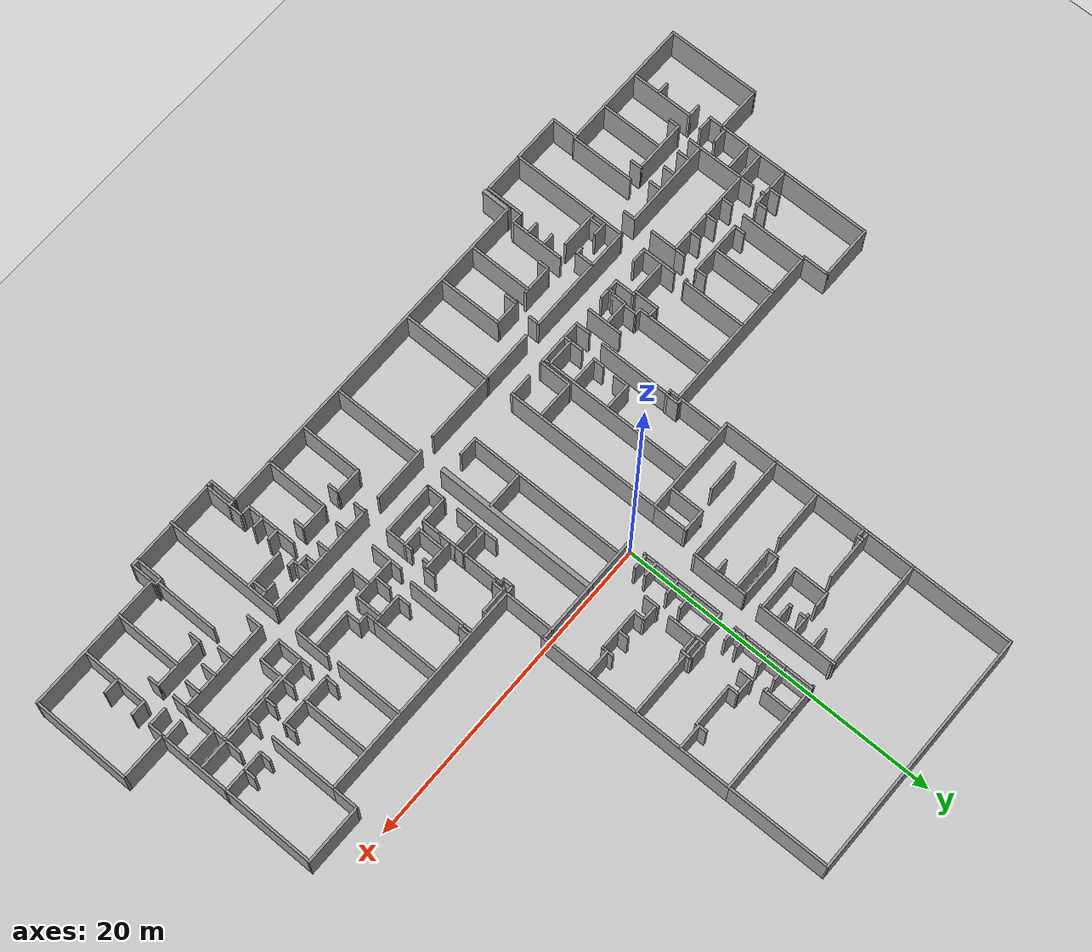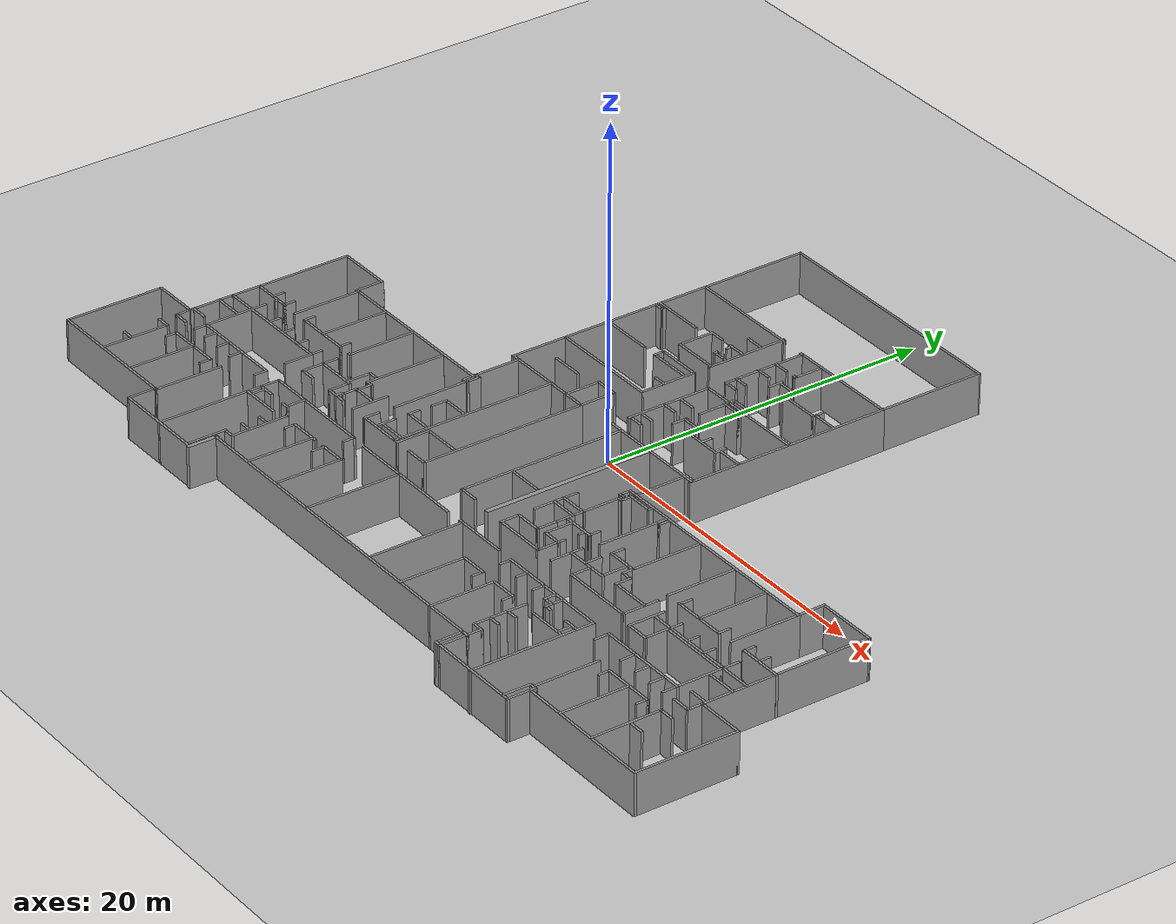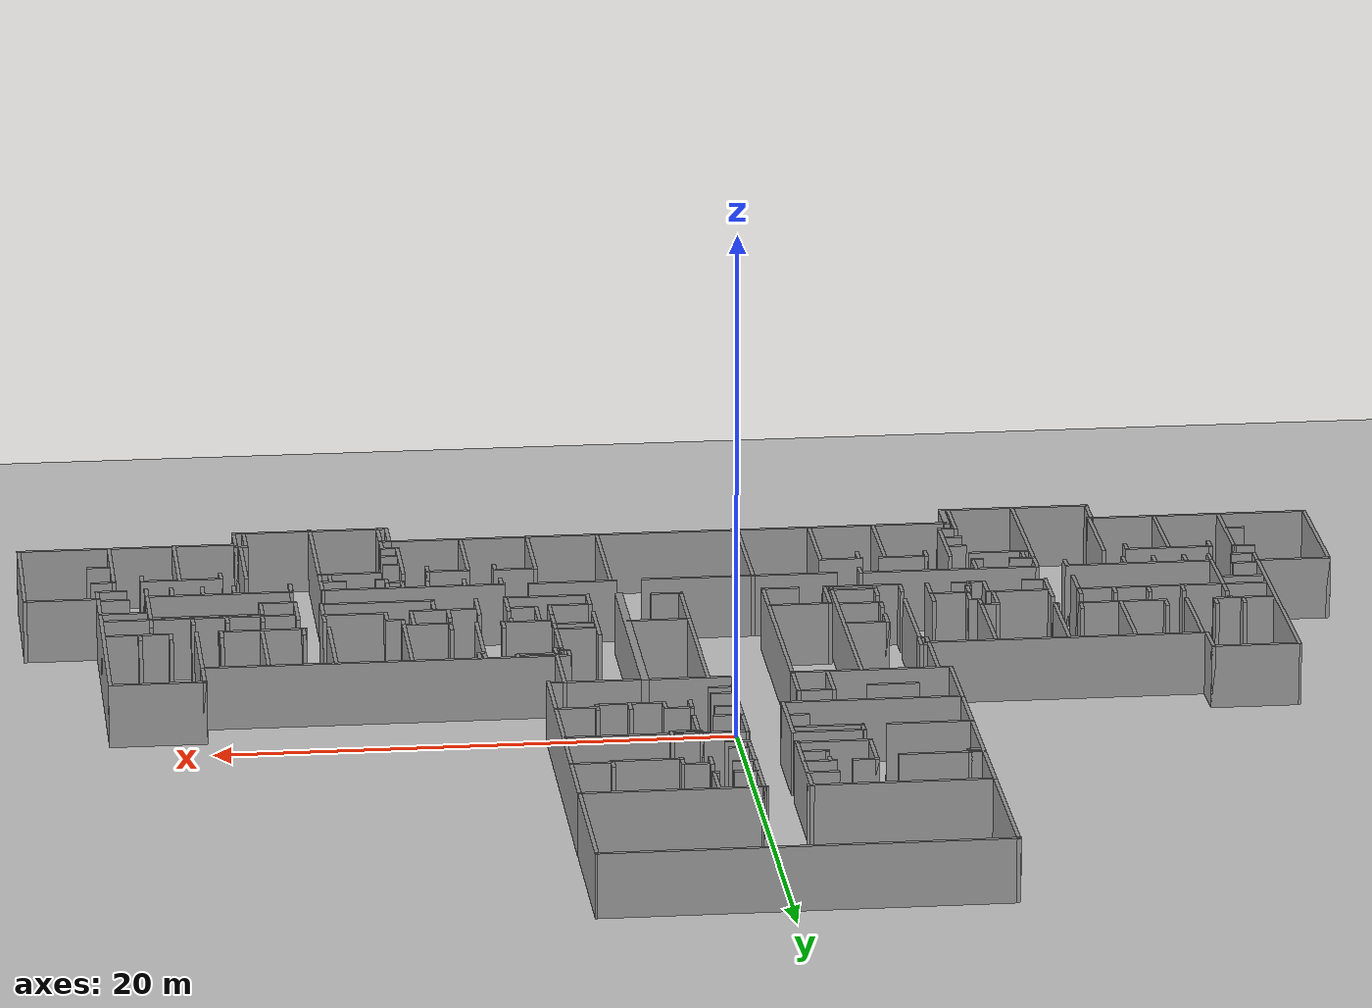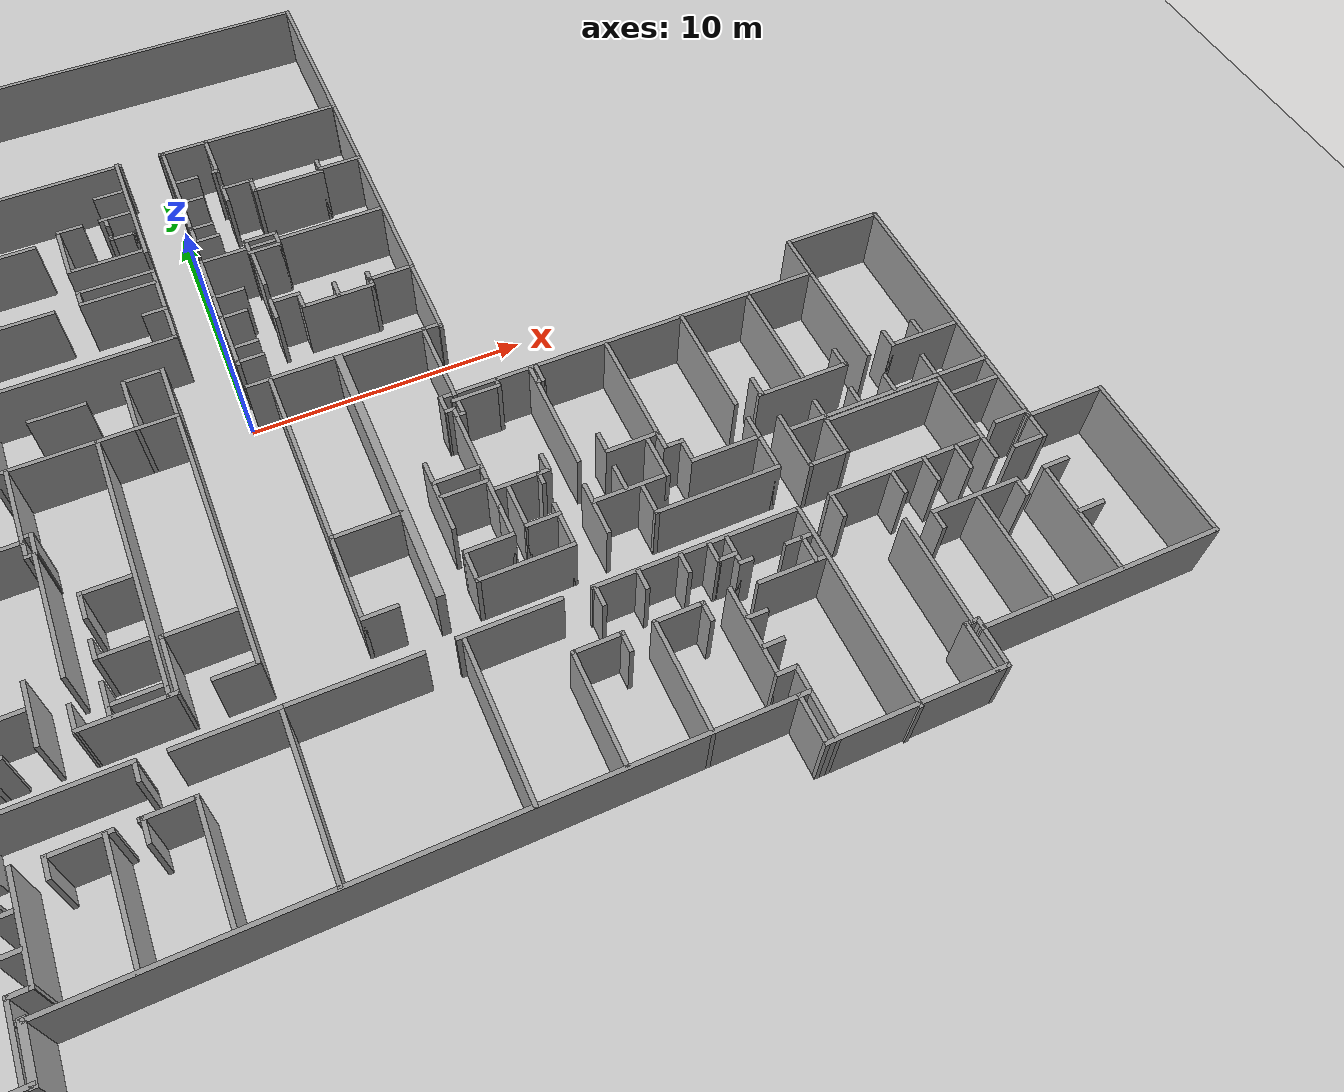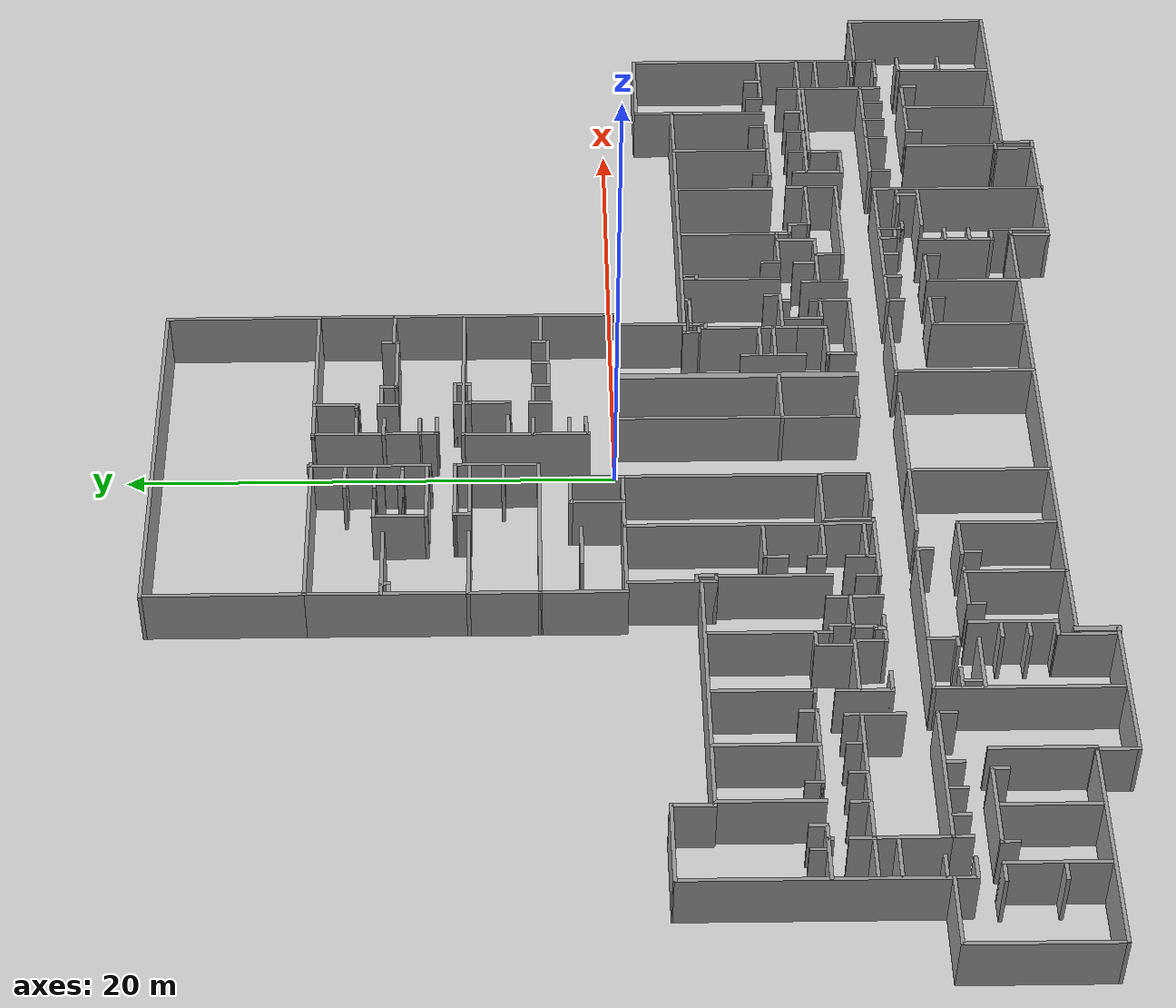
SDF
<sdf version="1.6">
 <world name="default">
  <light name="sun" type="directional">
   <pose>0 0 10 0 -0 0</pose>
   <diffuse>0.8 0.8 0.8 1</diffuse>
   <specular>0.2 0.2 0.2 1</specular>
   <attenuation>
    <range>1000</range>
    <constant>0.9</constant>
    <linear>0.01</linear>
    <quadratic>0.001</quadratic>
   </attenuation>
   <direction>-0.5 0.1 -0.9</direction>
  </light>
  <model name="ground_plane">
   <static>1</static>
   <link name="link">
    <collision name="collision">
     <geometry><plane><normal>0 0 1</normal><size>100 100</size></plane></geometry>
     <surface>
      <contact><collide_bitmask>65535</collide_bitmask></contact>
      <friction><ode><mu>100</mu><mu2>50</mu2></ode></friction>
     </surface>
    </collision>
    <visual name="visual">
     <cast_shadows>0</cast_shadows>
     <geometry><plane><normal>0 0 1</normal><size>100 100</size></plane></geometry>
     <material>
      <script><uri>file://media/materials/scripts/gazebo.material</uri><name>Gazebo/Grey</name></script>
     </material>
    </visual>
   </link>
  </model>
  <gravity>0 0 -9.8</gravity>
  <magnetic_field>6e-06 2.3e-05 -4.2e-05</magnetic_field>
  <atmosphere type="adiabatic"/>
  <physics name="default_physics" default="0" type="ode">
   <max_step_size>0.001</max_step_size>
   <real_time_factor>1</real_time_factor>
   <real_time_update_rate>1000</real_time_update_rate>
  </physics>
  <scene><ambient>0.4 0.4 0.4 1</ambient><background>0.7 0.7 0.7 1</background><shadows>1</shadows></scene>
  <audio><device>default</device></audio>
  <spherical_coordinates>
   <surface_model>EARTH_WGS84</surface_model>
   <latitude_deg>0</latitude_deg>
   <longitude_deg>0</longitude_deg>
   <elevation>0</elevation>
   <heading_deg>0</heading_deg>
  </spherical_coordinates>
  <model name="harnwell">
   <pose>0.907995 -0.1981 0 0 -0 0</pose>
   <link name="Wall_0">
    <collision name="Wall_0_Collision">
     <geometry><box><size>15.5704 0.15 2.5</size></box></geometry>
     <pose>0 0 1.25 0 -0 0</pose>
    </collision>
    <visual name="Wall_0_Visual">
     <pose>0 0 1.25 0 -0 0</pose>
     <geometry><box><size>15.5704 0.15 2.5</size></box></geometry>
     <material>
      <script><uri>file://media/materials/scripts/gazebo.material</uri><name>Gazebo/Grey</name></script>
      <ambient>1 1 1 1</ambient>
     </material>
     <meta><layer>0</layer></meta>
    </visual>
    <pose>-1.44871 18.8469 0 0 -0 0</pose>
   </link>
   <link name="Wall_1">
    <collision name="Wall_1_Collision">
     <geometry><box><size>6.51013 0.15 2.5</size></box></geometry>
     <pose>0 0 1.25 0 -0 0</pose>
    </collision>
    <visual name="Wall_1_Visual">
     <pose>0 0 1.25 0 -0 0</pose>
     <geometry><box><size>6.51013 0.15 2.5</size></box></geometry>
     <material>
      <script><uri>file://media/materials/scripts/gazebo.material</uri><name>Gazebo/Grey</name></script>
      <ambient>1 1 1 1</ambient>
     </material>
     <meta><layer>0</layer></meta>
    </visual>
    <pose>6.27155 15.6669 0 0 -0 -1.56763</pose>
   </link>
   <link name="Wall_10">
    <collision name="Wall_10_Collision">
     <geometry><box><size>4.47203 0.15 2.5</size></box></geometry>
     <pose>0 0 1.25 0 -0 0</pose>
    </collision>
    <visual name="Wall_10_Visual">
     <pose>0 0 1.25 0 -0 0</pose>
     <geometry><box><size>4.47203 0.15 2.5</size></box></geometry>
     <material>
      <script><uri>file://media/materials/scripts/gazebo.material</uri><name>Gazebo/Grey</name></script>
      <ambient>1 1 1 1</ambient>
     </material>
     <meta><layer>0</layer></meta>
    </visual>
    <pose>-0.551724 10.3258 0 0 -0 1.57386</pose>
   </link>
   <link name="Wall_101">
    <collision name="Wall_101_Collision">
     <geometry><box><size>0.75 0.15 2.5</size></box></geometry>
     <pose>0 0 1.25 0 -0 0</pose>
    </collision>
    <visual name="Wall_101_Visual">
     <pose>0 0 1.25 0 -0 0</pose>
     <geometry><box><size>0.75 0.15 2.5</size></box></geometry>
     <material>
      <script><uri>file://media/materials/scripts/gazebo.material</uri><name>Gazebo/Grey</name></script>
      <ambient>1 1 1 1</ambient>
     </material>
     <meta><layer>0</layer></meta>
    </visual>
    <pose>1.13146 6.45541 0 0 -0 -1.5708</pose>
   </link>
   <link name="Wall_102">
    <collision name="Wall_102_Collision">
     <geometry><box><size>1.25 0.15 2.5</size></box></geometry>
     <pose>0 0 1.25 0 -0 0</pose>
    </collision>
    <visual name="Wall_102_Visual">
     <pose>0 0 1.25 0 -0 0</pose>
     <geometry><box><size>1.25 0.15 2.5</size></box></geometry>
     <material>
      <script><uri>file://media/materials/scripts/gazebo.material</uri><name>Gazebo/Grey</name></script>
      <ambient>1 1 1 1</ambient>
     </material>
     <meta><layer>0</layer></meta>
    </visual>
    <pose>1.68146 6.15541 0 0 -0 0</pose>
   </link>
   <link name="Wall_103">
    <collision name="Wall_103_Collision">
     <geometry><box><size>0.75 0.15 2.5</size></box></geometry>
     <pose>0 0 1.25 0 -0 0</pose>
    </collision>
    <visual name="Wall_103_Visual">
     <pose>0 0 1.25 0 -0 0</pose>
     <geometry><box><size>0.75 0.15 2.5</size></box></geometry>
     <material>
      <script><uri>file://media/materials/scripts/gazebo.material</uri><name>Gazebo/Grey</name></script>
      <ambient>1 1 1 1</ambient>
     </material>
     <meta><layer>0</layer></meta>
    </visual>
    <pose>2.23146 6.45541 0 0 -0 1.5708</pose>
   </link>
   <link name="Wall_104">
    <collision name="Wall_104_Collision">
     <geometry><box><size>1.25 0.15 2.5</size></box></geometry>
     <pose>0 0 1.25 0 -0 0</pose>
    </collision>
    <visual name="Wall_104_Visual">
     <pose>0 0 1.25 0 -0 0</pose>
     <geometry><box><size>1.25 0.15 2.5</size></box></geometry>
     <material>
      <script><uri>file://media/materials/scripts/gazebo.material</uri><name>Gazebo/Grey</name></script>
      <ambient>1 1 1 1</ambient>
     </material>
     <meta><layer>0</layer></meta>
    </visual>
    <pose>1.68146 6.75541 0 0 -0 3.14159</pose>
   </link>
   <link name="Wall_106">
    <collision name="Wall_106_Collision">
     <geometry><box><size>1.78516 0.15 2.5</size></box></geometry>
     <pose>0 0 1.25 0 -0 0</pose>
    </collision>
    <visual name="Wall_106_Visual">
     <pose>0 0 1.25 0 -0 0</pose>
     <geometry><box><size>1.78516 0.15 2.5</size></box></geometry>
     <material>
      <script><uri>file://media/materials/scripts/gazebo.material</uri><name>Gazebo/Grey</name></script>
      <ambient>1 1 1 1</ambient>
     </material>
     <meta><layer>0</layer></meta>
    </visual>
    <pose>1.19616 5.32615 0 0 -0 1.5708</pose>
   </link>
   <link name="Wall_108">
    <collision name="Wall_108_Collision">
     <geometry><box><size>1.16755 0.15 2.5</size></box></geometry>
     <pose>0 0 1.25 0 -0 0</pose>
    </collision>
    <visual name="Wall_108_Visual">
     <pose>0 0 1.25 0 -0 0</pose>
     <geometry><box><size>1.16755 0.15 2.5</size></box></geometry>
     <material>
      <script><uri>file://media/materials/scripts/gazebo.material</uri><name>Gazebo/Grey</name></script>
      <ambient>1 1 1 1</ambient>
     </material>
     <meta><layer>0</layer></meta>
    </visual>
    <pose>-0.094995 4.57307 0 0 -0 0</pose>
   </link>
   <link name="Wall_11">
    <collision name="Wall_11_Collision">
     <geometry><box><size>0.25 0.15 2.5</size></box></geometry>
     <pose>0 0 1.25 0 -0 0</pose>
    </collision>
    <visual name="Wall_11_Visual">
     <pose>0 0 1.25 0 -0 0</pose>
     <geometry><box><size>0.25 0.15 2.5</size></box></geometry>
     <material>
      <script><uri>file://media/materials/scripts/gazebo.material</uri><name>Gazebo/Grey</name></script>
      <ambient>1 1 1 1</ambient>
     </material>
     <meta><layer>0</layer></meta>
    </visual>
    <pose>-0.60834 12.4868 0 0 -0 3.14159</pose>
   </link>
   <link name="Wall_110">
    <collision name="Wall_110_Collision">
     <geometry><box><size>1 0.15 2.5</size></box></geometry>
     <pose>0 0 1.25 0 -0 0</pose>
    </collision>
    <visual name="Wall_110_Visual">
     <pose>0 0 1.25 0 -0 0</pose>
     <geometry><box><size>1 0.15 2.5</size></box></geometry>
     <material>
      <script><uri>file://media/materials/scripts/gazebo.material</uri><name>Gazebo/Grey</name></script>
      <ambient>1 1 1 1</ambient>
     </material>
     <meta><layer>0</layer></meta>
    </visual>
    <pose>-0.181677 3.55575 0 0 -0 3.14159</pose>
   </link>
   <link name="Wall_112">
    <collision name="Wall_112_Collision">
     <geometry><box><size>1 0.15 2.5</size></box></geometry>
     <pose>0 0 1.25 0 -0 0</pose>
    </collision>
    <visual name="Wall_112_Visual">
     <pose>0 0 1.25 0 -0 0</pose>
     <geometry><box><size>1 0.15 2.5</size></box></geometry>
     <material>
      <script><uri>file://media/materials/scripts/gazebo.material</uri><name>Gazebo/Grey</name></script>
      <ambient>1 1 1 1</ambient>
     </material>
     <meta><layer>0</layer></meta>
    </visual>
    <pose>-0.199322 2.07356 0 0 -0 3.14159</pose>
   </link>
   <link name="Wall_114">
    <collision name="Wall_114_Collision">
     <geometry><box><size>0.96775 0.15 2.5</size></box></geometry>
     <pose>0 0 1.25 0 -0 0</pose>
    </collision>
    <visual name="Wall_114_Visual">
     <pose>0 0 1.25 0 -0 0</pose>
     <geometry><box><size>0.96775 0.15 2.5</size></box></geometry>
     <material>
      <script><uri>file://media/materials/scripts/gazebo.material</uri><name>Gazebo/Grey</name></script>
      <ambient>1 1 1 1</ambient>
     </material>
     <meta><layer>0</layer></meta>
    </visual>
    <pose>-0.165457 1.39716 0 0 -0 3.14159</pose>
   </link>
   <link name="Wall_116">
    <collision name="Wall_116_Collision">
     <geometry><box><size>0.972551 0.15 2.5</size></box></geometry>
     <pose>0 0 1.25 0 -0 0</pose>
    </collision>
    <visual name="Wall_116_Visual">
     <pose>0 0 1.25 0 -0 0</pose>
     <geometry><box><size>0.972551 0.15 2.5</size></box></geometry>
     <material>
      <script><uri>file://media/materials/scripts/gazebo.material</uri><name>Gazebo/Grey</name></script>
      <ambient>1 1 1 1</ambient>
     </material>
     <meta><layer>0</layer></meta>
    </visual>
    <pose>1.16104 3.2402 0 0 -0 -1.5708</pose>
   </link>
   <link name="Wall_119">
    <collision name="Wall_119_Collision">
     <geometry><box><size>1.12307 0.15 2.5</size></box></geometry>
     <pose>0 0 1.25 0 -0 0</pose>
    </collision>
    <visual name="Wall_119_Visual">
     <pose>0 0 1.25 0 -0 0</pose>
     <geometry><box><size>1.12307 0.15 2.5</size></box></geometry>
     <material>
      <script><uri>file://media/materials/scripts/gazebo.material</uri><name>Gazebo/Grey</name></script>
      <ambient>1 1 1 1</ambient>
     </material>
     <meta><layer>0</layer></meta>
    </visual>
    <pose>1.67379 3.55413 0 0 -0 -0.000113</pose>
   </link>
   <link name="Wall_12">
    <collision name="Wall_12_Collision">
     <geometry><box><size>0.25 0.15 2.5</size></box></geometry>
     <pose>0 0 1.25 0 -0 0</pose>
    </collision>
    <visual name="Wall_12_Visual">
     <pose>0 0 1.25 0 -0 0</pose>
     <geometry><box><size>0.25 0.15 2.5</size></box></geometry>
     <material>
      <script><uri>file://media/materials/scripts/gazebo.material</uri><name>Gazebo/Grey</name></script>
      <ambient>1 1 1 1</ambient>
     </material>
     <meta><layer>0</layer></meta>
    </visual>
    <pose>-0.60834 12.4868 0 0 -0 0</pose>
   </link>
   <link name="Wall_120">
    <collision name="Wall_120_Collision">
     <geometry><box><size>0.795673 0.15 2.5</size></box></geometry>
     <pose>0 0 1.25 0 -0 0</pose>
    </collision>
    <visual name="Wall_120_Visual">
     <pose>0 0 1.25 0 -0 0</pose>
     <geometry><box><size>0.795673 0.15 2.5</size></box></geometry>
     <material>
      <script><uri>file://media/materials/scripts/gazebo.material</uri><name>Gazebo/Grey</name></script>
      <ambient>1 1 1 1</ambient>
     </material>
     <meta><layer>0</layer></meta>
    </visual>
    <pose>2.16 3.23107 0 0 -0 -1.5708</pose>
   </link>
   <link name="Wall_122">
    <collision name="Wall_122_Collision">
     <geometry><box><size>2.70661 0.15 2.5</size></box></geometry>
     <pose>0 0 1.25 0 -0 0</pose>
    </collision>
    <visual name="Wall_122_Visual">
     <pose>0 0 1.25 0 -0 0</pose>
     <geometry><box><size>2.70661 0.15 2.5</size></box></geometry>
     <material>
      <script><uri>file://media/materials/scripts/gazebo.material</uri><name>Gazebo/Grey</name></script>
      <ambient>1 1 1 1</ambient>
     </material>
     <meta><layer>0</layer></meta>
    </visual>
    <pose>3.43851 2.90807 0 0 -0 0</pose>
   </link>
   <link name="Wall_125">
    <collision name="Wall_125_Collision">
     <geometry><box><size>0.75 0.15 2.5</size></box></geometry>
     <pose>0 0 1.25 0 -0 0</pose>
    </collision>
    <visual name="Wall_125_Visual">
     <pose>0 0 1.25 0 -0 0</pose>
     <geometry><box><size>0.75 0.15 2.5</size></box></geometry>
     <material>
      <script><uri>file://media/materials/scripts/gazebo.material</uri><name>Gazebo/Grey</name></script>
      <ambient>1 1 1 1</ambient>
     </material>
     <meta><layer>0</layer></meta>
    </visual>
    <pose>4.71701 3.20807 0 0 -0 1.5708</pose>
   </link>
   <link name="Wall_127">
    <collision name="Wall_127_Collision">
     <geometry><box><size>0.75 0.15 2.5</size></box></geometry>
     <pose>0 0 1.25 0 -0 0</pose>
    </collision>
    <visual name="Wall_127_Visual">
     <pose>0 0 1.25 0 -0 0</pose>
     <geometry><box><size>0.75 0.15 2.5</size></box></geometry>
     <material>
      <script><uri>file://media/materials/scripts/gazebo.material</uri><name>Gazebo/Grey</name></script>
      <ambient>1 1 1 1</ambient>
     </material>
     <meta><layer>0</layer></meta>
    </visual>
    <pose>3.47391 3.21295 0 0 -0 1.5708</pose>
   </link>
   <link name="Wall_130">
    <collision name="Wall_130_Collision">
     <geometry><box><size>1.69791 0.15 2.5</size></box></geometry>
     <pose>0 0 1.25 0 -0 0</pose>
    </collision>
    <visual name="Wall_130_Visual">
     <pose>0 0 1.25 0 -0 0</pose>
     <geometry><box><size>1.69791 0.15 2.5</size></box></geometry>
     <material>
      <script><uri>file://media/materials/scripts/gazebo.material</uri><name>Gazebo/Grey</name></script>
      <ambient>1 1 1 1</ambient>
     </material>
     <meta><layer>0</layer></meta>
    </visual>
    <pose>5.51702 3.20261 0 0 -0 -3.13874</pose>
   </link>
   <link name="Wall_132">
    <collision name="Wall_132_Collision">
     <geometry><box><size>3.5 0.15 2.5</size></box></geometry>
     <pose>0 0 1.25 0 -0 0</pose>
    </collision>
    <visual name="Wall_132_Visual">
     <pose>0 0 1.25 0 -0 0</pose>
     <geometry><box><size>3.5 0.15 2.5</size></box></geometry>
     <material>
      <script><uri>file://media/materials/scripts/gazebo.material</uri><name>Gazebo/Grey</name></script>
      <ambient>1 1 1 1</ambient>
     </material>
     <meta><layer>0</layer></meta>
    </visual>
    <pose>-9.16586 1.67152 0 0 -0 -1.5708</pose>
   </link>
   <link name="Wall_133">
    <collision name="Wall_133_Collision">
     <geometry><box><size>6.25 0.15 2.5</size></box></geometry>
     <pose>0 0 1.25 0 -0 0</pose>
    </collision>
    <visual name="Wall_133_Visual">
     <pose>0 0 1.25 0 -0 0</pose>
     <geometry><box><size>6.25 0.15 2.5</size></box></geometry>
     <material>
      <script><uri>file://media/materials/scripts/gazebo.material</uri><name>Gazebo/Grey</name></script>
      <ambient>1 1 1 1</ambient>
     </material>
     <meta><layer>0</layer></meta>
    </visual>
    <pose>-6.11586 -0.003478 0 0 -0 0</pose>
   </link>
   <link name="Wall_135">
    <collision name="Wall_135_Collision">
     <geometry><box><size>2.25 0.15 2.5</size></box></geometry>
     <pose>0 0 1.25 0 -0 0</pose>
    </collision>
    <visual name="Wall_135_Visual">
     <pose>0 0 1.25 0 -0 0</pose>
     <geometry><box><size>2.25 0.15 2.5</size></box></geometry>
     <material>
      <script><uri>file://media/materials/scripts/gazebo.material</uri><name>Gazebo/Grey</name></script>
      <ambient>1 1 1 1</ambient>
     </material>
     <meta><layer>0</layer></meta>
    </visual>
    <pose>-3.06586 1.04652 0 0 -0 1.5708</pose>
   </link>
   <link name="Wall_136">
    <collision name="Wall_136_Collision">
     <geometry><box><size>1.5 0.15 2.5</size></box></geometry>
     <pose>0 0 1.25 0 -0 0</pose>
    </collision>
    <visual name="Wall_136_Visual">
     <pose>0 0 1.25 0 -0 0</pose>
     <geometry><box><size>1.5 0.15 2.5</size></box></geometry>
     <material>
      <script><uri>file://media/materials/scripts/gazebo.material</uri><name>Gazebo/Grey</name></script>
      <ambient>1 1 1 1</ambient>
     </material>
     <meta><layer>0</layer></meta>
    </visual>
    <pose>-3.74086 2.09652 0 0 -0 3.14159</pose>
   </link>
   <link name="Wall_137">
    <collision name="Wall_137_Collision">
     <geometry><box><size>2.25 0.15 2.5</size></box></geometry>
     <pose>0 0 1.25 0 -0 0</pose>
    </collision>
    <visual name="Wall_137_Visual">
     <pose>0 0 1.25 0 -0 0</pose>
     <geometry><box><size>2.25 0.15 2.5</size></box></geometry>
     <material>
      <script><uri>file://media/materials/scripts/gazebo.material</uri><name>Gazebo/Grey</name></script>
      <ambient>1 1 1 1</ambient>
     </material>
     <meta><layer>0</layer></meta>
    </visual>
    <pose>-4.41586 1.04652 0 0 -0 -1.5708</pose>
   </link>
   <link name="Wall_139">
    <collision name="Wall_139_Collision">
     <geometry><box><size>2 0.15 2.5</size></box></geometry>
     <pose>0 0 1.25 0 -0 0</pose>
    </collision>
    <visual name="Wall_139_Visual">
     <pose>0 0 1.25 0 -0 0</pose>
     <geometry><box><size>2 0.15 2.5</size></box></geometry>
     <material>
      <script><uri>file://media/materials/scripts/gazebo.material</uri><name>Gazebo/Grey</name></script>
      <ambient>1 1 1 1</ambient>
     </material>
     <meta><layer>0</layer></meta>
    </visual>
    <pose>-6.7235 1.70166 0 0 -0 0</pose>
   </link>
   <link name="Wall_143">
    <collision name="Wall_143_Collision">
     <geometry><box><size>14.25 0.15 2.5</size></box></geometry>
     <pose>0 0 1.25 0 -0 0</pose>
    </collision>
    <visual name="Wall_143_Visual">
     <pose>0 0 1.25 0 -0 0</pose>
     <geometry><box><size>14.25 0.15 2.5</size></box></geometry>
     <material>
      <script><uri>file://media/materials/scripts/gazebo.material</uri><name>Gazebo/Grey</name></script>
      <ambient>1 1 1 1</ambient>
     </material>
     <meta><layer>0</layer></meta>
    </visual>
    <pose>12.25 -2.82962 0 0 -0 0</pose>
   </link>
   <link name="Wall_144">
    <collision name="Wall_144_Collision">
     <geometry><box><size>1.75 0.15 2.5</size></box></geometry>
     <pose>0 0 1.25 0 -0 0</pose>
    </collision>
    <visual name="Wall_144_Visual">
     <pose>0 0 1.25 0 -0 0</pose>
     <geometry><box><size>1.75 0.15 2.5</size></box></geometry>
     <material>
      <script><uri>file://media/materials/scripts/gazebo.material</uri><name>Gazebo/Grey</name></script>
      <ambient>1 1 1 1</ambient>
     </material>
     <meta><layer>0</layer></meta>
    </visual>
    <pose>19.3 -2.02962 0 0 -0 1.5708</pose>
   </link>
   <link name="Wall_146">
    <collision name="Wall_146_Collision">
     <geometry><box><size>0.75 0.15 2.5</size></box></geometry>
     <pose>0 0 1.25 0 -0 0</pose>
    </collision>
    <visual name="Wall_146_Visual">
     <pose>0 0 1.25 0 -0 0</pose>
     <geometry><box><size>0.75 0.15 2.5</size></box></geometry>
     <material>
      <script><uri>file://media/materials/scripts/gazebo.material</uri><name>Gazebo/Grey</name></script>
      <ambient>1 1 1 1</ambient>
     </material>
     <meta><layer>0</layer></meta>
    </visual>
    <pose>5.19998 -3.12962 0 0 -0 -1.5708</pose>
   </link>
   <link name="Wall_147">
    <collision name="Wall_147_Collision">
     <geometry><box><size>0.394027 0.15 2.5</size></box></geometry>
     <pose>0 0 1.25 0 -0 0</pose>
    </collision>
    <visual name="Wall_147_Visual">
     <pose>0 0 1.25 0 -0 0</pose>
     <geometry><box><size>0.394027 0.15 2.5</size></box></geometry>
     <material>
      <script><uri>file://media/materials/scripts/gazebo.material</uri><name>Gazebo/Grey</name></script>
      <ambient>1 1 1 1</ambient>
     </material>
     <meta><layer>0</layer></meta>
    </visual>
    <pose>5.32199 -3.42977 0 0 -0 -0.00125</pose>
   </link>
   <link name="Wall_150">
    <collision name="Wall_150_Collision">
     <geometry><box><size>10.25 0.3 2.5</size></box></geometry>
     <pose>0 0 1.25 0 -0 0</pose>
    </collision>
    <visual name="Wall_150_Visual">
     <pose>0 0 1.25 0 -0 0</pose>
     <geometry><box><size>10.25 0.3 2.5</size></box></geometry>
     <material>
      <script><uri>file://media/materials/scripts/gazebo.material</uri><name>Gazebo/Grey</name></script>
      <ambient>1 1 1 1</ambient>
     </material>
     <meta><layer>0</layer></meta>
    </visual>
    <pose>2.60701 -4.80593 0 0 -0 1.5708</pose>
   </link>
   <link name="Wall_153">
    <collision name="Wall_153_Collision">
     <geometry><box><size>2.75 0.15 2.5</size></box></geometry>
     <pose>0 0 1.25 0 -0 0</pose>
    </collision>
    <visual name="Wall_153_Visual">
     <pose>0 0 1.25 0 -0 0</pose>
     <geometry><box><size>2.75 0.15 2.5</size></box></geometry>
     <material>
      <script><uri>file://media/materials/scripts/gazebo.material</uri><name>Gazebo/Grey</name></script>
      <ambient>1 1 1 1</ambient>
     </material>
     <meta><layer>0</layer></meta>
    </visual>
    <pose>3.8126 -6.4747 0 0 -0 -1.5708</pose>
   </link>
   <link name="Wall_155">
    <collision name="Wall_155_Collision">
     <geometry><box><size>1.75 0.15 2.5</size></box></geometry>
     <pose>0 0 1.25 0 -0 0</pose>
    </collision>
    <visual name="Wall_155_Visual">
     <pose>0 0 1.25 0 -0 0</pose>
     <geometry><box><size>1.75 0.15 2.5</size></box></geometry>
     <material>
      <script><uri>file://media/materials/scripts/gazebo.material</uri><name>Gazebo/Grey</name></script>
      <ambient>1 1 1 1</ambient>
     </material>
     <meta><layer>0</layer></meta>
    </visual>
    <pose>4.64354 -6.5592 0 0 -0 0</pose>
   </link>
   <link name="Wall_156">
    <collision name="Wall_156_Collision">
     <geometry><box><size>0.75 0.15 2.5</size></box></geometry>
     <pose>0 0 1.25 0 -0 0</pose>
    </collision>
    <visual name="Wall_156_Visual">
     <pose>0 0 1.25 0 -0 0</pose>
     <geometry><box><size>0.75 0.15 2.5</size></box></geometry>
     <material>
      <script><uri>file://media/materials/scripts/gazebo.material</uri><name>Gazebo/Grey</name></script>
      <ambient>1 1 1 1</ambient>
     </material>
     <meta><layer>0</layer></meta>
    </visual>
    <pose>5.44377 -6.25906 0 0 -0 1.57002</pose>
   </link>
   <link name="Wall_157">
    <collision name="Wall_157_Collision">
     <geometry><box><size>1.75 0.15 2.5</size></box></geometry>
     <pose>0 0 1.25 0 -0 0</pose>
    </collision>
    <visual name="Wall_157_Visual">
     <pose>0 0 1.25 0 -0 0</pose>
     <geometry><box><size>1.75 0.15 2.5</size></box></geometry>
     <material>
      <script><uri>file://media/materials/scripts/gazebo.material</uri><name>Gazebo/Grey</name></script>
      <ambient>1 1 1 1</ambient>
     </material>
     <meta><layer>0</layer></meta>
    </visual>
    <pose>4.64377 -5.95906 0 0 -0 -3.14142</pose>
   </link>
   <link name="Wall_159">
    <collision name="Wall_159_Collision">
     <geometry><box><size>2.67942 0.15 2.5</size></box></geometry>
     <pose>0 0 1.25 0 -0 0</pose>
    </collision>
    <visual name="Wall_159_Visual">
     <pose>0 0 1.25 0 -0 0</pose>
     <geometry><box><size>2.67942 0.15 2.5</size></box></geometry>
     <material>
      <script><uri>file://media/materials/scripts/gazebo.material</uri><name>Gazebo/Grey</name></script>
      <ambient>1 1 1 1</ambient>
     </material>
     <meta><layer>0</layer></meta>
    </visual>
    <pose>5.444 -4.69443 0 0 -0 1.5708</pose>
   </link>
   <link name="Wall_161">
    <collision name="Wall_161_Collision">
     <geometry><box><size>1.25 0.15 2.5</size></box></geometry>
     <pose>0 0 1.25 0 -0 0</pose>
    </collision>
    <visual name="Wall_161_Visual">
     <pose>0 0 1.25 0 -0 0</pose>
     <geometry><box><size>1.25 0.15 2.5</size></box></geometry>
     <material>
      <script><uri>file://media/materials/scripts/gazebo.material</uri><name>Gazebo/Grey</name></script>
      <ambient>1 1 1 1</ambient>
     </material>
     <meta><layer>0</layer></meta>
    </visual>
    <pose>5.44354 -7.1092 0 0 -0 -1.5708</pose>
   </link>
   <link name="Wall_162">
    <collision name="Wall_162_Collision">
     <geometry><box><size>1.25 0.15 2.5</size></box></geometry>
     <pose>0 0 1.25 0 -0 0</pose>
    </collision>
    <visual name="Wall_162_Visual">
     <pose>0 0 1.25 0 -0 0</pose>
     <geometry><box><size>1.25 0.15 2.5</size></box></geometry>
     <material>
      <script><uri>file://media/materials/scripts/gazebo.material</uri><name>Gazebo/Grey</name></script>
      <ambient>1 1 1 1</ambient>
     </material>
     <meta><layer>0</layer></meta>
    </visual>
    <pose>5.44354 -8.2092 0 0 -0 -1.5708</pose>
   </link>
   <link name="Wall_163">
    <collision name="Wall_163_Collision">
     <geometry><box><size>1.75 0.15 2.5</size></box></geometry>
     <pose>0 0 1.25 0 -0 0</pose>
    </collision>
    <visual name="Wall_163_Visual">
     <pose>0 0 1.25 0 -0 0</pose>
     <geometry><box><size>1.75 0.15 2.5</size></box></geometry>
     <material>
      <script><uri>file://media/materials/scripts/gazebo.material</uri><name>Gazebo/Grey</name></script>
      <ambient>1 1 1 1</ambient>
     </material>
     <meta><layer>0</layer></meta>
    </visual>
    <pose>4.64354 -8.7592 0 0 -0 3.14159</pose>
   </link>
   <link name="Wall_165">
    <collision name="Wall_165_Collision">
     <geometry><box><size>1.25 0.15 2.5</size></box></geometry>
     <pose>0 0 1.25 0 -0 0</pose>
    </collision>
    <visual name="Wall_165_Visual">
     <pose>0 0 1.25 0 -0 0</pose>
     <geometry><box><size>1.25 0.15 2.5</size></box></geometry>
     <material>
      <script><uri>file://media/materials/scripts/gazebo.material</uri><name>Gazebo/Grey</name></script>
      <ambient>1 1 1 1</ambient>
     </material>
     <meta><layer>0</layer></meta>
    </visual>
    <pose>3.84377 -9.30906 0 0 -0 -1.57037</pose>
   </link>
   <link name="Wall_166">
    <collision name="Wall_166_Collision">
     <geometry><box><size>3.3708 0.15 2.5</size></box></geometry>
     <pose>0 0 1.25 0 -0 0</pose>
    </collision>
    <visual name="Wall_166_Visual">
     <pose>0 0 1.25 0 -0 0</pose>
     <geometry><box><size>3.3708 0.15 2.5</size></box></geometry>
     <material>
      <script><uri>file://media/materials/scripts/gazebo.material</uri><name>Gazebo/Grey</name></script>
      <ambient>1 1 1 1</ambient>
     </material>
     <meta><layer>0</layer></meta>
    </visual>
    <pose>5.45451 -9.85893 0 0 -0 0</pose>
   </link>
   <link name="Wall_169">
    <collision name="Wall_169_Collision">
     <geometry><box><size>1.75 0.15 2.5</size></box></geometry>
     <pose>0 0 1.25 0 -0 0</pose>
    </collision>
    <visual name="Wall_169_Visual">
     <pose>0 0 1.25 0 -0 0</pose>
     <geometry><box><size>1.75 0.15 2.5</size></box></geometry>
     <material>
      <script><uri>file://media/materials/scripts/gazebo.material</uri><name>Gazebo/Grey</name></script>
      <ambient>1 1 1 1</ambient>
     </material>
     <meta><layer>0</layer></meta>
    </visual>
    <pose>7.06501 -9.05893 0 0 -0 1.5708</pose>
   </link>
   <link name="Wall_171">
    <collision name="Wall_171_Collision">
     <geometry><box><size>0.75 0.15 2.5</size></box></geometry>
     <pose>0 0 1.25 0 -0 0</pose>
    </collision>
    <visual name="Wall_171_Visual">
     <pose>0 0 1.25 0 -0 0</pose>
     <geometry><box><size>0.75 0.15 2.5</size></box></geometry>
     <material>
      <script><uri>file://media/materials/scripts/gazebo.material</uri><name>Gazebo/Grey</name></script>
      <ambient>1 1 1 1</ambient>
     </material>
     <meta><layer>0</layer></meta>
    </visual>
    <pose>7.41354 -6.65701 0 0 -0 -1.5708</pose>
   </link>
   <link name="Wall_172">
    <collision name="Wall_172_Collision">
     <geometry><box><size>2 0.15 2.5</size></box></geometry>
     <pose>0 0 1.25 0 -0 0</pose>
    </collision>
    <visual name="Wall_172_Visual">
     <pose>0 0 1.25 0 -0 0</pose>
     <geometry><box><size>2 0.15 2.5</size></box></geometry>
     <material>
      <script><uri>file://media/materials/scripts/gazebo.material</uri><name>Gazebo/Grey</name></script>
      <ambient>1 1 1 1</ambient>
     </material>
     <meta><layer>0</layer></meta>
    </visual>
    <pose>6.48853 -6.95701 0 0 -0 3.14159</pose>
   </link>
   <link name="Wall_174">
    <collision name="Wall_174_Collision">
     <geometry><box><size>0.5 0.15 2.5</size></box></geometry>
     <pose>0 0 1.25 0 -0 0</pose>
    </collision>
    <visual name="Wall_174_Visual">
     <pose>0 0 1.25 0 -0 0</pose>
     <geometry><box><size>0.5 0.15 2.5</size></box></geometry>
     <material>
      <script><uri>file://media/materials/scripts/gazebo.material</uri><name>Gazebo/Grey</name></script>
      <ambient>1 1 1 1</ambient>
     </material>
     <meta><layer>0</layer></meta>
    </visual>
    <pose>7.06651 -7.15547 0 0 -0 -1.5708</pose>
   </link>
   <link name="Wall_176">
    <collision name="Wall_176_Collision">
     <geometry><box><size>1.25 0.15 2.5</size></box></geometry>
     <pose>0 0 1.25 0 -0 0</pose>
    </collision>
    <visual name="Wall_176_Visual">
     <pose>0 0 1.25 0 -0 0</pose>
     <geometry><box><size>1.25 0.15 2.5</size></box></geometry>
     <material>
      <script><uri>file://media/materials/scripts/gazebo.material</uri><name>Gazebo/Grey</name></script>
      <ambient>1 1 1 1</ambient>
     </material>
     <meta><layer>0</layer></meta>
    </visual>
    <pose>6.52251 -8.63324 0 0 -0 0</pose>
   </link>
   <link name="Wall_178">
    <collision name="Wall_178_Collision">
     <geometry><box><size>1.75 0.15 2.5</size></box></geometry>
     <pose>0 0 1.25 0 -0 0</pose>
    </collision>
    <visual name="Wall_178_Visual">
     <pose>0 0 1.25 0 -0 0</pose>
     <geometry><box><size>1.75 0.15 2.5</size></box></geometry>
     <material>
      <script><uri>file://media/materials/scripts/gazebo.material</uri><name>Gazebo/Grey</name></script>
      <ambient>1 1 1 1</ambient>
     </material>
     <meta><layer>0</layer></meta>
    </visual>
    <pose>5.97251 -7.83324 0 0 -0 1.5708</pose>
   </link>
   <link name="Wall_183">
    <collision name="Wall_183_Collision">
     <geometry><box><size>0.371226 0.15 2.5</size></box></geometry>
     <pose>0 0 1.25 0 -0 0</pose>
    </collision>
    <visual name="Wall_183_Visual">
     <pose>0 0 1.25 0 -0 0</pose>
     <geometry><box><size>0.371226 0.15 2.5</size></box></geometry>
     <material>
      <script><uri>file://media/materials/scripts/gazebo.material</uri><name>Gazebo/Grey</name></script>
      <ambient>1 1 1 1</ambient>
     </material>
     <meta><layer>0</layer></meta>
    </visual>
    <pose>7.184 -2.99743 0 0 -0 -1.5708</pose>
   </link>
   <link name="Wall_187">
    <collision name="Wall_187_Collision">
     <geometry><box><size>1.769 0.15 2.5</size></box></geometry>
     <pose>0 0 1.25 0 -0 0</pose>
    </collision>
    <visual name="Wall_187_Visual">
     <pose>0 0 1.25 0 -0 0</pose>
     <geometry><box><size>1.769 0.15 2.5</size></box></geometry>
     <material>
      <script><uri>file://media/materials/scripts/gazebo.material</uri><name>Gazebo/Grey</name></script>
      <ambient>1 1 1 1</ambient>
     </material>
     <meta><layer>0</layer></meta>
    </visual>
    <pose>6.36905 -3.10793 0 0 -0 0</pose>
   </link>
   <link name="Wall_190">
    <collision name="Wall_190_Collision">
     <geometry><box><size>0.70688 0.15 2.5</size></box></geometry>
     <pose>0 0 1.25 0 -0 0</pose>
    </collision>
    <visual name="Wall_190_Visual">
     <pose>0 0 1.25 0 -0 0</pose>
     <geometry><box><size>0.70688 0.15 2.5</size></box></geometry>
     <material>
      <script><uri>file://media/materials/scripts/gazebo.material</uri><name>Gazebo/Grey</name></script>
      <ambient>1 1 1 1</ambient>
     </material>
     <meta><layer>0</layer></meta>
    </visual>
    <pose>5.68636 -3.40397 0 0 -0 1.5708</pose>
   </link>
   <link name="Wall_192">
    <collision name="Wall_192_Collision">
     <geometry><box><size>0.355969 0.15 2.5</size></box></geometry>
     <pose>0 0 1.25 0 -0 0</pose>
    </collision>
    <visual name="Wall_192_Visual">
     <pose>0 0 1.25 0 -0 0</pose>
     <geometry><box><size>0.355969 0.15 2.5</size></box></geometry>
     <material>
      <script><uri>file://media/materials/scripts/gazebo.material</uri><name>Gazebo/Grey</name></script>
      <ambient>1 1 1 1</ambient>
     </material>
     <meta><layer>0</layer></meta>
    </visual>
    <pose>5.58101 -3.72593 0 0 -0 0</pose>
   </link>
   <link name="Wall_194">
    <collision name="Wall_194_Collision">
     <geometry><box><size>4.25 0.15 2.5</size></box></geometry>
     <pose>0 0 1.25 0 -0 0</pose>
    </collision>
    <visual name="Wall_194_Visual">
     <pose>0 0 1.25 0 -0 0</pose>
     <geometry><box><size>4.25 0.15 2.5</size></box></geometry>
     <material>
      <script><uri>file://media/materials/scripts/gazebo.material</uri><name>Gazebo/Grey</name></script>
      <ambient>1 1 1 1</ambient>
     </material>
     <meta><layer>0</layer></meta>
    </visual>
    <pose>8.43726 -4.95199 0 0 -0 -1.5708</pose>
   </link>
   <link name="Wall_197">
    <collision name="Wall_197_Collision">
     <geometry><box><size>0.313758 0.15 2.5</size></box></geometry>
     <pose>0 0 1.25 0 -0 0</pose>
    </collision>
    <visual name="Wall_197_Visual">
     <pose>0 0 1.25 0 -0 0</pose>
     <geometry><box><size>0.313758 0.15 2.5</size></box></geometry>
     <material>
      <script><uri>file://media/materials/scripts/gazebo.material</uri><name>Gazebo/Grey</name></script>
      <ambient>1 1 1 1</ambient>
     </material>
     <meta><layer>0</layer></meta>
    </visual>
    <pose>8.5618 -3.47644 0 0 -0 0</pose>
   </link>
   <link name="Wall_198">
    <collision name="Wall_198_Collision">
     <geometry><box><size>0.75 0.15 2.5</size></box></geometry>
     <pose>0 0 1.25 0 -0 0</pose>
    </collision>
    <visual name="Wall_198_Visual">
     <pose>0 0 1.25 0 -0 0</pose>
     <geometry><box><size>0.75 0.15 2.5</size></box></geometry>
     <material>
      <script><uri>file://media/materials/scripts/gazebo.material</uri><name>Gazebo/Grey</name></script>
      <ambient>1 1 1 1</ambient>
     </material>
     <meta><layer>0</layer></meta>
    </visual>
    <pose>8.64368 -3.17644 0 0 -0 1.5708</pose>
   </link>
   <link name="Wall_2">
    <collision name="Wall_2_Collision">
     <geometry><box><size>7 0.15 2.5</size></box></geometry>
     <pose>0 0 1.25 0 -0 0</pose>
    </collision>
    <visual name="Wall_2_Visual">
     <pose>0 0 1.25 0 -0 0</pose>
     <geometry><box><size>7 0.15 2.5</size></box></geometry>
     <material>
      <script><uri>file://media/materials/scripts/gazebo.material</uri><name>Gazebo/Grey</name></script>
      <ambient>1 1 1 1</ambient>
     </material>
     <meta><layer>0</layer></meta>
    </visual>
    <pose>2.86666 12.4868 0 0 -0 3.14159</pose>
   </link>
   <link name="Wall_200">
    <collision name="Wall_200_Collision">
     <geometry><box><size>0.851822 0.15 2.5</size></box></geometry>
     <pose>0 0 1.25 0 -0 0</pose>
    </collision>
    <visual name="Wall_200_Visual">
     <pose>0 0 1.25 0 -0 0</pose>
     <geometry><box><size>0.851822 0.15 2.5</size></box></geometry>
     <material>
      <script><uri>file://media/materials/scripts/gazebo.material</uri><name>Gazebo/Grey</name></script>
      <ambient>1 1 1 1</ambient>
     </material>
     <meta><layer>0</layer></meta>
    </visual>
    <pose>9.449 -6.69593 0 0 -0 -1.5708</pose>
   </link>
   <link name="Wall_202">
    <collision name="Wall_202_Collision">
     <geometry><box><size>1.95254 0.15 2.5</size></box></geometry>
     <pose>0 0 1.25 0 -0 0</pose>
    </collision>
    <visual name="Wall_202_Visual">
     <pose>0 0 1.25 0 -0 0</pose>
     <geometry><box><size>1.95254 0.15 2.5</size></box></geometry>
     <material>
      <script><uri>file://media/materials/scripts/gazebo.material</uri><name>Gazebo/Grey</name></script>
      <ambient>1 1 1 1</ambient>
     </material>
     <meta><layer>0</layer></meta>
    </visual>
    <pose>10.3505 -7.04693 0 0 -0 0</pose>
   </link>
   <link name="Wall_204">
    <collision name="Wall_204_Collision">
     <geometry><box><size>4.25 0.15 2.5</size></box></geometry>
     <pose>0 0 1.25 0 -0 0</pose>
    </collision>
    <visual name="Wall_204_Visual">
     <pose>0 0 1.25 0 -0 0</pose>
     <geometry><box><size>4.25 0.15 2.5</size></box></geometry>
     <material>
      <script><uri>file://media/materials/scripts/gazebo.material</uri><name>Gazebo/Grey</name></script>
      <ambient>1 1 1 1</ambient>
     </material>
     <meta><layer>0</layer></meta>
    </visual>
    <pose>11.252 -4.99693 0 0 -0 1.5708</pose>
   </link>
   <link name="Wall_206">
    <collision name="Wall_206_Collision">
     <geometry><box><size>4.25 0.15 2.5</size></box></geometry>
     <pose>0 0 1.25 0 -0 0</pose>
    </collision>
    <visual name="Wall_206_Visual">
     <pose>0 0 1.25 0 -0 0</pose>
     <geometry><box><size>4.25 0.15 2.5</size></box></geometry>
     <material>
      <script><uri>file://media/materials/scripts/gazebo.material</uri><name>Gazebo/Grey</name></script>
      <ambient>1 1 1 1</ambient>
     </material>
     <meta><layer>0</layer></meta>
    </visual>
    <pose>14.1664 -4.93665 0 0 -0 1.5708</pose>
   </link>
   <link name="Wall_208">
    <collision name="Wall_208_Collision">
     <geometry><box><size>3.421 0.15 2.5</size></box></geometry>
     <pose>0 0 1.25 0 -0 0</pose>
    </collision>
    <visual name="Wall_208_Visual">
     <pose>0 0 1.25 0 -0 0</pose>
     <geometry><box><size>3.421 0.15 2.5</size></box></geometry>
     <material>
      <script><uri>file://media/materials/scripts/gazebo.material</uri><name>Gazebo/Grey</name></script>
      <ambient>1 1 1 1</ambient>
     </material>
     <meta><layer>0</layer></meta>
    </visual>
    <pose>16.7336 -6.99103 0 0 -0 0</pose>
   </link>
   <link name="Wall_21">
    <collision name="Wall_21_Collision">
     <geometry><box><size>5 0.15 2.5</size></box></geometry>
     <pose>0 0 1.25 0 -0 0</pose>
    </collision>
    <visual name="Wall_21_Visual">
     <pose>0 0 1.25 0 -0 0</pose>
     <geometry><box><size>5 0.15 2.5</size></box></geometry>
     <material>
      <script><uri>file://media/materials/scripts/gazebo.material</uri><name>Gazebo/Grey</name></script>
      <ambient>1 1 1 1</ambient>
     </material>
     <meta><layer>0</layer></meta>
    </visual>
    <pose>-2.32775 10.1553 0 0 -0 1.5708</pose>
   </link>
   <link name="Wall_210">
    <collision name="Wall_210_Collision">
     <geometry><box><size>4.25 0.15 2.5</size></box></geometry>
     <pose>0 0 1.25 0 -0 0</pose>
    </collision>
    <visual name="Wall_210_Visual">
     <pose>0 0 1.25 0 -0 0</pose>
     <geometry><box><size>4.25 0.15 2.5</size></box></geometry>
     <material>
      <script><uri>file://media/materials/scripts/gazebo.material</uri><name>Gazebo/Grey</name></script>
      <ambient>1 1 1 1</ambient>
     </material>
     <meta><layer>0</layer></meta>
    </visual>
    <pose>16.7589 -4.92211 0 0 -0 1.5708</pose>
   </link>
   <link name="Wall_212">
    <collision name="Wall_212_Collision">
     <geometry><box><size>0.813372 0.15 2.5</size></box></geometry>
     <pose>0 0 1.25 0 -0 0</pose>
    </collision>
    <visual name="Wall_212_Visual">
     <pose>0 0 1.25 0 -0 0</pose>
     <geometry><box><size>0.813372 0.15 2.5</size></box></geometry>
     <material>
      <script><uri>file://media/materials/scripts/gazebo.material</uri><name>Gazebo/Grey</name></script>
      <ambient>1 1 1 1</ambient>
     </material>
     <meta><layer>0</layer></meta>
    </visual>
    <pose>15.153 -6.65243 0 0 -0 -1.5708</pose>
   </link>
   <link name="Wall_214">
    <collision name="Wall_214_Collision">
     <geometry><box><size>0.796146 0.15 2.5</size></box></geometry>
     <pose>0 0 1.25 0 -0 0</pose>
    </collision>
    <visual name="Wall_214_Visual">
     <pose>0 0 1.25 0 -0 0</pose>
     <geometry><box><size>0.796146 0.15 2.5</size></box></geometry>
     <material>
      <script><uri>file://media/materials/scripts/gazebo.material</uri><name>Gazebo/Grey</name></script>
      <ambient>1 1 1 1</ambient>
     </material>
     <meta><layer>0</layer></meta>
    </visual>
    <pose>18.337 -6.64893 0 0 -0 -1.5708</pose>
   </link>
   <link name="Wall_216">
    <collision name="Wall_216_Collision">
     <geometry><box><size>4.25 0.15 2.5</size></box></geometry>
     <pose>0 0 1.25 0 -0 0</pose>
    </collision>
    <visual name="Wall_216_Visual">
     <pose>0 0 1.25 0 -0 0</pose>
     <geometry><box><size>4.25 0.15 2.5</size></box></geometry>
     <material>
      <script><uri>file://media/materials/scripts/gazebo.material</uri><name>Gazebo/Grey</name></script>
      <ambient>1 1 1 1</ambient>
     </material>
     <meta><layer>0</layer></meta>
    </visual>
    <pose>19.3 -4.87962 0 0 -0 -1.5708</pose>
   </link>
   <link name="Wall_218">
    <collision name="Wall_218_Collision">
     <geometry><box><size>3.75 0.15 2.5</size></box></geometry>
     <pose>0 0 1.25 0 -0 0</pose>
    </collision>
    <visual name="Wall_218_Visual">
     <pose>0 0 1.25 0 -0 0</pose>
     <geometry><box><size>3.75 0.15 2.5</size></box></geometry>
     <material>
      <script><uri>file://media/materials/scripts/gazebo.material</uri><name>Gazebo/Grey</name></script>
      <ambient>1 1 1 1</ambient>
     </material>
     <meta><layer>0</layer></meta>
    </visual>
    <pose>21.1 -1.22962 0 0 -0 0</pose>
   </link>
   <link name="Wall_220">
    <collision name="Wall_220_Collision">
     <geometry><box><size>10.25 0.15 2.5</size></box></geometry>
     <pose>0 0 1.25 0 -0 0</pose>
    </collision>
    <visual name="Wall_220_Visual">
     <pose>0 0 1.25 0 -0 0</pose>
     <geometry><box><size>10.25 0.15 2.5</size></box></geometry>
     <material>
      <script><uri>file://media/materials/scripts/gazebo.material</uri><name>Gazebo/Grey</name></script>
      <ambient>1 1 1 1</ambient>
     </material>
     <meta><layer>0</layer></meta>
    </visual>
    <pose>22.8945 -6.27977 0 0 -0 -1.57188</pose>
   </link>
   <link name="Wall_221">
    <collision name="Wall_221_Collision">
     <geometry><box><size>3.01097 0.15 2.5</size></box></geometry>
     <pose>0 0 1.25 0 -0 0</pose>
    </collision>
    <visual name="Wall_221_Visual">
     <pose>0 0 1.25 0 -0 0</pose>
     <geometry><box><size>3.01097 0.15 2.5</size></box></geometry>
     <material>
      <script><uri>file://media/materials/scripts/gazebo.material</uri><name>Gazebo/Grey</name></script>
      <ambient>1 1 1 1</ambient>
     </material>
     <meta><layer>0</layer></meta>
    </visual>
    <pose>24.3195 -11.3298 0 0 -0 0.000107</pose>
   </link>
   <link name="Wall_223">
    <collision name="Wall_223_Collision">
     <geometry><box><size>6.25 0.15 2.5</size></box></geometry>
     <pose>0 0 1.25 0 -0 0</pose>
    </collision>
    <visual name="Wall_223_Visual">
     <pose>0 0 1.25 0 -0 0</pose>
     <geometry><box><size>6.25 0.15 2.5</size></box></geometry>
     <material>
      <script><uri>file://media/materials/scripts/gazebo.material</uri><name>Gazebo/Grey</name></script>
      <ambient>1 1 1 1</ambient>
     </material>
     <meta><layer>0</layer></meta>
    </visual>
    <pose>25.75 -14.3796 0 0 -0 -1.5708</pose>
   </link>
   <link name="Wall_224">
    <collision name="Wall_224_Collision">
     <geometry><box><size>8.75 0.15 2.5</size></box></geometry>
     <pose>0 0 1.25 0 -0 0</pose>
    </collision>
    <visual name="Wall_224_Visual">
     <pose>0 0 1.25 0 -0 0</pose>
     <geometry><box><size>8.75 0.15 2.5</size></box></geometry>
     <material>
      <script><uri>file://media/materials/scripts/gazebo.material</uri><name>Gazebo/Grey</name></script>
      <ambient>1 1 1 1</ambient>
     </material>
     <meta><layer>0</layer></meta>
    </visual>
    <pose>21.45 -17.4298 0 0 -0 -3.14156</pose>
   </link>
   <link name="Wall_225">
    <collision name="Wall_225_Collision">
     <geometry><box><size>1.5 0.15 2.5</size></box></geometry>
     <pose>0 0 1.25 0 -0 0</pose>
    </collision>
    <visual name="Wall_225_Visual">
     <pose>0 0 1.25 0 -0 0</pose>
     <geometry><box><size>1.5 0.15 2.5</size></box></geometry>
     <material>
      <script><uri>file://media/materials/scripts/gazebo.material</uri><name>Gazebo/Grey</name></script>
      <ambient>1 1 1 1</ambient>
     </material>
     <meta><layer>0</layer></meta>
    </visual>
    <pose>17.15 -18.1048 0 0 -0 -1.57082</pose>
   </link>
   <link name="Wall_226">
    <collision name="Wall_226_Collision">
     <geometry><box><size>6.25 0.15 2.5</size></box></geometry>
     <pose>0 0 1.25 0 -0 0</pose>
    </collision>
    <visual name="Wall_226_Visual">
     <pose>0 0 1.25 0 -0 0</pose>
     <geometry><box><size>6.25 0.15 2.5</size></box></geometry>
     <material>
      <script><uri>file://media/materials/scripts/gazebo.material</uri><name>Gazebo/Grey</name></script>
      <ambient>1 1 1 1</ambient>
     </material>
     <meta><layer>0</layer></meta>
    </visual>
    <pose>14.1 -18.7796 0 0 -0 3.14159</pose>
   </link>
   <link name="Wall_227">
    <collision name="Wall_227_Collision">
     <geometry><box><size>1.75 0.15 2.5</size></box></geometry>
     <pose>0 0 1.25 0 -0 0</pose>
    </collision>
    <visual name="Wall_227_Visual">
     <pose>0 0 1.25 0 -0 0</pose>
     <geometry><box><size>1.75 0.15 2.5</size></box></geometry>
     <material>
      <script><uri>file://media/materials/scripts/gazebo.material</uri><name>Gazebo/Grey</name></script>
      <ambient>1 1 1 1</ambient>
     </material>
     <meta><layer>0</layer></meta>
    </visual>
    <pose>11.05 -17.9796 0 0 -0 1.5708</pose>
   </link>
   <link name="Wall_229">
    <collision name="Wall_229_Collision">
     <geometry><box><size>22.4909 0.15 2.5</size></box></geometry>
     <pose>0 0 1.25 0 -0 0</pose>
    </collision>
    <visual name="Wall_229_Visual">
     <pose>0 0 1.25 0 -0 0</pose>
     <geometry><box><size>22.4909 0.15 2.5</size></box></geometry>
     <material>
      <script><uri>file://media/materials/scripts/gazebo.material</uri><name>Gazebo/Grey</name></script>
      <ambient>1 1 1 1</ambient>
     </material>
     <meta><layer>0</layer></meta>
    </visual>
    <pose>-0.120445 -17.1775 0 0 -0 3.1414</pose>
   </link>
   <link name="Wall_23">
    <collision name="Wall_23_Collision">
     <geometry><box><size>3.5 0.15 2.5</size></box></geometry>
     <pose>0 0 1.25 0 -0 0</pose>
    </collision>
    <visual name="Wall_23_Visual">
     <pose>0 0 1.25 0 -0 0</pose>
     <geometry><box><size>3.5 0.15 2.5</size></box></geometry>
     <material>
      <script><uri>file://media/materials/scripts/gazebo.material</uri><name>Gazebo/Grey</name></script>
      <ambient>1 1 1 1</ambient>
     </material>
     <meta><layer>0</layer></meta>
    </visual>
    <pose>-2.31586 5.02152 0 0 -0 -1.5708</pose>
   </link>
   <link name="Wall_230">
    <collision name="Wall_230_Collision">
     <geometry><box><size>1.85459 0.25 2.5</size></box></geometry>
     <pose>0 0 1.25 0 -0 0</pose>
    </collision>
    <visual name="Wall_230_Visual">
     <pose>0 0 1.25 0 -0 0</pose>
     <geometry><box><size>1.85459 0.25 2.5</size></box></geometry>
     <material>
      <script><uri>file://media/materials/scripts/gazebo.material</uri><name>Gazebo/Grey</name></script>
      <ambient>1 1 1 1</ambient>
     </material>
     <meta><layer>0</layer></meta>
    </visual>
    <pose>-11.2954 -17.9776 0 0 -0 -1.57648</pose>
   </link>
   <link name="Wall_232">
    <collision name="Wall_232_Collision">
     <geometry><box><size>6 0.15 2.5</size></box></geometry>
     <pose>0 0 1.25 0 -0 0</pose>
    </collision>
    <visual name="Wall_232_Visual">
     <pose>0 0 1.25 0 -0 0</pose>
     <geometry><box><size>6 0.15 2.5</size></box></geometry>
     <material>
      <script><uri>file://media/materials/scripts/gazebo.material</uri><name>Gazebo/Grey</name></script>
      <ambient>1 1 1 1</ambient>
     </material>
     <meta><layer>0</layer></meta>
    </visual>
    <pose>-14.225 -18.7799 0 0 -0 3.14159</pose>
   </link>
   <link name="Wall_233">
    <collision name="Wall_233_Collision">
     <geometry><box><size>1.75 0.15 2.5</size></box></geometry>
     <pose>0 0 1.25 0 -0 0</pose>
    </collision>
    <visual name="Wall_233_Visual">
     <pose>0 0 1.25 0 -0 0</pose>
     <geometry><box><size>1.75 0.15 2.5</size></box></geometry>
     <material>
      <script><uri>file://media/materials/scripts/gazebo.material</uri><name>Gazebo/Grey</name></script>
      <ambient>1 1 1 1</ambient>
     </material>
     <meta><layer>0</layer></meta>
    </visual>
    <pose>-17.15 -17.9799 0 0 -0 1.5708</pose>
   </link>
   <link name="Wall_235">
    <collision name="Wall_235_Collision">
     <geometry><box><size>8.75 0.15 2.5</size></box></geometry>
     <pose>0 0 1.25 0 -0 0</pose>
    </collision>
    <visual name="Wall_235_Visual">
     <pose>0 0 1.25 0 -0 0</pose>
     <geometry><box><size>8.75 0.15 2.5</size></box></geometry>
     <material>
      <script><uri>file://media/materials/scripts/gazebo.material</uri><name>Gazebo/Grey</name></script>
      <ambient>1 1 1 1</ambient>
     </material>
     <meta><layer>0</layer></meta>
    </visual>
    <pose>-21.45 -17.1799 0 0 -0 3.14159</pose>
   </link>
   <link name="Wall_236">
    <collision name="Wall_236_Collision">
     <geometry><box><size>6 0.15 2.5</size></box></geometry>
     <pose>0 0 1.25 0 -0 0</pose>
    </collision>
    <visual name="Wall_236_Visual">
     <pose>0 0 1.25 0 -0 0</pose>
     <geometry><box><size>6 0.15 2.5</size></box></geometry>
     <material>
      <script><uri>file://media/materials/scripts/gazebo.material</uri><name>Gazebo/Grey</name></script>
      <ambient>1 1 1 1</ambient>
     </material>
     <meta><layer>0</layer></meta>
    </visual>
    <pose>-25.75 -14.2549 0 0 -0 1.5708</pose>
   </link>
   <link name="Wall_24">
    <collision name="Wall_24_Collision">
     <geometry><box><size>7 0.15 2.5</size></box></geometry>
     <pose>0 0 1.25 0 -0 0</pose>
    </collision>
    <visual name="Wall_24_Visual">
     <pose>0 0 1.25 0 -0 0</pose>
     <geometry><box><size>7 0.15 2.5</size></box></geometry>
     <material>
      <script><uri>file://media/materials/scripts/gazebo.material</uri><name>Gazebo/Grey</name></script>
      <ambient>1 1 1 1</ambient>
     </material>
     <meta><layer>0</layer></meta>
    </visual>
    <pose>-5.74086 3.34652 0 0 -0 3.14159</pose>
   </link>
   <link name="Wall_240">
    <collision name="Wall_240_Collision">
     <geometry><box><size>3 0.15 2.5</size></box></geometry>
     <pose>0 0 1.25 0 -0 0</pose>
    </collision>
    <visual name="Wall_240_Visual">
     <pose>0 0 1.25 0 -0 0</pose>
     <geometry><box><size>3 0.15 2.5</size></box></geometry>
     <material>
      <script><uri>file://media/materials/scripts/gazebo.material</uri><name>Gazebo/Grey</name></script>
      <ambient>1 1 1 1</ambient>
     </material>
     <meta><layer>0</layer></meta>
    </visual>
    <pose>-24.325 -11.3299 0 0 -0 0</pose>
   </link>
   <link name="Wall_242">
    <collision name="Wall_242_Collision">
     <geometry><box><size>10.1583 0.15 2.5</size></box></geometry>
     <pose>0 0 1.25 0 -0 0</pose>
    </collision>
    <visual name="Wall_242_Visual">
     <pose>0 0 1.25 0 -0 0</pose>
     <geometry><box><size>10.1583 0.15 2.5</size></box></geometry>
     <material>
      <script><uri>file://media/materials/scripts/gazebo.material</uri><name>Gazebo/Grey</name></script>
      <ambient>1 1 1 1</ambient>
     </material>
     <meta><layer>0</layer></meta>
    </visual>
    <pose>-22.8967 -6.32577 0 0 -0 1.57014</pose>
   </link>
   <link name="Wall_244">
    <collision name="Wall_244_Collision">
     <geometry><box><size>3.5 0.15 2.5</size></box></geometry>
     <pose>0 0 1.25 0 -0 0</pose>
    </collision>
    <visual name="Wall_244_Visual">
     <pose>0 0 1.25 0 -0 0</pose>
     <geometry><box><size>3.5 0.15 2.5</size></box></geometry>
     <material>
      <script><uri>file://media/materials/scripts/gazebo.material</uri><name>Gazebo/Grey</name></script>
      <ambient>1 1 1 1</ambient>
     </material>
     <meta><layer>0</layer></meta>
    </visual>
    <pose>-21.2184 -1.32162 0 0 -0 0</pose>
   </link>
   <link name="Wall_245">
    <collision name="Wall_245_Collision">
     <geometry><box><size>1.75 0.15 2.5</size></box></geometry>
     <pose>0 0 1.25 0 -0 0</pose>
    </collision>
    <visual name="Wall_245_Visual">
     <pose>0 0 1.25 0 -0 0</pose>
     <geometry><box><size>1.75 0.15 2.5</size></box></geometry>
     <material>
      <script><uri>file://media/materials/scripts/gazebo.material</uri><name>Gazebo/Grey</name></script>
      <ambient>1 1 1 1</ambient>
     </material>
     <meta><layer>0</layer></meta>
    </visual>
    <pose>-19.5434 -2.12162 0 0 -0 -1.5708</pose>
   </link>
   <link name="Wall_247">
    <collision name="Wall_247_Collision">
     <geometry><box><size>11 0.15 2.5</size></box></geometry>
     <pose>0 0 1.25 0 -0 0</pose>
    </collision>
    <visual name="Wall_247_Visual">
     <pose>0 0 1.25 0 -0 0</pose>
     <geometry><box><size>11 0.15 2.5</size></box></geometry>
     <material>
      <script><uri>file://media/materials/scripts/gazebo.material</uri><name>Gazebo/Grey</name></script>
      <ambient>1 1 1 1</ambient>
     </material>
     <meta><layer>0</layer></meta>
    </visual>
    <pose>-14.1184 -2.92162 0 0 -0 0</pose>
   </link>
   <link name="Wall_248">
    <collision name="Wall_248_Collision">
     <geometry><box><size>3 0.15 2.5</size></box></geometry>
     <pose>0 0 1.25 0 -0 0</pose>
    </collision>
    <visual name="Wall_248_Visual">
     <pose>0 0 1.25 0 -0 0</pose>
     <geometry><box><size>3 0.15 2.5</size></box></geometry>
     <material>
      <script><uri>file://media/materials/scripts/gazebo.material</uri><name>Gazebo/Grey</name></script>
      <ambient>1 1 1 1</ambient>
     </material>
     <meta><layer>0</layer></meta>
    </visual>
    <pose>-8.6934 -1.49662 0 0 -0 1.5708</pose>
   </link>
   <link name="Wall_25">
    <collision name="Wall_25_Collision">
     <geometry><box><size>9.30039 0.15 2.5</size></box></geometry>
     <pose>0 0 1.25 0 -0 0</pose>
    </collision>
    <visual name="Wall_25_Visual">
     <pose>0 0 1.25 0 -0 0</pose>
     <geometry><box><size>9.30039 0.15 2.5</size></box></geometry>
     <material>
      <script><uri>file://media/materials/scripts/gazebo.material</uri><name>Gazebo/Grey</name></script>
      <ambient>1 1 1 1</ambient>
     </material>
     <meta><layer>0</layer></meta>
    </visual>
    <pose>-9.15735 7.92171 0 0 -0 1.56894</pose>
   </link>
   <link name="Wall_250">
    <collision name="Wall_250_Collision">
     <geometry><box><size>2.5 0.15 2.5</size></box></geometry>
     <pose>0 0 1.25 0 -0 0</pose>
    </collision>
    <visual name="Wall_250_Visual">
     <pose>0 0 1.25 0 -0 0</pose>
     <geometry><box><size>2.5 0.15 2.5</size></box></geometry>
     <material>
      <script><uri>file://media/materials/scripts/gazebo.material</uri><name>Gazebo/Grey</name></script>
      <ambient>1 1 1 1</ambient>
     </material>
     <meta><layer>0</layer></meta>
    </visual>
    <pose>1.36299 -6.61494 0 0 -0 3.14159</pose>
   </link>
   <link name="Wall_251">
    <collision name="Wall_251_Collision">
     <geometry><box><size>3.25 0.15 2.5</size></box></geometry>
     <pose>0 0 1.25 0 -0 0</pose>
    </collision>
    <visual name="Wall_251_Visual">
     <pose>0 0 1.25 0 -0 0</pose>
     <geometry><box><size>3.25 0.15 2.5</size></box></geometry>
     <material>
      <script><uri>file://media/materials/scripts/gazebo.material</uri><name>Gazebo/Grey</name></script>
      <ambient>1 1 1 1</ambient>
     </material>
     <meta><layer>0</layer></meta>
    </visual>
    <pose>0.187991 -8.16494 0 0 -0 -1.5708</pose>
   </link>
   <link name="Wall_252">
    <collision name="Wall_252_Collision">
     <geometry><box><size>1.25 0.15 2.5</size></box></geometry>
     <pose>0 0 1.25 0 -0 0</pose>
    </collision>
    <visual name="Wall_252_Visual">
     <pose>0 0 1.25 0 -0 0</pose>
     <geometry><box><size>1.25 0.15 2.5</size></box></geometry>
     <material>
      <script><uri>file://media/materials/scripts/gazebo.material</uri><name>Gazebo/Grey</name></script>
      <ambient>1 1 1 1</ambient>
     </material>
     <meta><layer>0</layer></meta>
    </visual>
    <pose>0.737992 -9.71494 0 0 -0 0</pose>
   </link>
   <link name="Wall_254">
    <collision name="Wall_254_Collision">
     <geometry><box><size>7 0.15 2.5</size></box></geometry>
     <pose>0 0 1.25 0 -0 0</pose>
    </collision>
    <visual name="Wall_254_Visual">
     <pose>0 0 1.25 0 -0 0</pose>
     <geometry><box><size>7 0.15 2.5</size></box></geometry>
     <material>
      <script><uri>file://media/materials/scripts/gazebo.material</uri><name>Gazebo/Grey</name></script>
      <ambient>1 1 1 1</ambient>
     </material>
     <meta><layer>0</layer></meta>
    </visual>
    <pose>0.187991 -3.18994 0 0 -0 1.5708</pose>
   </link>
   <link name="Wall_256">
    <collision name="Wall_256_Collision">
     <geometry><box><size>10 0.15 2.5</size></box></geometry>
     <pose>0 0 1.25 0 -0 0</pose>
    </collision>
    <visual name="Wall_256_Visual">
     <pose>0 0 1.25 0 -0 0</pose>
     <geometry><box><size>10 0.15 2.5</size></box></geometry>
     <material>
      <script><uri>file://media/materials/scripts/gazebo.material</uri><name>Gazebo/Grey</name></script>
      <ambient>1 1 1 1</ambient>
     </material>
     <meta><layer>0</layer></meta>
    </visual>
    <pose>-3.06586 -4.92848 0 0 -0 -1.5708</pose>
   </link>
   <link name="Wall_257">
    <collision name="Wall_257_Collision">
     <geometry><box><size>1.5 0.15 2.5</size></box></geometry>
     <pose>0 0 1.25 0 -0 0</pose>
    </collision>
    <visual name="Wall_257_Visual">
     <pose>0 0 1.25 0 -0 0</pose>
     <geometry><box><size>1.5 0.15 2.5</size></box></geometry>
     <material>
      <script><uri>file://media/materials/scripts/gazebo.material</uri><name>Gazebo/Grey</name></script>
      <ambient>1 1 1 1</ambient>
     </material>
     <meta><layer>0</layer></meta>
    </visual>
    <pose>-3.74086 -9.85348 0 0 -0 3.14159</pose>
   </link>
   <link name="Wall_263">
    <collision name="Wall_263_Collision">
     <geometry><box><size>2.5 0.15 2.5</size></box></geometry>
     <pose>0 0 1.25 0 -0 0</pose>
    </collision>
    <visual name="Wall_263_Visual">
     <pose>0 0 1.25 0 -0 0</pose>
     <geometry><box><size>2.5 0.15 2.5</size></box></geometry>
     <material>
      <script><uri>file://media/materials/scripts/gazebo.material</uri><name>Gazebo/Grey</name></script>
      <ambient>1 1 1 1</ambient>
     </material>
     <meta><layer>0</layer></meta>
    </visual>
    <pose>-4.31402 -7.88999 0 0 -0 3.14154</pose>
   </link>
   <link name="Wall_264">
    <collision name="Wall_264_Collision">
     <geometry><box><size>2.12014 0.15 2.5</size></box></geometry>
     <pose>0 0 1.25 0 -0 0</pose>
    </collision>
    <visual name="Wall_264_Visual">
     <pose>0 0 1.25 0 -0 0</pose>
     <geometry><box><size>2.12014 0.15 2.5</size></box></geometry>
     <material>
      <script><uri>file://media/materials/scripts/gazebo.material</uri><name>Gazebo/Grey</name></script>
      <ambient>1 1 1 1</ambient>
     </material>
     <meta><layer>0</layer></meta>
    </visual>
    <pose>-5.489 -8.87493 0 0 -0 -1.5708</pose>
   </link>
   <link name="Wall_266">
    <collision name="Wall_266_Collision">
     <geometry><box><size>3.11924 0.15 2.5</size></box></geometry>
     <pose>0 0 1.25 0 -0 0</pose>
    </collision>
    <visual name="Wall_266_Visual">
     <pose>0 0 1.25 0 -0 0</pose>
     <geometry><box><size>3.11924 0.15 2.5</size></box></geometry>
     <material>
      <script><uri>file://media/materials/scripts/gazebo.material</uri><name>Gazebo/Grey</name></script>
      <ambient>1 1 1 1</ambient>
     </material>
     <meta><layer>0</layer></meta>
    </visual>
    <pose>-6.97361 -9.86344 0 0 -0 0.002367</pose>
   </link>
   <link name="Wall_268">
    <collision name="Wall_268_Collision">
     <geometry><box><size>1 0.15 2.5</size></box></geometry>
     <pose>0 0 1.25 0 -0 0</pose>
    </collision>
    <visual name="Wall_268_Visual">
     <pose>0 0 1.25 0 -0 0</pose>
     <geometry><box><size>1 0.15 2.5</size></box></geometry>
     <material>
      <script><uri>file://media/materials/scripts/gazebo.material</uri><name>Gazebo/Grey</name></script>
      <ambient>1 1 1 1</ambient>
     </material>
     <meta><layer>0</layer></meta>
    </visual>
    <pose>-8.45822 -9.44195 0 0 -0 1.5708</pose>
   </link>
   <link name="Wall_27">
    <collision name="Wall_27_Collision">
     <geometry><box><size>1.25 0.15 2.5</size></box></geometry>
     <pose>0 0 1.25 0 -0 0</pose>
    </collision>
    <visual name="Wall_27_Visual">
     <pose>0 0 1.25 0 -0 0</pose>
     <geometry><box><size>1.25 0.15 2.5</size></box></geometry>
     <material>
      <script><uri>file://media/materials/scripts/gazebo.material</uri><name>Gazebo/Grey</name></script>
      <ambient>1 1 1 1</ambient>
     </material>
     <meta><layer>0</layer></meta>
    </visual>
    <pose>-2.90158 11.1274 0 0 -0 3.14159</pose>
   </link>
   <link name="Wall_271">
    <collision name="Wall_271_Collision">
     <geometry><box><size>0.438217 0.15 2.5</size></box></geometry>
     <pose>0 0 1.25 0 -0 0</pose>
    </collision>
    <visual name="Wall_271_Visual">
     <pose>0 0 1.25 0 -0 0</pose>
     <geometry><box><size>0.438217 0.15 2.5</size></box></geometry>
     <material>
      <script><uri>file://media/materials/scripts/gazebo.material</uri><name>Gazebo/Grey</name></script>
      <ambient>1 1 1 1</ambient>
     </material>
     <meta><layer>0</layer></meta>
    </visual>
    <pose>-8.53215 -2.73173 0 0 -0 3.14026</pose>
   </link>
   <link name="Wall_274">
    <collision name="Wall_274_Collision">
     <geometry><box><size>0.912293 0.15 2.5</size></box></geometry>
     <pose>0 0 1.25 0 -0 0</pose>
    </collision>
    <visual name="Wall_274_Visual">
     <pose>0 0 1.25 0 -0 0</pose>
     <geometry><box><size>0.912293 0.15 2.5</size></box></geometry>
     <material>
      <script><uri>file://media/materials/scripts/gazebo.material</uri><name>Gazebo/Grey</name></script>
      <ambient>1 1 1 1</ambient>
     </material>
     <meta><layer>0</layer></meta>
    </visual>
    <pose>-8.388 -3.11293 0 0 -0 -1.5708</pose>
   </link>
   <link name="Wall_275">
    <collision name="Wall_275_Collision">
     <geometry><box><size>0.44 0.15 2.5</size></box></geometry>
     <pose>0 0 1.25 0 -0 0</pose>
    </collision>
    <visual name="Wall_275_Visual">
     <pose>0 0 1.25 0 -0 0</pose>
     <geometry><box><size>0.44 0.15 2.5</size></box></geometry>
     <material>
      <script><uri>file://media/materials/scripts/gazebo.material</uri><name>Gazebo/Grey</name></script>
      <ambient>1 1 1 1</ambient>
     </material>
     <meta><layer>0</layer></meta>
    </visual>
    <pose>-8.53299 -3.49393 0 0 -0 3.14159</pose>
   </link>
   <link name="Wall_276">
    <collision name="Wall_276_Collision">
     <geometry><box><size>0.69926 0.15 2.5</size></box></geometry>
     <pose>0 0 1.25 0 -0 0</pose>
    </collision>
    <visual name="Wall_276_Visual">
     <pose>0 0 1.25 0 -0 0</pose>
     <geometry><box><size>0.69926 0.15 2.5</size></box></geometry>
     <material>
      <script><uri>file://media/materials/scripts/gazebo.material</uri><name>Gazebo/Grey</name></script>
      <ambient>1 1 1 1</ambient>
     </material>
     <meta><layer>0</layer></meta>
    </visual>
    <pose>-8.67799 -3.21943 0 0 -0 1.5708</pose>
   </link>
   <link name="Wall_279">
    <collision name="Wall_279_Collision">
     <geometry><box><size>4.615 0.15 2.5</size></box></geometry>
     <pose>0 0 1.25 0 -0 0</pose>
    </collision>
    <visual name="Wall_279_Visual">
     <pose>0 0 1.25 0 -0 0</pose>
     <geometry><box><size>4.615 0.15 2.5</size></box></geometry>
     <material>
      <script><uri>file://media/materials/scripts/gazebo.material</uri><name>Gazebo/Grey</name></script>
      <ambient>1 1 1 1</ambient>
     </material>
     <meta><layer>0</layer></meta>
    </visual>
    <pose>-8.42799 -5.76143 0 0 -0 1.5708</pose>
   </link>
   <link name="Wall_282">
    <collision name="Wall_282_Collision">
     <geometry><box><size>9.92312 0.15 2.5</size></box></geometry>
     <pose>0 0 1.25 0 -0 0</pose>
    </collision>
    <visual name="Wall_282_Visual">
     <pose>0 0 1.25 0 -0 0</pose>
     <geometry><box><size>9.92312 0.15 2.5</size></box></geometry>
     <material>
      <script><uri>file://media/materials/scripts/gazebo.material</uri><name>Gazebo/Grey</name></script>
      <ambient>1 1 1 1</ambient>
     </material>
     <meta><layer>0</layer></meta>
    </visual>
    <pose>-5.729 -4.92143 0 0 -0 -1.5708</pose>
   </link>
   <link name="Wall_284">
    <collision name="Wall_284_Collision">
     <geometry><box><size>1.75 0.15 2.5</size></box></geometry>
     <pose>0 0 1.25 0 -0 0</pose>
    </collision>
    <visual name="Wall_284_Visual">
     <pose>0 0 1.25 0 -0 0</pose>
     <geometry><box><size>1.75 0.15 2.5</size></box></geometry>
     <material>
      <script><uri>file://media/materials/scripts/gazebo.material</uri><name>Gazebo/Grey</name></script>
      <ambient>1 1 1 1</ambient>
     </material>
     <meta><layer>0</layer></meta>
    </visual>
    <pose>-6.63514 -5.46632 0 0 -0 0</pose>
   </link>
   <link name="Wall_286">
    <collision name="Wall_286_Collision">
     <geometry><box><size>1 0.15 2.5</size></box></geometry>
     <pose>0 0 1.25 0 -0 0</pose>
    </collision>
    <visual name="Wall_286_Visual">
     <pose>0 0 1.25 0 -0 0</pose>
     <geometry><box><size>1 0.15 2.5</size></box></geometry>
     <material>
      <script><uri>file://media/materials/scripts/gazebo.material</uri><name>Gazebo/Grey</name></script>
      <ambient>1 1 1 1</ambient>
     </material>
     <meta><layer>0</layer></meta>
    </visual>
    <pose>-7.43514 -5.89132 0 0 -0 -1.5708</pose>
   </link>
   <link name="Wall_288">
    <collision name="Wall_288_Collision">
     <geometry><box><size>0.75 0.15 2.5</size></box></geometry>
     <pose>0 0 1.25 0 -0 0</pose>
    </collision>
    <visual name="Wall_288_Visual">
     <pose>0 0 1.25 0 -0 0</pose>
     <geometry><box><size>0.75 0.15 2.5</size></box></geometry>
     <material>
      <script><uri>file://media/materials/scripts/gazebo.material</uri><name>Gazebo/Grey</name></script>
      <ambient>1 1 1 1</ambient>
     </material>
     <meta><layer>0</layer></meta>
    </visual>
    <pose>-7.45254 -7.49502 0 0 -0 -1.5708</pose>
   </link>
   <link name="Wall_289">
    <collision name="Wall_289_Collision">
     <geometry><box><size>1.75 0.15 2.5</size></box></geometry>
     <pose>0 0 1.25 0 -0 0</pose>
    </collision>
    <visual name="Wall_289_Visual">
     <pose>0 0 1.25 0 -0 0</pose>
     <geometry><box><size>1.75 0.15 2.5</size></box></geometry>
     <material>
      <script><uri>file://media/materials/scripts/gazebo.material</uri><name>Gazebo/Grey</name></script>
      <ambient>1 1 1 1</ambient>
     </material>
     <meta><layer>0</layer></meta>
    </visual>
    <pose>-6.65254 -7.79502 0 0 -0 0</pose>
   </link>
   <link name="Wall_29">
    <collision name="Wall_29_Collision">
     <geometry><box><size>1.25 0.15 2.5</size></box></geometry>
     <pose>0 0 1.25 0 -0 0</pose>
    </collision>
    <visual name="Wall_29_Visual">
     <pose>0 0 1.25 0 -0 0</pose>
     <geometry><box><size>1.25 0.15 2.5</size></box></geometry>
     <material>
      <script><uri>file://media/materials/scripts/gazebo.material</uri><name>Gazebo/Grey</name></script>
      <ambient>1 1 1 1</ambient>
     </material>
     <meta><layer>0</layer></meta>
    </visual>
    <pose>-2.95645 9.92774 0 0 -0 0</pose>
   </link>
   <link name="Wall_291">
    <collision name="Wall_291_Collision">
     <geometry><box><size>1.25 0.15 2.5</size></box></geometry>
     <pose>0 0 1.25 0 -0 0</pose>
    </collision>
    <visual name="Wall_291_Visual">
     <pose>0 0 1.25 0 -0 0</pose>
     <geometry><box><size>1.25 0.15 2.5</size></box></geometry>
     <material>
      <script><uri>file://media/materials/scripts/gazebo.material</uri><name>Gazebo/Grey</name></script>
      <ambient>1 1 1 1</ambient>
     </material>
     <meta><layer>0</layer></meta>
    </visual>
    <pose>-7.44674 -9.23588 0 0 -0 -1.5708</pose>
   </link>
   <link name="Wall_294">
    <collision name="Wall_294_Collision">
     <geometry><box><size>1.75 0.15 2.5</size></box></geometry>
     <pose>0 0 1.25 0 -0 0</pose>
    </collision>
    <visual name="Wall_294_Visual">
     <pose>0 0 1.25 0 -0 0</pose>
     <geometry><box><size>1.75 0.15 2.5</size></box></geometry>
     <material>
      <script><uri>file://media/materials/scripts/gazebo.material</uri><name>Gazebo/Grey</name></script>
      <ambient>1 1 1 1</ambient>
     </material>
     <meta><layer>0</layer></meta>
    </visual>
    <pose>-6.58293 -9.45741 0 0 -0 0</pose>
   </link>
   <link name="Wall_296">
    <collision name="Wall_296_Collision">
     <geometry><box><size>2.25 0.15 2.5</size></box></geometry>
     <pose>0 0 1.25 0 -0 0</pose>
    </collision>
    <visual name="Wall_296_Visual">
     <pose>0 0 1.25 0 -0 0</pose>
     <geometry><box><size>2.25 0.15 2.5</size></box></geometry>
     <material>
      <script><uri>file://media/materials/scripts/gazebo.material</uri><name>Gazebo/Grey</name></script>
      <ambient>1 1 1 1</ambient>
     </material>
     <meta><layer>0</layer></meta>
    </visual>
    <pose>-9.54286 -8.80519 0 0 -0 -1.5708</pose>
   </link>
   <link name="Wall_298">
    <collision name="Wall_298_Collision">
     <geometry><box><size>1.64653 0.15 2.5</size></box></geometry>
     <pose>0 0 1.25 0 -0 0</pose>
    </collision>
    <visual name="Wall_298_Visual">
     <pose>0 0 1.25 0 -0 0</pose>
     <geometry><box><size>1.64653 0.15 2.5</size></box></geometry>
     <material>
      <script><uri>file://media/materials/scripts/gazebo.material</uri><name>Gazebo/Grey</name></script>
      <ambient>1 1 1 1</ambient>
     </material>
     <meta><layer>0</layer></meta>
    </visual>
    <pose>-10.3184 -8.63059 0 0 -0 0</pose>
   </link>
   <link name="Wall_301">
    <collision name="Wall_301_Collision">
     <geometry><box><size>0.25 0.15 2.5</size></box></geometry>
     <pose>0 0 1.25 0 -0 0</pose>
    </collision>
    <visual name="Wall_301_Visual">
     <pose>0 0 1.25 0 -0 0</pose>
     <geometry><box><size>0.25 0.15 2.5</size></box></geometry>
     <material>
      <script><uri>file://media/materials/scripts/gazebo.material</uri><name>Gazebo/Grey</name></script>
      <ambient>1 1 1 1</ambient>
     </material>
     <meta><layer>0</layer></meta>
    </visual>
    <pose>-11.1166 -9.48059 0 0 -0 3.14159</pose>
   </link>
   <link name="Wall_302">
    <collision name="Wall_302_Collision">
     <geometry><box><size>0.505938 0.15 2.5</size></box></geometry>
     <pose>0 0 1.25 0 -0 0</pose>
    </collision>
    <visual name="Wall_302_Visual">
     <pose>0 0 1.25 0 -0 0</pose>
     <geometry><box><size>0.505938 0.15 2.5</size></box></geometry>
     <material>
      <script><uri>file://media/materials/scripts/gazebo.material</uri><name>Gazebo/Grey</name></script>
      <ambient>1 1 1 1</ambient>
     </material>
     <meta><layer>0</layer></meta>
    </visual>
    <pose>-11.1668 -9.65826 0 0 -0 -1.57185</pose>
   </link>
   <link name="Wall_303">
    <collision name="Wall_303_Collision">
     <geometry><box><size>0.750401 0.15 2.5</size></box></geometry>
     <pose>0 0 1.25 0 -0 0</pose>
    </collision>
    <visual name="Wall_303_Visual">
     <pose>0 0 1.25 0 -0 0</pose>
     <geometry><box><size>0.750401 0.15 2.5</size></box></geometry>
     <material>
      <script><uri>file://media/materials/scripts/gazebo.material</uri><name>Gazebo/Grey</name></script>
      <ambient>1 1 1 1</ambient>
     </material>
     <meta><layer>0</layer></meta>
    </visual>
    <pose>-10.867 -9.83593 0 0 -0 0</pose>
   </link>
   <link name="Wall_306">
    <collision name="Wall_306_Collision">
     <geometry><box><size>5 0.15 2.5</size></box></geometry>
     <pose>0 0 1.25 0 -0 0</pose>
    </collision>
    <visual name="Wall_306_Visual">
     <pose>0 0 1.25 0 -0 0</pose>
     <geometry><box><size>5 0.15 2.5</size></box></geometry>
     <material>
      <script><uri>file://media/materials/scripts/gazebo.material</uri><name>Gazebo/Grey</name></script>
      <ambient>1 1 1 1</ambient>
     </material>
     <meta><layer>0</layer></meta>
    </visual>
    <pose>-11.3319 -5.34809 0 0 -0 -1.5708</pose>
   </link>
   <link name="Wall_307">
    <collision name="Wall_307_Collision">
     <geometry><box><size>0.5 0.15 2.5</size></box></geometry>
     <pose>0 0 1.25 0 -0 0</pose>
    </collision>
    <visual name="Wall_307_Visual">
     <pose>0 0 1.25 0 -0 0</pose>
     <geometry><box><size>0.5 0.15 2.5</size></box></geometry>
     <material>
      <script><uri>file://media/materials/scripts/gazebo.material</uri><name>Gazebo/Grey</name></script>
      <ambient>1 1 1 1</ambient>
     </material>
     <meta><layer>0</layer></meta>
    </visual>
    <pose>-11.157 -7.77301 0 0 -0 0.000454</pose>
   </link>
   <link name="Wall_308">
    <collision name="Wall_308_Collision">
     <geometry><box><size>0.993633 0.15 2.5</size></box></geometry>
     <pose>0 0 1.25 0 -0 0</pose>
    </collision>
    <visual name="Wall_308_Visual">
     <pose>0 0 1.25 0 -0 0</pose>
     <geometry><box><size>0.993633 0.15 2.5</size></box></geometry>
     <material>
      <script><uri>file://media/materials/scripts/gazebo.material</uri><name>Gazebo/Grey</name></script>
      <ambient>1 1 1 1</ambient>
     </material>
     <meta><layer>0</layer></meta>
    </visual>
    <pose>-10.982 -8.19493 0 0 -0 -1.5708</pose>
   </link>
   <link name="Wall_310">
    <collision name="Wall_310_Collision">
     <geometry><box><size>2.25 0.15 2.5</size></box></geometry>
     <pose>0 0 1.25 0 -0 0</pose>
    </collision>
    <visual name="Wall_310_Visual">
     <pose>0 0 1.25 0 -0 0</pose>
     <geometry><box><size>2.25 0.15 2.5</size></box></geometry>
     <material>
      <script><uri>file://media/materials/scripts/gazebo.material</uri><name>Gazebo/Grey</name></script>
      <ambient>1 1 1 1</ambient>
     </material>
     <meta><layer>0</layer></meta>
    </visual>
    <pose>-14.2241 -8.8225 0 0 -0 -1.5708</pose>
   </link>
   <link name="Wall_311">
    <collision name="Wall_311_Collision">
     <geometry><box><size>1 0.15 2.5</size></box></geometry>
     <pose>0 0 1.25 0 -0 0</pose>
    </collision>
    <visual name="Wall_311_Visual">
     <pose>0 0 1.25 0 -0 0</pose>
     <geometry><box><size>1 0.15 2.5</size></box></geometry>
     <material>
      <script><uri>file://media/materials/scripts/gazebo.material</uri><name>Gazebo/Grey</name></script>
      <ambient>1 1 1 1</ambient>
     </material>
     <meta><layer>0</layer></meta>
    </visual>
    <pose>-13.7991 -9.8725 0 0 -0 0</pose>
   </link>
   <link name="Wall_318">
    <collision name="Wall_318_Collision">
     <geometry><box><size>0.99 0.15 2.5</size></box></geometry>
     <pose>0 0 1.25 0 -0 0</pose>
    </collision>
    <visual name="Wall_318_Visual">
     <pose>0 0 1.25 0 -0 0</pose>
     <geometry><box><size>0.99 0.15 2.5</size></box></geometry>
     <material>
      <script><uri>file://media/materials/scripts/gazebo.material</uri><name>Gazebo/Grey</name></script>
      <ambient>1 1 1 1</ambient>
     </material>
     <meta><layer>0</layer></meta>
    </visual>
    <pose>-11.0666 -9.05868 0 0 -0 -1.5708</pose>
   </link>
   <link name="Wall_321">
    <collision name="Wall_321_Collision">
     <geometry><box><size>0.771917 0.15 2.5</size></box></geometry>
     <pose>0 0 1.25 0 -0 0</pose>
    </collision>
    <visual name="Wall_321_Visual">
     <pose>0 0 1.25 0 -0 0</pose>
     <geometry><box><size>0.771917 0.15 2.5</size></box></geometry>
     <material>
      <script><uri>file://media/materials/scripts/gazebo.material</uri><name>Gazebo/Grey</name></script>
      <ambient>1 1 1 1</ambient>
     </material>
     <meta><layer>0</layer></meta>
    </visual>
    <pose>-11.478 -9.83618 0 0 -0 -3.14079</pose>
   </link>
   <link name="Wall_322">
    <collision name="Wall_322_Collision">
     <geometry><box><size>1.22887 0.15 2.5</size></box></geometry>
     <pose>0 0 1.25 0 -0 0</pose>
    </collision>
    <visual name="Wall_322_Visual">
     <pose>0 0 1.25 0 -0 0</pose>
     <geometry><box><size>1.22887 0.15 2.5</size></box></geometry>
     <material>
      <script><uri>file://media/materials/scripts/gazebo.material</uri><name>Gazebo/Grey</name></script>
      <ambient>1 1 1 1</ambient>
     </material>
     <meta><layer>0</layer></meta>
    </visual>
    <pose>-11.786 -9.29701 0 0 -0 1.57072</pose>
   </link>
   <link name="Wall_324">
    <collision name="Wall_324_Collision">
     <geometry><box><size>2.55941 0.15 2.5</size></box></geometry>
     <pose>0 0 1.25 0 -0 0</pose>
    </collision>
    <visual name="Wall_324_Visual">
     <pose>0 0 1.25 0 -0 0</pose>
     <geometry><box><size>2.55941 0.15 2.5</size></box></geometry>
     <material>
      <script><uri>file://media/materials/scripts/gazebo.material</uri><name>Gazebo/Grey</name></script>
      <ambient>1 1 1 1</ambient>
     </material>
     <meta><layer>0</layer></meta>
    </visual>
    <pose>-12.9875 -8.61793 0 0 -0 0</pose>
   </link>
   <link name="Wall_326">
    <collision name="Wall_326_Collision">
     <geometry><box><size>0.75 0.15 2.5</size></box></geometry>
     <pose>0 0 1.25 0 -0 0</pose>
    </collision>
    <visual name="Wall_326_Visual">
     <pose>0 0 1.25 0 -0 0</pose>
     <geometry><box><size>0.75 0.15 2.5</size></box></geometry>
     <material>
      <script><uri>file://media/materials/scripts/gazebo.material</uri><name>Gazebo/Grey</name></script>
      <ambient>1 1 1 1</ambient>
     </material>
     <meta><layer>0</layer></meta>
    </visual>
    <pose>-11.6859 -7.15505 0 0 -0 -0.000419</pose>
   </link>
   <link name="Wall_328">
    <collision name="Wall_328_Collision">
     <geometry><box><size>1.58125 0.15 2.5</size></box></geometry>
     <pose>0 0 1.25 0 -0 0</pose>
    </collision>
    <visual name="Wall_328_Visual">
     <pose>0 0 1.25 0 -0 0</pose>
     <geometry><box><size>1.58125 0.15 2.5</size></box></geometry>
     <material>
      <script><uri>file://media/materials/scripts/gazebo.material</uri><name>Gazebo/Grey</name></script>
      <ambient>1 1 1 1</ambient>
     </material>
     <meta><layer>0</layer></meta>
    </visual>
    <pose>-11.986 -7.87043 0 0 -0 -1.5708</pose>
   </link>
   <link name="Wall_33">
    <collision name="Wall_33_Collision">
     <geometry><box><size>0.46533 0.15 2.5</size></box></geometry>
     <pose>0 0 1.25 0 -0 0</pose>
    </collision>
    <visual name="Wall_33_Visual">
     <pose>0 0 1.25 0 -0 0</pose>
     <geometry><box><size>0.46533 0.15 2.5</size></box></geometry>
     <material>
      <script><uri>file://media/materials/scripts/gazebo.material</uri><name>Gazebo/Grey</name></script>
      <ambient>1 1 1 1</ambient>
     </material>
     <meta><layer>0</layer></meta>
    </visual>
    <pose>-3.33063 9.75442 0 0 -0 1.5708</pose>
   </link>
   <link name="Wall_333">
    <collision name="Wall_333_Collision">
     <geometry><box><size>4.10387 0.15 2.5</size></box></geometry>
     <pose>0 0 1.25 0 -0 0</pose>
    </collision>
    <visual name="Wall_333_Visual">
     <pose>0 0 1.25 0 -0 0</pose>
     <geometry><box><size>4.10387 0.15 2.5</size></box></geometry>
     <material>
      <script><uri>file://media/materials/scripts/gazebo.material</uri><name>Gazebo/Grey</name></script>
      <ambient>1 1 1 1</ambient>
     </material>
     <meta><layer>0</layer></meta>
    </visual>
    <pose>-14.1885 -4.96593 0 0 -0 1.56953</pose>
   </link>
   <link name="Wall_335">
    <collision name="Wall_335_Collision">
     <geometry><box><size>0.25 0.15 2.5</size></box></geometry>
     <pose>0 0 1.25 0 -0 0</pose>
    </collision>
    <visual name="Wall_335_Visual">
     <pose>0 0 1.25 0 -0 0</pose>
     <geometry><box><size>0.25 0.15 2.5</size></box></geometry>
     <material>
      <script><uri>file://media/materials/scripts/gazebo.material</uri><name>Gazebo/Grey</name></script>
      <ambient>1 1 1 1</ambient>
     </material>
     <meta><layer>0</layer></meta>
    </visual>
    <pose>-14.241 -6.94293 0 0 -0 3.14159</pose>
   </link>
   <link name="Wall_337">
    <collision name="Wall_337_Collision">
     <geometry><box><size>3.5 0.15 2.5</size></box></geometry>
     <pose>0 0 1.25 0 -0 0</pose>
    </collision>
    <visual name="Wall_337_Visual">
     <pose>0 0 1.25 0 -0 0</pose>
     <geometry><box><size>3.5 0.15 2.5</size></box></geometry>
     <material>
      <script><uri>file://media/materials/scripts/gazebo.material</uri><name>Gazebo/Grey</name></script>
      <ambient>1 1 1 1</ambient>
     </material>
     <meta><layer>0</layer></meta>
    </visual>
    <pose>-16.8647 -6.93889 0 0 -0 3.14159</pose>
   </link>
   <link name="Wall_338">
    <collision name="Wall_338_Collision">
     <geometry><box><size>0.75 0.15 2.5</size></box></geometry>
     <pose>0 0 1.25 0 -0 0</pose>
    </collision>
    <visual name="Wall_338_Visual">
     <pose>0 0 1.25 0 -0 0</pose>
     <geometry><box><size>0.75 0.15 2.5</size></box></geometry>
     <material>
      <script><uri>file://media/materials/scripts/gazebo.material</uri><name>Gazebo/Grey</name></script>
      <ambient>1 1 1 1</ambient>
     </material>
     <meta><layer>0</layer></meta>
    </visual>
    <pose>-18.5397 -6.63889 0 0 -0 1.5708</pose>
   </link>
   <link name="Wall_340">
    <collision name="Wall_340_Collision">
     <geometry><box><size>0.75 0.15 2.5</size></box></geometry>
     <pose>0 0 1.25 0 -0 0</pose>
    </collision>
    <visual name="Wall_340_Visual">
     <pose>0 0 1.25 0 -0 0</pose>
     <geometry><box><size>0.75 0.15 2.5</size></box></geometry>
     <material>
      <script><uri>file://media/materials/scripts/gazebo.material</uri><name>Gazebo/Grey</name></script>
      <ambient>1 1 1 1</ambient>
     </material>
     <meta><layer>0</layer></meta>
    </visual>
    <pose>-15.1897 -6.63889 0 0 -0 1.5708</pose>
   </link>
   <link name="Wall_342">
    <collision name="Wall_342_Collision">
     <geometry><box><size>4.149 0.15 2.5</size></box></geometry>
     <pose>0 0 1.25 0 -0 0</pose>
    </collision>
    <visual name="Wall_342_Visual">
     <pose>0 0 1.25 0 -0 0</pose>
     <geometry><box><size>4.149 0.15 2.5</size></box></geometry>
     <material>
      <script><uri>file://media/materials/scripts/gazebo.material</uri><name>Gazebo/Grey</name></script>
      <ambient>1 1 1 1</ambient>
     </material>
     <meta><layer>0</layer></meta>
    </visual>
    <pose>-16.7812 -4.93469 0 0 -0 1.5708</pose>
   </link>
   <link name="Wall_344">
    <collision name="Wall_344_Collision">
     <geometry><box><size>4.159 0.15 2.5</size></box></geometry>
     <pose>0 0 1.25 0 -0 0</pose>
    </collision>
    <visual name="Wall_344_Visual">
     <pose>0 0 1.25 0 -0 0</pose>
     <geometry><box><size>4.159 0.15 2.5</size></box></geometry>
     <material>
      <script><uri>file://media/materials/scripts/gazebo.material</uri><name>Gazebo/Grey</name></script>
      <ambient>1 1 1 1</ambient>
     </material>
     <meta><layer>0</layer></meta>
    </visual>
    <pose>-19.3952 -4.95553 0 0 -0 1.5708</pose>
   </link>
   <link name="Wall_346">
    <collision name="Wall_346_Collision">
     <geometry><box><size>2.5 0.15 2.5</size></box></geometry>
     <pose>0 0 1.25 0 -0 0</pose>
    </collision>
    <visual name="Wall_346_Visual">
     <pose>0 0 1.25 0 -0 0</pose>
     <geometry><box><size>2.5 0.15 2.5</size></box></geometry>
     <material>
      <script><uri>file://media/materials/scripts/gazebo.material</uri><name>Gazebo/Grey</name></script>
      <ambient>1 1 1 1</ambient>
     </material>
     <meta><layer>0</layer></meta>
    </visual>
    <pose>-21.6762 -6.93579 0 0 -0 0</pose>
   </link>
   <link name="Wall_347">
    <collision name="Wall_347_Collision">
     <geometry><box><size>0.75 0.15 2.5</size></box></geometry>
     <pose>0 0 1.25 0 -0 0</pose>
    </collision>
    <visual name="Wall_347_Visual">
     <pose>0 0 1.25 0 -0 0</pose>
     <geometry><box><size>0.75 0.15 2.5</size></box></geometry>
     <material>
      <script><uri>file://media/materials/scripts/gazebo.material</uri><name>Gazebo/Grey</name></script>
      <ambient>1 1 1 1</ambient>
     </material>
     <meta><layer>0</layer></meta>
    </visual>
    <pose>-20.5012 -6.63579 0 0 -0 1.5708</pose>
   </link>
   <link name="Wall_349">
    <collision name="Wall_349_Collision">
     <geometry><box><size>0.75 0.15 2.5</size></box></geometry>
     <pose>0 0 1.25 0 -0 0</pose>
    </collision>
    <visual name="Wall_349_Visual">
     <pose>0 0 1.25 0 -0 0</pose>
     <geometry><box><size>0.75 0.15 2.5</size></box></geometry>
     <material>
      <script><uri>file://media/materials/scripts/gazebo.material</uri><name>Gazebo/Grey</name></script>
      <ambient>1 1 1 1</ambient>
     </material>
     <meta><layer>0</layer></meta>
    </visual>
    <pose>-21.5885 -6.59756 0 0 -0 -1.5708</pose>
   </link>
   <link name="Wall_35">
    <collision name="Wall_35_Collision">
     <geometry><box><size>0.257742 0.15 2.5</size></box></geometry>
     <pose>0 0 1.25 0 -0 0</pose>
    </collision>
    <visual name="Wall_35_Visual">
     <pose>0 0 1.25 0 -0 0</pose>
     <geometry><box><size>0.257742 0.15 2.5</size></box></geometry>
     <material>
      <script><uri>file://media/materials/scripts/gazebo.material</uri><name>Gazebo/Grey</name></script>
      <ambient>1 1 1 1</ambient>
     </material>
     <meta><layer>0</layer></meta>
    </visual>
    <pose>-3.33832 8.88534 0 0 -0 -1.5708</pose>
   </link>
   <link name="Wall_351">
    <collision name="Wall_351_Collision">
     <geometry><box><size>0.25 0.15 2.5</size></box></geometry>
     <pose>0 0 1.25 0 -0 0</pose>
    </collision>
    <visual name="Wall_351_Visual">
     <pose>0 0 1.25 0 -0 0</pose>
     <geometry><box><size>0.25 0.15 2.5</size></box></geometry>
     <material>
      <script><uri>file://media/materials/scripts/gazebo.material</uri><name>Gazebo/Grey</name></script>
      <ambient>1 1 1 1</ambient>
     </material>
     <meta><layer>0</layer></meta>
    </visual>
    <pose>-21.1161 -7.03311 0 0 -0 1.5708</pose>
   </link>
   <link name="Wall_353">
    <collision name="Wall_353_Collision">
     <geometry><box><size>0.996089 0.15 2.5</size></box></geometry>
     <pose>0 0 1.25 0 -0 0</pose>
    </collision>
    <visual name="Wall_353_Visual">
     <pose>0 0 1.25 0 -0 0</pose>
     <geometry><box><size>0.996089 0.15 2.5</size></box></geometry>
     <material>
      <script><uri>file://media/materials/scripts/gazebo.material</uri><name>Gazebo/Grey</name></script>
      <ambient>1 1 1 1</ambient>
     </material>
     <meta><layer>0</layer></meta>
    </visual>
    <pose>-21.1001 -8.18488 0 0 -0 -1.57048</pose>
   </link>
   <link name="Wall_354">
    <collision name="Wall_354_Collision">
     <geometry><box><size>1.90206 0.15 2.5</size></box></geometry>
     <pose>0 0 1.25 0 -0 0</pose>
    </collision>
    <visual name="Wall_354_Visual">
     <pose>0 0 1.25 0 -0 0</pose>
     <geometry><box><size>1.90206 0.15 2.5</size></box></geometry>
     <material>
      <script><uri>file://media/materials/scripts/gazebo.material</uri><name>Gazebo/Grey</name></script>
      <ambient>1 1 1 1</ambient>
     </material>
     <meta><layer>0</layer></meta>
    </visual>
    <pose>-21.976 -8.61293 0 0 -0 -3.13589</pose>
   </link>
   <link name="Wall_356">
    <collision name="Wall_356_Collision">
     <geometry><box><size>5.87689 0.15 2.5</size></box></geometry>
     <pose>0 0 1.25 0 -0 0</pose>
    </collision>
    <visual name="Wall_356_Visual">
     <pose>0 0 1.25 0 -0 0</pose>
     <geometry><box><size>5.87689 0.15 2.5</size></box></geometry>
     <material>
      <script><uri>file://media/materials/scripts/gazebo.material</uri><name>Gazebo/Grey</name></script>
      <ambient>1 1 1 1</ambient>
     </material>
     <meta><layer>0</layer></meta>
    </visual>
    <pose>-18.2365 -8.60793 0 0 -0 0</pose>
   </link>
   <link name="Wall_358">
    <collision name="Wall_358_Collision">
     <geometry><box><size>0.75 0.15 2.5</size></box></geometry>
     <pose>0 0 1.25 0 -0 0</pose>
    </collision>
    <visual name="Wall_358_Visual">
     <pose>0 0 1.25 0 -0 0</pose>
     <geometry><box><size>0.75 0.15 2.5</size></box></geometry>
     <material>
      <script><uri>file://media/materials/scripts/gazebo.material</uri><name>Gazebo/Grey</name></script>
      <ambient>1 1 1 1</ambient>
     </material>
     <meta><layer>0</layer></meta>
    </visual>
    <pose>-15.373 -8.30793 0 0 -0 1.5708</pose>
   </link>
   <link name="Wall_36">
    <collision name="Wall_36_Collision">
     <geometry><box><size>1 0.15 2.5</size></box></geometry>
     <pose>0 0 1.25 0 -0 0</pose>
    </collision>
    <visual name="Wall_36_Visual">
     <pose>0 0 1.25 0 -0 0</pose>
     <geometry><box><size>1 0.15 2.5</size></box></geometry>
     <material>
      <script><uri>file://media/materials/scripts/gazebo.material</uri><name>Gazebo/Grey</name></script>
      <ambient>1 1 1 1</ambient>
     </material>
     <meta><layer>0</layer></meta>
    </visual>
    <pose>-2.91332 8.8315 0 0 -0 0</pose>
   </link>
   <link name="Wall_360">
    <collision name="Wall_360_Collision">
     <geometry><box><size>0.75 0.15 2.5</size></box></geometry>
     <pose>0 0 1.25 0 -0 0</pose>
    </collision>
    <visual name="Wall_360_Visual">
     <pose>0 0 1.25 0 -0 0</pose>
     <geometry><box><size>0.75 0.15 2.5</size></box></geometry>
     <material>
      <script><uri>file://media/materials/scripts/gazebo.material</uri><name>Gazebo/Grey</name></script>
      <ambient>1 1 1 1</ambient>
     </material>
     <meta><layer>0</layer></meta>
    </visual>
    <pose>-16.7457 -8.30062 0 0 -0 1.5708</pose>
   </link>
   <link name="Wall_362">
    <collision name="Wall_362_Collision">
     <geometry><box><size>0.75 0.15 2.5</size></box></geometry>
     <pose>0 0 1.25 0 -0 0</pose>
    </collision>
    <visual name="Wall_362_Visual">
     <pose>0 0 1.25 0 -0 0</pose>
     <geometry><box><size>0.75 0.15 2.5</size></box></geometry>
     <material>
      <script><uri>file://media/materials/scripts/gazebo.material</uri><name>Gazebo/Grey</name></script>
      <ambient>1 1 1 1</ambient>
     </material>
     <meta><layer>0</layer></meta>
    </visual>
    <pose>-18.1045 -8.27317 0 0 -0 1.5708</pose>
   </link>
   <link name="Wall_365">
    <collision name="Wall_365_Collision">
     <geometry><box><size>0.75 0.15 2.5</size></box></geometry>
     <pose>0 0 1.25 0 -0 0</pose>
    </collision>
    <visual name="Wall_365_Visual">
     <pose>0 0 1.25 0 -0 0</pose>
     <geometry><box><size>0.75 0.15 2.5</size></box></geometry>
     <material>
      <script><uri>file://media/materials/scripts/gazebo.material</uri><name>Gazebo/Grey</name></script>
      <ambient>1 1 1 1</ambient>
     </material>
     <meta><layer>0</layer></meta>
    </visual>
    <pose>-19.4496 -8.22513 0 0 -0 1.5708</pose>
   </link>
   <link name="Wall_367">
    <collision name="Wall_367_Collision">
     <geometry><box><size>1.75 0.15 2.5</size></box></geometry>
     <pose>0 0 1.25 0 -0 0</pose>
    </collision>
    <visual name="Wall_367_Visual">
     <pose>0 0 1.25 0 -0 0</pose>
     <geometry><box><size>1.75 0.15 2.5</size></box></geometry>
     <material>
      <script><uri>file://media/materials/scripts/gazebo.material</uri><name>Gazebo/Grey</name></script>
      <ambient>1 1 1 1</ambient>
     </material>
     <meta><layer>0</layer></meta>
    </visual>
    <pose>-15.373 -9.40793 0 0 -0 -1.5708</pose>
   </link>
   <link name="Wall_369">
    <collision name="Wall_369_Collision">
     <geometry><box><size>3 0.15 2.5</size></box></geometry>
     <pose>0 0 1.25 0 -0 0</pose>
    </collision>
    <visual name="Wall_369_Visual">
     <pose>0 0 1.25 0 -0 0</pose>
     <geometry><box><size>3 0.15 2.5</size></box></geometry>
     <material>
      <script><uri>file://media/materials/scripts/gazebo.material</uri><name>Gazebo/Grey</name></script>
      <ambient>1 1 1 1</ambient>
     </material>
     <meta><layer>0</layer></meta>
    </visual>
    <pose>-21.0925 -10.0329 0 0 -0 -1.56553</pose>
   </link>
   <link name="Wall_37">
    <collision name="Wall_37_Collision">
     <geometry><box><size>0.15 0.15 2.5</size></box></geometry>
     <pose>0 0 1.25 0 -0 0</pose>
    </collision>
    <visual name="Wall_37_Visual">
     <pose>0 0 1.25 0 -0 0</pose>
     <geometry><box><size>0.15 0.15 2.5</size></box></geometry>
     <material>
      <script><uri>file://media/materials/scripts/gazebo.material</uri><name>Gazebo/Grey</name></script>
      <ambient>1 1 1 1</ambient>
     </material>
     <meta><layer>0</layer></meta>
    </visual>
    <pose>-2.48832 8.8315 0 0 -0 0</pose>
   </link>
   <link name="Wall_370">
    <collision name="Wall_370_Collision">
     <geometry><box><size>5.912 0.15 2.5</size></box></geometry>
     <pose>0 0 1.25 0 -0 0</pose>
    </collision>
    <visual name="Wall_370_Visual">
     <pose>0 0 1.25 0 -0 0</pose>
     <geometry><box><size>5.912 0.15 2.5</size></box></geometry>
     <material>
      <script><uri>file://media/materials/scripts/gazebo.material</uri><name>Gazebo/Grey</name></script>
      <ambient>1 1 1 1</ambient>
     </material>
     <meta><layer>0</layer></meta>
    </visual>
    <pose>-18.204 -11.4579 0 0 -0 0</pose>
   </link>
   <link name="Wall_372">
    <collision name="Wall_372_Collision">
     <geometry><box><size>1.75 0.15 2.5</size></box></geometry>
     <pose>0 0 1.25 0 -0 0</pose>
    </collision>
    <visual name="Wall_372_Visual">
     <pose>0 0 1.25 0 -0 0</pose>
     <geometry><box><size>1.75 0.15 2.5</size></box></geometry>
     <material>
      <script><uri>file://media/materials/scripts/gazebo.material</uri><name>Gazebo/Grey</name></script>
      <ambient>1 1 1 1</ambient>
     </material>
     <meta><layer>0</layer></meta>
    </visual>
    <pose>-22.0351 -9.48048 0 0 -0 0</pose>
   </link>
   <link name="Wall_375">
    <collision name="Wall_375_Collision">
     <geometry><box><size>1.0455 0.15 2.5</size></box></geometry>
     <pose>0 0 1.25 0 -0 0</pose>
    </collision>
    <visual name="Wall_375_Visual">
     <pose>0 0 1.25 0 -0 0</pose>
     <geometry><box><size>1.0455 0.15 2.5</size></box></geometry>
     <material>
      <script><uri>file://media/materials/scripts/gazebo.material</uri><name>Gazebo/Grey</name></script>
      <ambient>1 1 1 1</ambient>
     </material>
     <meta><layer>0</layer></meta>
    </visual>
    <pose>-22.4025 -11.0899 0 0 -0 0</pose>
   </link>
   <link name="Wall_377">
    <collision name="Wall_377_Collision">
     <geometry><box><size>7.5 0.15 2.5</size></box></geometry>
     <pose>0 0 1.25 0 -0 0</pose>
    </collision>
    <visual name="Wall_377_Visual">
     <pose>0 0 1.25 0 -0 0</pose>
     <geometry><box><size>7.5 0.15 2.5</size></box></geometry>
     <material>
      <script><uri>file://media/materials/scripts/gazebo.material</uri><name>Gazebo/Grey</name></script>
      <ambient>1 1 1 1</ambient>
     </material>
     <meta><layer>0</layer></meta>
    </visual>
    <pose>-14.1459 -15.1128 0 0 -0 1.57081</pose>
   </link>
   <link name="Wall_379">
    <collision name="Wall_379_Collision">
     <geometry><box><size>0.835783 0.15 2.5</size></box></geometry>
     <pose>0 0 1.25 0 -0 0</pose>
    </collision>
    <visual name="Wall_379_Visual">
     <pose>0 0 1.25 0 -0 0</pose>
     <geometry><box><size>0.835783 0.15 2.5</size></box></geometry>
     <material>
      <script><uri>file://media/materials/scripts/gazebo.material</uri><name>Gazebo/Grey</name></script>
      <ambient>1 1 1 1</ambient>
     </material>
     <meta><layer>0</layer></meta>
    </visual>
    <pose>-15.323 -11.8008 0 0 -0 -1.57082</pose>
   </link>
   <link name="Wall_381">
    <collision name="Wall_381_Collision">
     <geometry><box><size>0.75 0.15 2.5</size></box></geometry>
     <pose>0 0 1.25 0 -0 0</pose>
    </collision>
    <visual name="Wall_381_Visual">
     <pose>0 0 1.25 0 -0 0</pose>
     <geometry><box><size>0.75 0.15 2.5</size></box></geometry>
     <material>
      <script><uri>file://media/materials/scripts/gazebo.material</uri><name>Gazebo/Grey</name></script>
      <ambient>1 1 1 1</ambient>
     </material>
     <meta><layer>0</layer></meta>
    </visual>
    <pose>-18.8666 -11.8883 0 0 -0 1.5708</pose>
   </link>
   <link name="Wall_383">
    <collision name="Wall_383_Collision">
     <geometry><box><size>0.75 0.15 2.5</size></box></geometry>
     <pose>0 0 1.25 0 -0 0</pose>
    </collision>
    <visual name="Wall_383_Visual">
     <pose>0 0 1.25 0 -0 0</pose>
     <geometry><box><size>0.75 0.15 2.5</size></box></geometry>
     <material>
      <script><uri>file://media/materials/scripts/gazebo.material</uri><name>Gazebo/Grey</name></script>
      <ambient>1 1 1 1</ambient>
     </material>
     <meta><layer>0</layer></meta>
    </visual>
    <pose>-17.6595 -11.9034 0 0 -0 1.5708</pose>
   </link>
   <link name="Wall_385">
    <collision name="Wall_385_Collision">
     <geometry><box><size>0.865414 0.15 2.5</size></box></geometry>
     <pose>0 0 1.25 0 -0 0</pose>
    </collision>
    <visual name="Wall_385_Visual">
     <pose>0 0 1.25 0 -0 0</pose>
     <geometry><box><size>0.865414 0.15 2.5</size></box></geometry>
     <material>
      <script><uri>file://media/materials/scripts/gazebo.material</uri><name>Gazebo/Grey</name></script>
      <ambient>1 1 1 1</ambient>
     </material>
     <meta><layer>0</layer></meta>
    </visual>
    <pose>-21.085 -11.8154 0 0 -0 1.5708</pose>
   </link>
   <link name="Wall_388">
    <collision name="Wall_388_Collision">
     <geometry><box><size>0.75 0.15 2.5</size></box></geometry>
     <pose>0 0 1.25 0 -0 0</pose>
    </collision>
    <visual name="Wall_388_Visual">
     <pose>0 0 1.25 0 -0 0</pose>
     <geometry><box><size>0.75 0.15 2.5</size></box></geometry>
     <material>
      <script><uri>file://media/materials/scripts/gazebo.material</uri><name>Gazebo/Grey</name></script>
      <ambient>1 1 1 1</ambient>
     </material>
     <meta><layer>0</layer></meta>
    </visual>
    <pose>-20.1012 -11.8752 0 0 -0 1.5708</pose>
   </link>
   <link name="Wall_390">
    <collision name="Wall_390_Collision">
     <geometry><box><size>1 0.15 2.5</size></box></geometry>
     <pose>0 0 1.25 0 -0 0</pose>
    </collision>
    <visual name="Wall_390_Visual">
     <pose>0 0 1.25 0 -0 0</pose>
     <geometry><box><size>1 0.15 2.5</size></box></geometry>
     <material>
      <script><uri>file://media/materials/scripts/gazebo.material</uri><name>Gazebo/Grey</name></script>
      <ambient>1 1 1 1</ambient>
     </material>
     <meta><layer>0</layer></meta>
    </visual>
    <pose>-22.9 -11.7549 0 0 -0 -1.5708</pose>
   </link>
   <link name="Wall_391">
    <collision name="Wall_391_Collision">
     <geometry><box><size>1 0.15 2.5</size></box></geometry>
     <pose>0 0 1.25 0 -0 0</pose>
    </collision>
    <visual name="Wall_391_Visual">
     <pose>0 0 1.25 0 -0 0</pose>
     <geometry><box><size>1 0.15 2.5</size></box></geometry>
     <material>
      <script><uri>file://media/materials/scripts/gazebo.material</uri><name>Gazebo/Grey</name></script>
      <ambient>1 1 1 1</ambient>
     </material>
     <meta><layer>0</layer></meta>
    </visual>
    <pose>-22.475 -12.1799 0 0 -0 0</pose>
   </link>
   <link name="Wall_393">
    <collision name="Wall_393_Collision">
     <geometry><box><size>0.902251 0.15 2.5</size></box></geometry>
     <pose>0 0 1.25 0 -0 0</pose>
    </collision>
    <visual name="Wall_393_Visual">
     <pose>0 0 1.25 0 -0 0</pose>
     <geometry><box><size>0.902251 0.15 2.5</size></box></geometry>
     <material>
      <script><uri>file://media/materials/scripts/gazebo.material</uri><name>Gazebo/Grey</name></script>
      <ambient>1 1 1 1</ambient>
     </material>
     <meta><layer>0</layer></meta>
    </visual>
    <pose>-22.642 -13.1759 0 0 -0 0</pose>
   </link>
   <link name="Wall_395">
    <collision name="Wall_395_Collision">
     <geometry><box><size>4 0.15 2.5</size></box></geometry>
     <pose>0 0 1.25 0 -0 0</pose>
    </collision>
    <visual name="Wall_395_Visual">
     <pose>0 0 1.25 0 -0 0</pose>
     <geometry><box><size>4 0.15 2.5</size></box></geometry>
     <material>
      <script><uri>file://media/materials/scripts/gazebo.material</uri><name>Gazebo/Grey</name></script>
      <ambient>1 1 1 1</ambient>
     </material>
     <meta><layer>0</layer></meta>
    </visual>
    <pose>-22.266 -15.1009 0 0 -0 -1.5708</pose>
   </link>
   <link name="Wall_397">
    <collision name="Wall_397_Collision">
     <geometry><box><size>0.75 0.15 2.5</size></box></geometry>
     <pose>0 0 1.25 0 -0 0</pose>
    </collision>
    <visual name="Wall_397_Visual">
     <pose>0 0 1.25 0 -0 0</pose>
     <geometry><box><size>0.75 0.15 2.5</size></box></geometry>
     <material>
      <script><uri>file://media/materials/scripts/gazebo.material</uri><name>Gazebo/Grey</name></script>
      <ambient>1 1 1 1</ambient>
     </material>
     <meta><layer>0</layer></meta>
    </visual>
    <pose>-22.6601 -15.4033 0 0 -0 0</pose>
   </link>
   <link name="Wall_399">
    <collision name="Wall_399_Collision">
     <geometry><box><size>0.750124 0.15 2.5</size></box></geometry>
     <pose>0 0 1.25 0 -0 0</pose>
    </collision>
    <visual name="Wall_399_Visual">
     <pose>0 0 1.25 0 -0 0</pose>
     <geometry><box><size>0.750124 0.15 2.5</size></box></geometry>
     <material>
      <script><uri>file://media/materials/scripts/gazebo.material</uri><name>Gazebo/Grey</name></script>
      <ambient>1 1 1 1</ambient>
     </material>
     <meta><layer>0</layer></meta>
    </visual>
    <pose>-21.324 -13.5069 0 0 -0 -1.5708</pose>
   </link>
   <link name="Wall_40">
    <collision name="Wall_40_Collision">
     <geometry><box><size>2.84032 0.15 2.5</size></box></geometry>
     <pose>0 0 1.25 0 -0 0</pose>
    </collision>
    <visual name="Wall_40_Visual">
     <pose>0 0 1.25 0 -0 0</pose>
     <geometry><box><size>2.84032 0.15 2.5</size></box></geometry>
     <material>
      <script><uri>file://media/materials/scripts/gazebo.material</uri><name>Gazebo/Grey</name></script>
      <ambient>1 1 1 1</ambient>
     </material>
     <meta><layer>0</layer></meta>
    </visual>
    <pose>-3.73869 7.83309 0 0 -0 0</pose>
   </link>
   <link name="Wall_401">
    <collision name="Wall_401_Collision">
     <geometry><box><size>3.48371 0.15 2.5</size></box></geometry>
     <pose>0 0 1.25 0 -0 0</pose>
    </collision>
    <visual name="Wall_401_Visual">
     <pose>0 0 1.25 0 -0 0</pose>
     <geometry><box><size>3.48371 0.15 2.5</size></box></geometry>
     <material>
      <script><uri>file://media/materials/scripts/gazebo.material</uri><name>Gazebo/Grey</name></script>
      <ambient>1 1 1 1</ambient>
     </material>
     <meta><layer>0</layer></meta>
    </visual>
    <pose>-19.657 -13.2069 0 0 -0 0</pose>
   </link>
   <link name="Wall_405">
    <collision name="Wall_405_Collision">
     <geometry><box><size>0.75 0.15 2.5</size></box></geometry>
     <pose>0 0 1.25 0 -0 0</pose>
    </collision>
    <visual name="Wall_405_Visual">
     <pose>0 0 1.25 0 -0 0</pose>
     <geometry><box><size>0.75 0.15 2.5</size></box></geometry>
     <material>
      <script><uri>file://media/materials/scripts/gazebo.material</uri><name>Gazebo/Grey</name></script>
      <ambient>1 1 1 1</ambient>
     </material>
     <meta><layer>0</layer></meta>
    </visual>
    <pose>-17.99 -13.5069 0 0 -0 -1.5708</pose>
   </link>
   <link name="Wall_407">
    <collision name="Wall_407_Collision">
     <geometry><box><size>4 0.15 2.5</size></box></geometry>
     <pose>0 0 1.25 0 -0 0</pose>
    </collision>
    <visual name="Wall_407_Visual">
     <pose>0 0 1.25 0 -0 0</pose>
     <geometry><box><size>4 0.15 2.5</size></box></geometry>
     <material>
      <script><uri>file://media/materials/scripts/gazebo.material</uri><name>Gazebo/Grey</name></script>
      <ambient>1 1 1 1</ambient>
     </material>
     <meta><layer>0</layer></meta>
    </visual>
    <pose>-19.6599 -15.1466 0 0 -0 -1.5708</pose>
   </link>
   <link name="Wall_409">
    <collision name="Wall_409_Collision">
     <geometry><box><size>0.258277 0.15 2.5</size></box></geometry>
     <pose>0 0 1.25 0 -0 0</pose>
    </collision>
    <visual name="Wall_409_Visual">
     <pose>0 0 1.25 0 -0 0</pose>
     <geometry><box><size>0.258277 0.15 2.5</size></box></geometry>
     <material>
      <script><uri>file://media/materials/scripts/gazebo.material</uri><name>Gazebo/Grey</name></script>
      <ambient>1 1 1 1</ambient>
     </material>
     <meta><layer>0</layer></meta>
    </visual>
    <pose>-17.0965 -17.1759 0 0 -0 0.074628</pose>
   </link>
   <link name="Wall_410">
    <collision name="Wall_410_Collision">
     <geometry><box><size>4.11666 0.15 2.5</size></box></geometry>
     <pose>0 0 1.25 0 -0 0</pose>
    </collision>
    <visual name="Wall_410_Visual">
     <pose>0 0 1.25 0 -0 0</pose>
     <geometry><box><size>4.11666 0.15 2.5</size></box></geometry>
     <material>
      <script><uri>file://media/materials/scripts/gazebo.material</uri><name>Gazebo/Grey</name></script>
      <ambient>1 1 1 1</ambient>
     </material>
     <meta><layer>0</layer></meta>
    </visual>
    <pose>-17.043 -15.1884 0 0 -0 1.5708</pose>
   </link>
   <link name="Wall_412">
    <collision name="Wall_412_Collision">
     <geometry><box><size>5.76392 0.15 2.5</size></box></geometry>
     <pose>0 0 1.25 0 -0 0</pose>
    </collision>
    <visual name="Wall_412_Visual">
     <pose>0 0 1.25 0 -0 0</pose>
     <geometry><box><size>5.76392 0.15 2.5</size></box></geometry>
     <material>
      <script><uri>file://media/materials/scripts/gazebo.material</uri><name>Gazebo/Grey</name></script>
      <ambient>1 1 1 1</ambient>
     </material>
     <meta><layer>0</layer></meta>
    </visual>
    <pose>-2.86523 -14.3147 0 0 -0 -1.57088</pose>
   </link>
   <link name="Wall_414">
    <collision name="Wall_414_Collision">
     <geometry><box><size>4.49955 0.15 2.5</size></box></geometry>
     <pose>0 0 1.25 0 -0 0</pose>
    </collision>
    <visual name="Wall_414_Visual">
     <pose>0 0 1.25 0 -0 0</pose>
     <geometry><box><size>4.49955 0.15 2.5</size></box></geometry>
     <material>
      <script><uri>file://media/materials/scripts/gazebo.material</uri><name>Gazebo/Grey</name></script>
      <ambient>1 1 1 1</ambient>
     </material>
     <meta><layer>0</layer></meta>
    </visual>
    <pose>-0.690233 -11.5147 0 0 -0 -0.00311</pose>
   </link>
   <link name="Wall_416">
    <collision name="Wall_416_Collision">
     <geometry><box><size>3.5 0.15 2.5</size></box></geometry>
     <pose>0 0 1.25 0 -0 0</pose>
    </collision>
    <visual name="Wall_416_Visual">
     <pose>0 0 1.25 0 -0 0</pose>
     <geometry><box><size>3.5 0.15 2.5</size></box></geometry>
     <material>
      <script><uri>file://media/materials/scripts/gazebo.material</uri><name>Gazebo/Grey</name></script>
      <ambient>1 1 1 1</ambient>
     </material>
     <meta><layer>0</layer></meta>
    </visual>
    <pose>4.27018 -11.4734 0 0 -0 0</pose>
   </link>
   <link name="Wall_419">
    <collision name="Wall_419_Collision">
     <geometry><box><size>5.78703 0.15 2.5</size></box></geometry>
     <pose>0 0 1.25 0 -0 0</pose>
    </collision>
    <visual name="Wall_419_Visual">
     <pose>0 0 1.25 0 -0 0</pose>
     <geometry><box><size>5.78703 0.15 2.5</size></box></geometry>
     <material>
      <script><uri>file://media/materials/scripts/gazebo.material</uri><name>Gazebo/Grey</name></script>
      <ambient>1 1 1 1</ambient>
     </material>
     <meta><layer>0</layer></meta>
    </visual>
    <pose>2.76701 -14.3394 0 0 -0 1.5708</pose>
   </link>
   <link name="Wall_42">
    <collision name="Wall_42_Collision">
     <geometry><box><size>2.25 0.15 2.5</size></box></geometry>
     <pose>0 0 1.25 0 -0 0</pose>
    </collision>
    <visual name="Wall_42_Visual">
     <pose>0 0 1.25 0 -0 0</pose>
     <geometry><box><size>2.25 0.15 2.5</size></box></geometry>
     <material>
      <script><uri>file://media/materials/scripts/gazebo.material</uri><name>Gazebo/Grey</name></script>
      <ambient>1 1 1 1</ambient>
     </material>
     <meta><layer>0</layer></meta>
    </visual>
    <pose>-5.08385 8.88309 0 0 -0 1.5708</pose>
   </link>
   <link name="Wall_421">
    <collision name="Wall_421_Collision">
     <geometry><box><size>7.17408 0.15 2.5</size></box></geometry>
     <pose>0 0 1.25 0 -0 0</pose>
    </collision>
    <visual name="Wall_421_Visual">
     <pose>0 0 1.25 0 -0 0</pose>
     <geometry><box><size>7.17408 0.15 2.5</size></box></geometry>
     <material>
      <script><uri>file://media/materials/scripts/gazebo.material</uri><name>Gazebo/Grey</name></script>
      <ambient>1 1 1 1</ambient>
     </material>
     <meta><layer>0</layer></meta>
    </visual>
    <pose>-10.634 -11.4379 0 0 -0 0</pose>
   </link>
   <link name="Wall_423">
    <collision name="Wall_423_Collision">
     <geometry><box><size>0.75 0.15 2.5</size></box></geometry>
     <pose>0 0 1.25 0 -0 0</pose>
    </collision>
    <visual name="Wall_423_Visual">
     <pose>0 0 1.25 0 -0 0</pose>
     <geometry><box><size>0.75 0.15 2.5</size></box></geometry>
     <material>
      <script><uri>file://media/materials/scripts/gazebo.material</uri><name>Gazebo/Grey</name></script>
      <ambient>1 1 1 1</ambient>
     </material>
     <meta><layer>0</layer></meta>
    </visual>
    <pose>-7.122 -11.7379 0 0 -0 -1.5708</pose>
   </link>
   <link name="Wall_425">
    <collision name="Wall_425_Collision">
     <geometry><box><size>3.39469 0.15 2.5</size></box></geometry>
     <pose>0 0 1.25 0 -0 0</pose>
    </collision>
    <visual name="Wall_425_Visual">
     <pose>0 0 1.25 0 -0 0</pose>
     <geometry><box><size>3.39469 0.15 2.5</size></box></geometry>
     <material>
      <script><uri>file://media/materials/scripts/gazebo.material</uri><name>Gazebo/Grey</name></script>
      <ambient>1 1 1 1</ambient>
     </material>
     <meta><layer>0</layer></meta>
    </visual>
    <pose>-4.4875 -11.5079 0 0 -0 0</pose>
   </link>
   <link name="Wall_427">
    <collision name="Wall_427_Collision">
     <geometry><box><size>2.44882 0.15 2.5</size></box></geometry>
     <pose>0 0 1.25 0 -0 0</pose>
    </collision>
    <visual name="Wall_427_Visual">
     <pose>0 0 1.25 0 -0 0</pose>
     <geometry><box><size>2.44882 0.15 2.5</size></box></geometry>
     <material>
      <script><uri>file://media/materials/scripts/gazebo.material</uri><name>Gazebo/Grey</name></script>
      <ambient>1 1 1 1</ambient>
     </material>
     <meta><layer>0</layer></meta>
    </visual>
    <pose>-11.553 -17.5959 0 0 -0 -1.5708</pose>
   </link>
   <link name="Wall_429">
    <collision name="Wall_429_Collision">
     <geometry><box><size>0.25 0.15 2.5</size></box></geometry>
     <pose>0 0 1.25 0 -0 0</pose>
    </collision>
    <visual name="Wall_429_Visual">
     <pose>0 0 1.25 0 -0 0</pose>
     <geometry><box><size>0.25 0.15 2.5</size></box></geometry>
     <material>
      <script><uri>file://media/materials/scripts/gazebo.material</uri><name>Gazebo/Grey</name></script>
      <ambient>1 1 1 1</ambient>
     </material>
     <meta><layer>0</layer></meta>
    </visual>
    <pose>-11.3409 -17.1708 0 0 -0 3.14159</pose>
   </link>
   <link name="Wall_43">
    <collision name="Wall_43_Collision">
     <geometry><box><size>1 0.15 2.5</size></box></geometry>
     <pose>0 0 1.25 0 -0 0</pose>
    </collision>
    <visual name="Wall_43_Visual">
     <pose>0 0 1.25 0 -0 0</pose>
     <geometry><box><size>1 0.15 2.5</size></box></geometry>
     <material>
      <script><uri>file://media/materials/scripts/gazebo.material</uri><name>Gazebo/Grey</name></script>
      <ambient>1 1 1 1</ambient>
     </material>
     <meta><layer>0</layer></meta>
    </visual>
    <pose>-4.65885 9.93309 0 0 -0 0</pose>
   </link>
   <link name="Wall_431">
    <collision name="Wall_431_Collision">
     <geometry><box><size>3.5 0.15 2.5</size></box></geometry>
     <pose>0 0 1.25 0 -0 0</pose>
    </collision>
    <visual name="Wall_431_Visual">
     <pose>0 0 1.25 0 -0 0</pose>
     <geometry><box><size>3.5 0.15 2.5</size></box></geometry>
     <material>
      <script><uri>file://media/materials/scripts/gazebo.material</uri><name>Gazebo/Grey</name></script>
      <ambient>1 1 1 1</ambient>
     </material>
     <meta><layer>0</layer></meta>
    </visual>
    <pose>-10.8981 -14.7712 0 0 -0 -1.5708</pose>
   </link>
   <link name="Wall_433">
    <collision name="Wall_433_Collision">
     <geometry><box><size>0.80492 0.15 2.5</size></box></geometry>
     <pose>0 0 1.25 0 -0 0</pose>
    </collision>
    <visual name="Wall_433_Visual">
     <pose>0 0 1.25 0 -0 0</pose>
     <geometry><box><size>0.80492 0.15 2.5</size></box></geometry>
     <material>
      <script><uri>file://media/materials/scripts/gazebo.material</uri><name>Gazebo/Grey</name></script>
      <ambient>1 1 1 1</ambient>
     </material>
     <meta><layer>0</layer></meta>
    </visual>
    <pose>-11.2255 -16.4466 0 0 -0 0.001044</pose>
   </link>
   <link name="Wall_435">
    <collision name="Wall_435_Collision">
     <geometry><box><size>2.5 0.15 2.5</size></box></geometry>
     <pose>0 0 1.25 0 -0 0</pose>
    </collision>
    <visual name="Wall_435_Visual">
     <pose>0 0 1.25 0 -0 0</pose>
     <geometry><box><size>2.5 0.15 2.5</size></box></geometry>
     <material>
      <script><uri>file://media/materials/scripts/gazebo.material</uri><name>Gazebo/Grey</name></script>
      <ambient>1 1 1 1</ambient>
     </material>
     <meta><layer>0</layer></meta>
    </visual>
    <pose>-12.9298 -13.3808 0 0 -0 0</pose>
   </link>
   <link name="Wall_438">
    <collision name="Wall_438_Collision">
     <geometry><box><size>0.5 0.15 2.5</size></box></geometry>
     <pose>0 0 1.25 0 -0 0</pose>
    </collision>
    <visual name="Wall_438_Visual">
     <pose>0 0 1.25 0 -0 0</pose>
     <geometry><box><size>0.5 0.15 2.5</size></box></geometry>
     <material>
      <script><uri>file://media/materials/scripts/gazebo.material</uri><name>Gazebo/Grey</name></script>
      <ambient>1 1 1 1</ambient>
     </material>
     <meta><layer>0</layer></meta>
    </visual>
    <pose>-11.8873 -12.5673 0 0 -0 0</pose>
   </link>
   <link name="Wall_439">
    <collision name="Wall_439_Collision">
     <geometry><box><size>1.25 0.15 2.5</size></box></geometry>
     <pose>0 0 1.25 0 -0 0</pose>
    </collision>
    <visual name="Wall_439_Visual">
     <pose>0 0 1.25 0 -0 0</pose>
     <geometry><box><size>1.25 0.15 2.5</size></box></geometry>
     <material>
      <script><uri>file://media/materials/scripts/gazebo.material</uri><name>Gazebo/Grey</name></script>
      <ambient>1 1 1 1</ambient>
     </material>
     <meta><layer>0</layer></meta>
    </visual>
    <pose>-11.7123 -12.0173 0 0 -0 1.5708</pose>
   </link>
   <link name="Wall_441">
    <collision name="Wall_441_Collision">
     <geometry><box><size>1 0.15 2.5</size></box></geometry>
     <pose>0 0 1.25 0 -0 0</pose>
    </collision>
    <visual name="Wall_441_Visual">
     <pose>0 0 1.25 0 -0 0</pose>
     <geometry><box><size>1 0.15 2.5</size></box></geometry>
     <material>
      <script><uri>file://media/materials/scripts/gazebo.material</uri><name>Gazebo/Grey</name></script>
      <ambient>1 1 1 1</ambient>
     </material>
     <meta><layer>0</layer></meta>
    </visual>
    <pose>-13.6705 -12.5352 0 0 -0 0</pose>
   </link>
   <link name="Wall_444">
    <collision name="Wall_444_Collision">
     <geometry><box><size>0.75 0.15 2.5</size></box></geometry>
     <pose>0 0 1.25 0 -0 0</pose>
    </collision>
    <visual name="Wall_444_Visual">
     <pose>0 0 1.25 0 -0 0</pose>
     <geometry><box><size>0.75 0.15 2.5</size></box></geometry>
     <material>
      <script><uri>file://media/materials/scripts/gazebo.material</uri><name>Gazebo/Grey</name></script>
      <ambient>1 1 1 1</ambient>
     </material>
     <meta><layer>0</layer></meta>
    </visual>
    <pose>-13.7926 -12.9511 0 0 -0 1.5708</pose>
   </link>
   <link name="Wall_446">
    <collision name="Wall_446_Collision">
     <geometry><box><size>2 0.15 2.5</size></box></geometry>
     <pose>0 0 1.25 0 -0 0</pose>
    </collision>
    <visual name="Wall_446_Visual">
     <pose>0 0 1.25 0 -0 0</pose>
     <geometry><box><size>2 0.15 2.5</size></box></geometry>
     <material>
      <script><uri>file://media/materials/scripts/gazebo.material</uri><name>Gazebo/Grey</name></script>
      <ambient>1 1 1 1</ambient>
     </material>
     <meta><layer>0</layer></meta>
    </visual>
    <pose>-9.04163 -13.1813 0 0 -0 0</pose>
   </link>
   <link name="Wall_448">
    <collision name="Wall_448_Collision">
     <geometry><box><size>0.75 0.15 2.5</size></box></geometry>
     <pose>0 0 1.25 0 -0 0</pose>
    </collision>
    <visual name="Wall_448_Visual">
     <pose>0 0 1.25 0 -0 0</pose>
     <geometry><box><size>0.75 0.15 2.5</size></box></geometry>
     <material>
      <script><uri>file://media/materials/scripts/gazebo.material</uri><name>Gazebo/Grey</name></script>
      <ambient>1 1 1 1</ambient>
     </material>
     <meta><layer>0</layer></meta>
    </visual>
    <pose>-9.96664 -13.4813 0 0 -0 -1.5708</pose>
   </link>
   <link name="Wall_45">
    <collision name="Wall_45_Collision">
     <geometry><box><size>3.28428 0.15 2.5</size></box></geometry>
     <pose>0 0 1.25 0 -0 0</pose>
    </collision>
    <visual name="Wall_45_Visual">
     <pose>0 0 1.25 0 -0 0</pose>
     <geometry><box><size>3.28428 0.15 2.5</size></box></geometry>
     <material>
      <script><uri>file://media/materials/scripts/gazebo.material</uri><name>Gazebo/Grey</name></script>
      <ambient>1 1 1 1</ambient>
     </material>
     <meta><layer>0</layer></meta>
    </visual>
    <pose>-7.58536 9.52645 0 0 -0 0</pose>
   </link>
   <link name="Wall_451">
    <collision name="Wall_451_Collision">
     <geometry><box><size>4.0685 0.15 2.5</size></box></geometry>
     <pose>0 0 1.25 0 -0 0</pose>
    </collision>
    <visual name="Wall_451_Visual">
     <pose>0 0 1.25 0 -0 0</pose>
     <geometry><box><size>4.0685 0.15 2.5</size></box></geometry>
     <material>
      <script><uri>file://media/materials/scripts/gazebo.material</uri><name>Gazebo/Grey</name></script>
      <ambient>1 1 1 1</ambient>
     </material>
     <meta><layer>0</layer></meta>
    </visual>
    <pose>-8.313 -15.1809 0 0 -0 1.5708</pose>
   </link>
   <link name="Wall_453">
    <collision name="Wall_453_Collision">
     <geometry><box><size>1.75 0.15 2.5</size></box></geometry>
     <pose>0 0 1.25 0 -0 0</pose>
    </collision>
    <visual name="Wall_453_Visual">
     <pose>0 0 1.25 0 -0 0</pose>
     <geometry><box><size>1.75 0.15 2.5</size></box></geometry>
     <material>
      <script><uri>file://media/materials/scripts/gazebo.material</uri><name>Gazebo/Grey</name></script>
      <ambient>1 1 1 1</ambient>
     </material>
     <meta><layer>0</layer></meta>
    </visual>
    <pose>-6.54493 -13.1787 0 0 -0 0</pose>
   </link>
   <link name="Wall_454">
    <collision name="Wall_454_Collision">
     <geometry><box><size>4 0.15 2.5</size></box></geometry>
     <pose>0 0 1.25 0 -0 0</pose>
    </collision>
    <visual name="Wall_454_Visual">
     <pose>0 0 1.25 0 -0 0</pose>
     <geometry><box><size>4 0.15 2.5</size></box></geometry>
     <material>
      <script><uri>file://media/materials/scripts/gazebo.material</uri><name>Gazebo/Grey</name></script>
      <ambient>1 1 1 1</ambient>
     </material>
     <meta><layer>0</layer></meta>
    </visual>
    <pose>-5.74493 -15.1037 0 0 -0 -1.5708</pose>
   </link>
   <link name="Wall_456">
    <collision name="Wall_456_Collision">
     <geometry><box><size>0.83632 0.15 2.5</size></box></geometry>
     <pose>0 0 1.25 0 -0 0</pose>
    </collision>
    <visual name="Wall_456_Visual">
     <pose>0 0 1.25 0 -0 0</pose>
     <geometry><box><size>0.83632 0.15 2.5</size></box></geometry>
     <material>
      <script><uri>file://media/materials/scripts/gazebo.material</uri><name>Gazebo/Grey</name></script>
      <ambient>1 1 1 1</ambient>
     </material>
     <meta><layer>0</layer></meta>
    </visual>
    <pose>-7.266 -13.5519 0 0 -0 1.5708</pose>
   </link>
   <link name="Wall_458">
    <collision name="Wall_458_Collision">
     <geometry><box><size>0.75 0.15 2.5</size></box></geometry>
     <pose>0 0 1.25 0 -0 0</pose>
    </collision>
    <visual name="Wall_458_Visual">
     <pose>0 0 1.25 0 -0 0</pose>
     <geometry><box><size>0.75 0.15 2.5</size></box></geometry>
     <material>
      <script><uri>file://media/materials/scripts/gazebo.material</uri><name>Gazebo/Grey</name></script>
      <ambient>1 1 1 1</ambient>
     </material>
     <meta><layer>0</layer></meta>
    </visual>
    <pose>-11.3163 -14.2999 0 0 -0 0</pose>
   </link>
   <link name="Wall_460">
    <collision name="Wall_460_Collision">
     <geometry><box><size>0.75 0.15 2.5</size></box></geometry>
     <pose>0 0 1.25 0 -0 0</pose>
    </collision>
    <visual name="Wall_460_Visual">
     <pose>0 0 1.25 0 -0 0</pose>
     <geometry><box><size>0.75 0.15 2.5</size></box></geometry>
     <material>
      <script><uri>file://media/materials/scripts/gazebo.material</uri><name>Gazebo/Grey</name></script>
      <ambient>1 1 1 1</ambient>
     </material>
     <meta><layer>0</layer></meta>
    </visual>
    <pose>-11.3025 -15.3877 0 0 -0 0</pose>
   </link>
   <link name="Wall_462">
    <collision name="Wall_462_Collision">
     <geometry><box><size>7.25 0.15 2.5</size></box></geometry>
     <pose>0 0 1.25 0 -0 0</pose>
    </collision>
    <visual name="Wall_462_Visual">
     <pose>0 0 1.25 0 -0 0</pose>
     <geometry><box><size>7.25 0.15 2.5</size></box></geometry>
     <material>
      <script><uri>file://media/materials/scripts/gazebo.material</uri><name>Gazebo/Grey</name></script>
      <ambient>1 1 1 1</ambient>
     </material>
     <meta><layer>0</layer></meta>
    </visual>
    <pose>10.5509 -11.4972 0 0 -0 0</pose>
   </link>
   <link name="Wall_464">
    <collision name="Wall_464_Collision">
     <geometry><box><size>7.5 0.15 2.5</size></box></geometry>
     <pose>0 0 1.25 0 -0 0</pose>
    </collision>
    <visual name="Wall_464_Visual">
     <pose>0 0 1.25 0 -0 0</pose>
     <geometry><box><size>7.5 0.15 2.5</size></box></geometry>
     <material>
      <script><uri>file://media/materials/scripts/gazebo.material</uri><name>Gazebo/Grey</name></script>
      <ambient>1 1 1 1</ambient>
     </material>
     <meta><layer>0</layer></meta>
    </visual>
    <pose>14.1009 -15.1722 0 0 -0 -1.5708</pose>
   </link>
   <link name="Wall_466">
    <collision name="Wall_466_Collision">
     <geometry><box><size>0.5 0.15 2.5</size></box></geometry>
     <pose>0 0 1.25 0 -0 0</pose>
    </collision>
    <visual name="Wall_466_Visual">
     <pose>0 0 1.25 0 -0 0</pose>
     <geometry><box><size>0.5 0.15 2.5</size></box></geometry>
     <material>
      <script><uri>file://media/materials/scripts/gazebo.material</uri><name>Gazebo/Grey</name></script>
      <ambient>1 1 1 1</ambient>
     </material>
     <meta><layer>0</layer></meta>
    </visual>
    <pose>11.225 -17.1796 0 0 -0 0</pose>
   </link>
   <link name="Wall_468">
    <collision name="Wall_468_Collision">
     <geometry><box><size>1.75 0.15 2.5</size></box></geometry>
     <pose>0 0 1.25 0 -0 0</pose>
    </collision>
    <visual name="Wall_468_Visual">
     <pose>0 0 1.25 0 -0 0</pose>
     <geometry><box><size>1.75 0.15 2.5</size></box></geometry>
     <material>
      <script><uri>file://media/materials/scripts/gazebo.material</uri><name>Gazebo/Grey</name></script>
      <ambient>1 1 1 1</ambient>
     </material>
     <meta><layer>0</layer></meta>
    </visual>
    <pose>11.4 -17.9796 0 0 -0 -1.5708</pose>
   </link>
   <link name="Wall_47">
    <collision name="Wall_47_Collision">
     <geometry><box><size>0.439209 0.15 2.5</size></box></geometry>
     <pose>0 0 1.25 0 -0 0</pose>
    </collision>
    <visual name="Wall_47_Visual">
     <pose>0 0 1.25 0 -0 0</pose>
     <geometry><box><size>0.439209 0.15 2.5</size></box></geometry>
     <material>
      <script><uri>file://media/materials/scripts/gazebo.material</uri><name>Gazebo/Grey</name></script>
      <ambient>1 1 1 1</ambient>
     </material>
     <meta><layer>0</layer></meta>
    </visual>
    <pose>-8.63458 9.38184 0 0 -0 -1.5708</pose>
   </link>
   <link name="Wall_470">
    <collision name="Wall_470_Collision">
     <geometry><box><size>1 0.15 2.5</size></box></geometry>
     <pose>0 0 1.25 0 -0 0</pose>
    </collision>
    <visual name="Wall_470_Visual">
     <pose>0 0 1.25 0 -0 0</pose>
     <geometry><box><size>1 0.15 2.5</size></box></geometry>
     <material>
      <script><uri>file://media/materials/scripts/gazebo.material</uri><name>Gazebo/Grey</name></script>
      <ambient>1 1 1 1</ambient>
     </material>
     <meta><layer>0</layer></meta>
    </visual>
    <pose>11.4 -16.7546 0 0 -0 1.5708</pose>
   </link>
   <link name="Wall_471">
    <collision name="Wall_471_Collision">
     <geometry><box><size>0.75 0.15 2.5</size></box></geometry>
     <pose>0 0 1.25 0 -0 0</pose>
    </collision>
    <visual name="Wall_471_Visual">
     <pose>0 0 1.25 0 -0 0</pose>
     <geometry><box><size>0.75 0.15 2.5</size></box></geometry>
     <material>
      <script><uri>file://media/materials/scripts/gazebo.material</uri><name>Gazebo/Grey</name></script>
      <ambient>1 1 1 1</ambient>
     </material>
     <meta><layer>0</layer></meta>
    </visual>
    <pose>11.1 -16.3296 0 0 -0 3.14159</pose>
   </link>
   <link name="Wall_473">
    <collision name="Wall_473_Collision">
     <geometry><box><size>3.25 0.15 2.5</size></box></geometry>
     <pose>0 0 1.25 0 -0 0</pose>
    </collision>
    <visual name="Wall_473_Visual">
     <pose>0 0 1.25 0 -0 0</pose>
     <geometry><box><size>3.25 0.15 2.5</size></box></geometry>
     <material>
      <script><uri>file://media/materials/scripts/gazebo.material</uri><name>Gazebo/Grey</name></script>
      <ambient>1 1 1 1</ambient>
     </material>
     <meta><layer>0</layer></meta>
    </visual>
    <pose>10.8 -14.7796 0 0 -0 1.5708</pose>
   </link>
   <link name="Wall_475">
    <collision name="Wall_475_Collision">
     <geometry><box><size>2.5 0.15 2.5</size></box></geometry>
     <pose>0 0 1.25 0 -0 0</pose>
    </collision>
    <visual name="Wall_475_Visual">
     <pose>0 0 1.25 0 -0 0</pose>
     <geometry><box><size>2.5 0.15 2.5</size></box></geometry>
     <material>
      <script><uri>file://media/materials/scripts/gazebo.material</uri><name>Gazebo/Grey</name></script>
      <ambient>1 1 1 1</ambient>
     </material>
     <meta><layer>0</layer></meta>
    </visual>
    <pose>12.9077 -13.3825 0 0 -0 0</pose>
   </link>
   <link name="Wall_477">
    <collision name="Wall_477_Collision">
     <geometry><box><size>0.75 0.15 2.5</size></box></geometry>
     <pose>0 0 1.25 0 -0 0</pose>
    </collision>
    <visual name="Wall_477_Visual">
     <pose>0 0 1.25 0 -0 0</pose>
     <geometry><box><size>0.75 0.15 2.5</size></box></geometry>
     <material>
      <script><uri>file://media/materials/scripts/gazebo.material</uri><name>Gazebo/Grey</name></script>
      <ambient>1 1 1 1</ambient>
     </material>
     <meta><layer>0</layer></meta>
    </visual>
    <pose>11.1515 -14.318 0 0 -0 0</pose>
   </link>
   <link name="Wall_479">
    <collision name="Wall_479_Collision">
     <geometry><box><size>0.75 0.15 2.5</size></box></geometry>
     <pose>0 0 1.25 0 -0 0</pose>
    </collision>
    <visual name="Wall_479_Visual">
     <pose>0 0 1.25 0 -0 0</pose>
     <geometry><box><size>0.75 0.15 2.5</size></box></geometry>
     <material>
      <script><uri>file://media/materials/scripts/gazebo.material</uri><name>Gazebo/Grey</name></script>
      <ambient>1 1 1 1</ambient>
     </material>
     <meta><layer>0</layer></meta>
    </visual>
    <pose>11.1636 -15.3621 0 0 -0 0</pose>
   </link>
   <link name="Wall_481">
    <collision name="Wall_481_Collision">
     <geometry><box><size>0.747561 0.15 2.5</size></box></geometry>
     <pose>0 0 1.25 0 -0 0</pose>
    </collision>
    <visual name="Wall_481_Visual">
     <pose>0 0 1.25 0 -0 0</pose>
     <geometry><box><size>0.747561 0.15 2.5</size></box></geometry>
     <material>
      <script><uri>file://media/materials/scripts/gazebo.material</uri><name>Gazebo/Grey</name></script>
      <ambient>1 1 1 1</ambient>
     </material>
     <meta><layer>0</layer></meta>
    </visual>
    <pose>7.05899 -11.85 0 0 -0 1.5708</pose>
   </link>
   <link name="Wall_485">
    <collision name="Wall_485_Collision">
     <geometry><box><size>0.75 0.15 2.5</size></box></geometry>
     <pose>0 0 1.25 0 -0 0</pose>
    </collision>
    <visual name="Wall_485_Visual">
     <pose>0 0 1.25 0 -0 0</pose>
     <geometry><box><size>0.75 0.15 2.5</size></box></geometry>
     <material>
      <script><uri>file://media/materials/scripts/gazebo.material</uri><name>Gazebo/Grey</name></script>
      <ambient>1 1 1 1</ambient>
     </material>
     <meta><layer>0</layer></meta>
    </visual>
    <pose>8.49576 -11.8554 0 0 -0 1.5708</pose>
   </link>
   <link name="Wall_487">
    <collision name="Wall_487_Collision">
     <geometry><box><size>0.75 0.15 2.5</size></box></geometry>
     <pose>0 0 1.25 0 -0 0</pose>
    </collision>
    <visual name="Wall_487_Visual">
     <pose>0 0 1.25 0 -0 0</pose>
     <geometry><box><size>0.75 0.15 2.5</size></box></geometry>
     <material>
      <script><uri>file://media/materials/scripts/gazebo.material</uri><name>Gazebo/Grey</name></script>
      <ambient>1 1 1 1</ambient>
     </material>
     <meta><layer>0</layer></meta>
    </visual>
    <pose>9.93946 -11.8554 0 0 -0 1.5708</pose>
   </link>
   <link name="Wall_489">
    <collision name="Wall_489_Collision">
     <geometry><box><size>0.75 0.15 2.5</size></box></geometry>
     <pose>0 0 1.25 0 -0 0</pose>
    </collision>
    <visual name="Wall_489_Visual">
     <pose>0 0 1.25 0 -0 0</pose>
     <geometry><box><size>0.75 0.15 2.5</size></box></geometry>
     <material>
      <script><uri>file://media/materials/scripts/gazebo.material</uri><name>Gazebo/Grey</name></script>
      <ambient>1 1 1 1</ambient>
     </material>
     <meta><layer>0</layer></meta>
    </visual>
    <pose>10.9251 -11.8793 0 0 -0 -1.5708</pose>
   </link>
   <link name="Wall_49">
    <collision name="Wall_49_Collision">
     <geometry><box><size>0.657412 0.15 2.5</size></box></geometry>
     <pose>0 0 1.25 0 -0 0</pose>
    </collision>
    <visual name="Wall_49_Visual">
     <pose>0 0 1.25 0 -0 0</pose>
     <geometry><box><size>0.657412 0.15 2.5</size></box></geometry>
     <material>
      <script><uri>file://media/materials/scripts/gazebo.material</uri><name>Gazebo/Grey</name></script>
      <ambient>1 1 1 1</ambient>
     </material>
     <meta><layer>0</layer></meta>
    </visual>
    <pose>-8.88829 9.23675 0 0 -0 -3.13966</pose>
   </link>
   <link name="Wall_490">
    <collision name="Wall_490_Collision">
     <geometry><box><size>0.75 0.15 2.5</size></box></geometry>
     <pose>0 0 1.25 0 -0 0</pose>
    </collision>
    <visual name="Wall_490_Visual">
     <pose>0 0 1.25 0 -0 0</pose>
     <geometry><box><size>0.75 0.15 2.5</size></box></geometry>
     <material>
      <script><uri>file://media/materials/scripts/gazebo.material</uri><name>Gazebo/Grey</name></script>
      <ambient>1 1 1 1</ambient>
     </material>
     <meta><layer>0</layer></meta>
    </visual>
    <pose>11.2251 -12.1793 0 0 -0 0</pose>
   </link>
   <link name="Wall_491">
    <collision name="Wall_491_Collision">
     <geometry><box><size>0.75 0.15 2.5</size></box></geometry>
     <pose>0 0 1.25 0 -0 0</pose>
    </collision>
    <visual name="Wall_491_Visual">
     <pose>0 0 1.25 0 -0 0</pose>
     <geometry><box><size>0.75 0.15 2.5</size></box></geometry>
     <material>
      <script><uri>file://media/materials/scripts/gazebo.material</uri><name>Gazebo/Grey</name></script>
      <ambient>1 1 1 1</ambient>
     </material>
     <meta><layer>0</layer></meta>
    </visual>
    <pose>11.5251 -11.8793 0 0 -0 1.5708</pose>
   </link>
   <link name="Wall_493">
    <collision name="Wall_493_Collision">
     <geometry><box><size>0.5 0.15 2.5</size></box></geometry>
     <pose>0 0 1.25 0 -0 0</pose>
    </collision>
    <visual name="Wall_493_Visual">
     <pose>0 0 1.25 0 -0 0</pose>
     <geometry><box><size>0.5 0.15 2.5</size></box></geometry>
     <material>
      <script><uri>file://media/materials/scripts/gazebo.material</uri><name>Gazebo/Grey</name></script>
      <ambient>1 1 1 1</ambient>
     </material>
     <meta><layer>0</layer></meta>
    </visual>
    <pose>11.5251 -12.3543 0 0 -0 -1.5708</pose>
   </link>
   <link name="Wall_494">
    <collision name="Wall_494_Collision">
     <geometry><box><size>0.5 0.15 2.5</size></box></geometry>
     <pose>0 0 1.25 0 -0 0</pose>
    </collision>
    <visual name="Wall_494_Visual">
     <pose>0 0 1.25 0 -0 0</pose>
     <geometry><box><size>0.5 0.15 2.5</size></box></geometry>
     <material>
      <script><uri>file://media/materials/scripts/gazebo.material</uri><name>Gazebo/Grey</name></script>
      <ambient>1 1 1 1</ambient>
     </material>
     <meta><layer>0</layer></meta>
    </visual>
    <pose>11.7001 -12.5293 0 0 -0 0</pose>
   </link>
   <link name="Wall_496">
    <collision name="Wall_496_Collision">
     <geometry><box><size>1 0.15 2.5</size></box></geometry>
     <pose>0 0 1.25 0 -0 0</pose>
    </collision>
    <visual name="Wall_496_Visual">
     <pose>0 0 1.25 0 -0 0</pose>
     <geometry><box><size>1 0.15 2.5</size></box></geometry>
     <material>
      <script><uri>file://media/materials/scripts/gazebo.material</uri><name>Gazebo/Grey</name></script>
      <ambient>1 1 1 1</ambient>
     </material>
     <meta><layer>0</layer></meta>
    </visual>
    <pose>13.585 -12.4885 0 0 -0 0</pose>
   </link>
   <link name="Wall_499">
    <collision name="Wall_499_Collision">
     <geometry><box><size>1 0.15 2.5</size></box></geometry>
     <pose>0 0 1.25 0 -0 0</pose>
    </collision>
    <visual name="Wall_499_Visual">
     <pose>0 0 1.25 0 -0 0</pose>
     <geometry><box><size>1 0.15 2.5</size></box></geometry>
     <material>
      <script><uri>file://media/materials/scripts/gazebo.material</uri><name>Gazebo/Grey</name></script>
      <ambient>1 1 1 1</ambient>
     </material>
     <meta><layer>0</layer></meta>
    </visual>
    <pose>13.7084 -12.9482 0 0 -0 -1.5708</pose>
   </link>
   <link name="Wall_5">
    <collision name="Wall_5_Collision">
     <geometry><box><size>6.5 0.15 2.5</size></box></geometry>
     <pose>0 0 1.25 0 -0 0</pose>
    </collision>
    <visual name="Wall_5_Visual">
     <pose>0 0 1.25 0 -0 0</pose>
     <geometry><box><size>6.5 0.15 2.5</size></box></geometry>
     <material>
      <script><uri>file://media/materials/scripts/gazebo.material</uri><name>Gazebo/Grey</name></script>
      <ambient>1 1 1 1</ambient>
     </material>
     <meta><layer>0</layer></meta>
    </visual>
    <pose>-9.14885 15.6719 0 0 -0 -1.5708</pose>
   </link>
   <link name="Wall_501">
    <collision name="Wall_501_Collision">
     <geometry><box><size>4 0.15 2.5</size></box></geometry>
     <pose>0 0 1.25 0 -0 0</pose>
    </collision>
    <visual name="Wall_501_Visual">
     <pose>0 0 1.25 0 -0 0</pose>
     <geometry><box><size>4 0.15 2.5</size></box></geometry>
     <material>
      <script><uri>file://media/materials/scripts/gazebo.material</uri><name>Gazebo/Grey</name></script>
      <ambient>1 1 1 1</ambient>
     </material>
     <meta><layer>0</layer></meta>
    </visual>
    <pose>5.56334 -15.2087 0 0 -0 1.5708</pose>
   </link>
   <link name="Wall_502">
    <collision name="Wall_502_Collision">
     <geometry><box><size>1.75 0.15 2.5</size></box></geometry>
     <pose>0 0 1.25 0 -0 0</pose>
    </collision>
    <visual name="Wall_502_Visual">
     <pose>0 0 1.25 0 -0 0</pose>
     <geometry><box><size>1.75 0.15 2.5</size></box></geometry>
     <material>
      <script><uri>file://media/materials/scripts/gazebo.material</uri><name>Gazebo/Grey</name></script>
      <ambient>1 1 1 1</ambient>
     </material>
     <meta><layer>0</layer></meta>
    </visual>
    <pose>6.36334 -13.2837 0 0 -0 0</pose>
   </link>
   <link name="Wall_503">
    <collision name="Wall_503_Collision">
     <geometry><box><size>0.75 0.15 2.5</size></box></geometry>
     <pose>0 0 1.25 0 -0 0</pose>
    </collision>
    <visual name="Wall_503_Visual">
     <pose>0 0 1.25 0 -0 0</pose>
     <geometry><box><size>0.75 0.15 2.5</size></box></geometry>
     <material>
      <script><uri>file://media/materials/scripts/gazebo.material</uri><name>Gazebo/Grey</name></script>
      <ambient>1 1 1 1</ambient>
     </material>
     <meta><layer>0</layer></meta>
    </visual>
    <pose>7.16334 -13.5837 0 0 -0 -1.5708</pose>
   </link>
   <link name="Wall_505">
    <collision name="Wall_505_Collision">
     <geometry><box><size>4 0.15 2.5</size></box></geometry>
     <pose>0 0 1.25 0 -0 0</pose>
    </collision>
    <visual name="Wall_505_Visual">
     <pose>0 0 1.25 0 -0 0</pose>
     <geometry><box><size>4 0.15 2.5</size></box></geometry>
     <material>
      <script><uri>file://media/materials/scripts/gazebo.material</uri><name>Gazebo/Grey</name></script>
      <ambient>1 1 1 1</ambient>
     </material>
     <meta><layer>0</layer></meta>
    </visual>
    <pose>8.22199 -15.2549 0 0 -0 1.5708</pose>
   </link>
   <link name="Wall_509">
    <collision name="Wall_509_Collision">
     <geometry><box><size>1.75 0.15 2.5</size></box></geometry>
     <pose>0 0 1.25 0 -0 0</pose>
    </collision>
    <visual name="Wall_509_Visual">
     <pose>0 0 1.25 0 -0 0</pose>
     <geometry><box><size>1.75 0.15 2.5</size></box></geometry>
     <material>
      <script><uri>file://media/materials/scripts/gazebo.material</uri><name>Gazebo/Grey</name></script>
      <ambient>1 1 1 1</ambient>
     </material>
     <meta><layer>0</layer></meta>
    </visual>
    <pose>9.02199 -13.3299 0 0 -0 0</pose>
   </link>
   <link name="Wall_51">
    <collision name="Wall_51_Collision">
     <geometry><box><size>3.32458 0.15 2.5</size></box></geometry>
     <pose>0 0 1.25 0 -0 0</pose>
    </collision>
    <visual name="Wall_51_Visual">
     <pose>0 0 1.25 0 -0 0</pose>
     <geometry><box><size>3.32458 0.15 2.5</size></box></geometry>
     <material>
      <script><uri>file://media/materials/scripts/gazebo.material</uri><name>Gazebo/Grey</name></script>
      <ambient>1 1 1 1</ambient>
     </material>
     <meta><layer>0</layer></meta>
    </visual>
    <pose>-7.57417 6.14079 0 0 -0 0</pose>
   </link>
   <link name="Wall_510">
    <collision name="Wall_510_Collision">
     <geometry><box><size>0.75 0.15 2.5</size></box></geometry>
     <pose>0 0 1.25 0 -0 0</pose>
    </collision>
    <visual name="Wall_510_Visual">
     <pose>0 0 1.25 0 -0 0</pose>
     <geometry><box><size>0.75 0.15 2.5</size></box></geometry>
     <material>
      <script><uri>file://media/materials/scripts/gazebo.material</uri><name>Gazebo/Grey</name></script>
      <ambient>1 1 1 1</ambient>
     </material>
     <meta><layer>0</layer></meta>
    </visual>
    <pose>9.82199 -13.6299 0 0 -0 -1.5708</pose>
   </link>
   <link name="Wall_512">
    <collision name="Wall_512_Collision">
     <geometry><box><size>2 0.15 2.5</size></box></geometry>
     <pose>0 0 1.25 0 -0 0</pose>
    </collision>
    <visual name="Wall_512_Visual">
     <pose>0 0 1.25 0 -0 0</pose>
     <geometry><box><size>2 0.15 2.5</size></box></geometry>
     <material>
      <script><uri>file://media/materials/scripts/gazebo.material</uri><name>Gazebo/Grey</name></script>
      <ambient>1 1 1 1</ambient>
     </material>
     <meta><layer>0</layer></meta>
    </visual>
    <pose>8.23235 -8.91769 0 0 -0 1.5708</pose>
   </link>
   <link name="Wall_514">
    <collision name="Wall_514_Collision">
     <geometry><box><size>2.75047 0.15 2.5</size></box></geometry>
     <pose>0 0 1.25 0 -0 0</pose>
    </collision>
    <visual name="Wall_514_Visual">
     <pose>0 0 1.25 0 -0 0</pose>
     <geometry><box><size>2.75047 0.15 2.5</size></box></geometry>
     <material>
      <script><uri>file://media/materials/scripts/gazebo.material</uri><name>Gazebo/Grey</name></script>
      <ambient>1 1 1 1</ambient>
     </material>
     <meta><layer>0</layer></meta>
    </visual>
    <pose>9.55401 -8.65393 0 0 -0 0</pose>
   </link>
   <link name="Wall_515">
    <collision name="Wall_515_Collision">
     <geometry><box><size>1.751 0.15 2.5</size></box></geometry>
     <pose>0 0 1.25 0 -0 0</pose>
    </collision>
    <visual name="Wall_515_Visual">
     <pose>0 0 1.25 0 -0 0</pose>
     <geometry><box><size>1.751 0.15 2.5</size></box></geometry>
     <material>
      <script><uri>file://media/materials/scripts/gazebo.material</uri><name>Gazebo/Grey</name></script>
      <ambient>1 1 1 1</ambient>
     </material>
     <meta><layer>0</layer></meta>
    </visual>
    <pose>10.854 -7.85343 0 0 -0 1.5708</pose>
   </link>
   <link name="Wall_517">
    <collision name="Wall_517_Collision">
     <geometry><box><size>1 0.15 2.5</size></box></geometry>
     <pose>0 0 1.25 0 -0 0</pose>
    </collision>
    <visual name="Wall_517_Visual">
     <pose>0 0 1.25 0 -0 0</pose>
     <geometry><box><size>1 0.15 2.5</size></box></geometry>
     <material>
      <script><uri>file://media/materials/scripts/gazebo.material</uri><name>Gazebo/Grey</name></script>
      <ambient>1 1 1 1</ambient>
     </material>
     <meta><layer>0</layer></meta>
    </visual>
    <pose>9.41066 -8.15389 0 0 -0 -1.5708</pose>
   </link>
   <link name="Wall_519">
    <collision name="Wall_519_Collision">
     <geometry><box><size>1.26067 0.15 2.5</size></box></geometry>
     <pose>0 0 1.25 0 -0 0</pose>
    </collision>
    <visual name="Wall_519_Visual">
     <pose>0 0 1.25 0 -0 0</pose>
     <geometry><box><size>1.26067 0.15 2.5</size></box></geometry>
     <material>
      <script><uri>file://media/materials/scripts/gazebo.material</uri><name>Gazebo/Grey</name></script>
      <ambient>1 1 1 1</ambient>
     </material>
     <meta><layer>0</layer></meta>
    </visual>
    <pose>9.92728 -9.26312 0 0 -0 -1.5708</pose>
   </link>
   <link name="Wall_520">
    <collision name="Wall_520_Collision">
     <geometry><box><size>4.5 0.15 2.5</size></box></geometry>
     <pose>0 0 1.25 0 -0 0</pose>
    </collision>
    <visual name="Wall_520_Visual">
     <pose>0 0 1.25 0 -0 0</pose>
     <geometry><box><size>4.5 0.15 2.5</size></box></geometry>
     <material>
      <script><uri>file://media/materials/scripts/gazebo.material</uri><name>Gazebo/Grey</name></script>
      <ambient>1 1 1 1</ambient>
     </material>
     <meta><layer>0</layer></meta>
    </visual>
    <pose>12.097 -9.81842 0 0 -0 0</pose>
   </link>
   <link name="Wall_523">
    <collision name="Wall_523_Collision">
     <geometry><box><size>2.25 0.15 2.5</size></box></geometry>
     <pose>0 0 1.25 0 -0 0</pose>
    </collision>
    <visual name="Wall_523_Visual">
     <pose>0 0 1.25 0 -0 0</pose>
     <geometry><box><size>2.25 0.15 2.5</size></box></geometry>
     <material>
      <script><uri>file://media/materials/scripts/gazebo.material</uri><name>Gazebo/Grey</name></script>
      <ambient>1 1 1 1</ambient>
     </material>
     <meta><layer>0</layer></meta>
    </visual>
    <pose>14.272 -8.76842 0 0 -0 1.5708</pose>
   </link>
   <link name="Wall_525">
    <collision name="Wall_525_Collision">
     <geometry><box><size>0.75 0.15 2.5</size></box></geometry>
     <pose>0 0 1.25 0 -0 0</pose>
    </collision>
    <visual name="Wall_525_Visual">
     <pose>0 0 1.25 0 -0 0</pose>
     <geometry><box><size>0.75 0.15 2.5</size></box></geometry>
     <material>
      <script><uri>file://media/materials/scripts/gazebo.material</uri><name>Gazebo/Grey</name></script>
      <ambient>1 1 1 1</ambient>
     </material>
     <meta><layer>0</layer></meta>
    </visual>
    <pose>11.252 -7.34693 0 0 -0 -1.5708</pose>
   </link>
   <link name="Wall_526">
    <collision name="Wall_526_Collision">
     <geometry><box><size>0.75 0.15 2.5</size></box></geometry>
     <pose>0 0 1.25 0 -0 0</pose>
    </collision>
    <visual name="Wall_526_Visual">
     <pose>0 0 1.25 0 -0 0</pose>
     <geometry><box><size>0.75 0.15 2.5</size></box></geometry>
     <material>
      <script><uri>file://media/materials/scripts/gazebo.material</uri><name>Gazebo/Grey</name></script>
      <ambient>1 1 1 1</ambient>
     </material>
     <meta><layer>0</layer></meta>
    </visual>
    <pose>11.552 -7.64693 0 0 -0 0</pose>
   </link>
   <link name="Wall_527">
    <collision name="Wall_527_Collision">
     <geometry><box><size>1 0.15 2.5</size></box></geometry>
     <pose>0 0 1.25 0 -0 0</pose>
    </collision>
    <visual name="Wall_527_Visual">
     <pose>0 0 1.25 0 -0 0</pose>
     <geometry><box><size>1 0.15 2.5</size></box></geometry>
     <material>
      <script><uri>file://media/materials/scripts/gazebo.material</uri><name>Gazebo/Grey</name></script>
      <ambient>1 1 1 1</ambient>
     </material>
     <meta><layer>0</layer></meta>
    </visual>
    <pose>11.852 -8.07193 0 0 -0 -1.5708</pose>
   </link>
   <link name="Wall_528">
    <collision name="Wall_528_Collision">
     <geometry><box><size>2.5 0.15 2.5</size></box></geometry>
     <pose>0 0 1.25 0 -0 0</pose>
    </collision>
    <visual name="Wall_528_Visual">
     <pose>0 0 1.25 0 -0 0</pose>
     <geometry><box><size>2.5 0.15 2.5</size></box></geometry>
     <material>
      <script><uri>file://media/materials/scripts/gazebo.material</uri><name>Gazebo/Grey</name></script>
      <ambient>1 1 1 1</ambient>
     </material>
     <meta><layer>0</layer></meta>
    </visual>
    <pose>13.027 -8.49693 0 0 -0 0</pose>
   </link>
   <link name="Wall_53">
    <collision name="Wall_53_Collision">
     <geometry><box><size>2.83217 0.15 2.5</size></box></geometry>
     <pose>0 0 1.25 0 -0 0</pose>
    </collision>
    <visual name="Wall_53_Visual">
     <pose>0 0 1.25 0 -0 0</pose>
     <geometry><box><size>2.83217 0.15 2.5</size></box></geometry>
     <material>
      <script><uri>file://media/materials/scripts/gazebo.material</uri><name>Gazebo/Grey</name></script>
      <ambient>1 1 1 1</ambient>
     </material>
     <meta><layer>0</layer></meta>
    </visual>
    <pose>-3.65693 6.7033 0 0 -0 3.13654</pose>
   </link>
   <link name="Wall_530">
    <collision name="Wall_530_Collision">
     <geometry><box><size>2.25 0.15 2.5</size></box></geometry>
     <pose>0 0 1.25 0 -0 0</pose>
    </collision>
    <visual name="Wall_530_Visual">
     <pose>0 0 1.25 0 -0 0</pose>
     <geometry><box><size>2.25 0.15 2.5</size></box></geometry>
     <material>
      <script><uri>file://media/materials/scripts/gazebo.material</uri><name>Gazebo/Grey</name></script>
      <ambient>1 1 1 1</ambient>
     </material>
     <meta><layer>0</layer></meta>
    </visual>
    <pose>15.269 -9.12503 0 0 -0 -1.5708</pose>
   </link>
   <link name="Wall_532">
    <collision name="Wall_532_Collision">
     <geometry><box><size>1.5 0.15 2.5</size></box></geometry>
     <pose>0 0 1.25 0 -0 0</pose>
    </collision>
    <visual name="Wall_532_Visual">
     <pose>0 0 1.25 0 -0 0</pose>
     <geometry><box><size>1.5 0.15 2.5</size></box></geometry>
     <material>
      <script><uri>file://media/materials/scripts/gazebo.material</uri><name>Gazebo/Grey</name></script>
      <ambient>1 1 1 1</ambient>
     </material>
     <meta><layer>0</layer></meta>
    </visual>
    <pose>15.944 -10.175 0 0 -0 0</pose>
   </link>
   <link name="Wall_533">
    <collision name="Wall_533_Collision">
     <geometry><box><size>1.5 0.15 2.5</size></box></geometry>
     <pose>0 0 1.25 0 -0 0</pose>
    </collision>
    <visual name="Wall_533_Visual">
     <pose>0 0 1.25 0 -0 0</pose>
     <geometry><box><size>1.5 0.15 2.5</size></box></geometry>
     <material>
      <script><uri>file://media/materials/scripts/gazebo.material</uri><name>Gazebo/Grey</name></script>
      <ambient>1 1 1 1</ambient>
     </material>
     <meta><layer>0</layer></meta>
    </visual>
    <pose>16.619 -9.50003 0 0 -0 1.5708</pose>
   </link>
   <link name="Wall_534">
    <collision name="Wall_534_Collision">
     <geometry><box><size>4.5 0.15 2.5</size></box></geometry>
     <pose>0 0 1.25 0 -0 0</pose>
    </collision>
    <visual name="Wall_534_Visual">
     <pose>0 0 1.25 0 -0 0</pose>
     <geometry><box><size>4.5 0.15 2.5</size></box></geometry>
     <material>
      <script><uri>file://media/materials/scripts/gazebo.material</uri><name>Gazebo/Grey</name></script>
      <ambient>1 1 1 1</ambient>
     </material>
     <meta><layer>0</layer></meta>
    </visual>
    <pose>18.794 -8.82498 0 0 -0 2.3e-05</pose>
   </link>
   <link name="Wall_535">
    <collision name="Wall_535_Collision">
     <geometry><box><size>2.75 0.15 2.5</size></box></geometry>
     <pose>0 0 1.25 0 -0 0</pose>
    </collision>
    <visual name="Wall_535_Visual">
     <pose>0 0 1.25 0 -0 0</pose>
     <geometry><box><size>2.75 0.15 2.5</size></box></geometry>
     <material>
      <script><uri>file://media/materials/scripts/gazebo.material</uri><name>Gazebo/Grey</name></script>
      <ambient>1 1 1 1</ambient>
     </material>
     <meta><layer>0</layer></meta>
    </visual>
    <pose>20.969 -10.125 0 0 -0 -1.5708</pose>
   </link>
   <link name="Wall_536">
    <collision name="Wall_536_Collision">
     <geometry><box><size>5.80525 0.15 2.5</size></box></geometry>
     <pose>0 0 1.25 0 -0 0</pose>
    </collision>
    <visual name="Wall_536_Visual">
     <pose>0 0 1.25 0 -0 0</pose>
     <geometry><box><size>5.80525 0.15 2.5</size></box></geometry>
     <material>
      <script><uri>file://media/materials/scripts/gazebo.material</uri><name>Gazebo/Grey</name></script>
      <ambient>1 1 1 1</ambient>
     </material>
     <meta><layer>0</layer></meta>
    </visual>
    <pose>18.1414 -11.425 0 0 -0 3.14159</pose>
   </link>
   <link name="Wall_538">
    <collision name="Wall_538_Collision">
     <geometry><box><size>1 0.15 2.5</size></box></geometry>
     <pose>0 0 1.25 0 -0 0</pose>
    </collision>
    <visual name="Wall_538_Visual">
     <pose>0 0 1.25 0 -0 0</pose>
     <geometry><box><size>1 0.15 2.5</size></box></geometry>
     <material>
      <script><uri>file://media/materials/scripts/gazebo.material</uri><name>Gazebo/Grey</name></script>
      <ambient>1 1 1 1</ambient>
     </material>
     <meta><layer>0</layer></meta>
    </visual>
    <pose>15.3199 -11.85 0 0 -0 -1.5708</pose>
   </link>
   <link name="Wall_54">
    <collision name="Wall_54_Collision">
     <geometry><box><size>0.731637 0.15 2.5</size></box></geometry>
     <pose>0 0 1.25 0 -0 0</pose>
    </collision>
    <visual name="Wall_54_Visual">
     <pose>0 0 1.25 0 -0 0</pose>
     <geometry><box><size>0.731637 0.15 2.5</size></box></geometry>
     <material>
      <script><uri>file://media/materials/scripts/gazebo.material</uri><name>Gazebo/Grey</name></script>
      <ambient>1 1 1 1</ambient>
     </material>
     <meta><layer>0</layer></meta>
    </visual>
    <pose>-4.998 6.41907 0 0 -0 -1.5708</pose>
   </link>
   <link name="Wall_540">
    <collision name="Wall_540_Collision">
     <geometry><box><size>5.803 0.15 2.5</size></box></geometry>
     <pose>0 0 1.25 0 -0 0</pose>
    </collision>
    <visual name="Wall_540_Visual">
     <pose>0 0 1.25 0 -0 0</pose>
     <geometry><box><size>5.803 0.15 2.5</size></box></geometry>
     <material>
      <script><uri>file://media/materials/scripts/gazebo.material</uri><name>Gazebo/Grey</name></script>
      <ambient>1 1 1 1</ambient>
     </material>
     <meta><layer>0</layer></meta>
    </visual>
    <pose>18.1425 -8.65393 0 0 -0 0</pose>
   </link>
   <link name="Wall_542">
    <collision name="Wall_542_Collision">
     <geometry><box><size>0.321596 0.15 2.5</size></box></geometry>
     <pose>0 0 1.25 0 -0 0</pose>
    </collision>
    <visual name="Wall_542_Visual">
     <pose>0 0 1.25 0 -0 0</pose>
     <geometry><box><size>0.321596 0.15 2.5</size></box></geometry>
     <material>
      <script><uri>file://media/materials/scripts/gazebo.material</uri><name>Gazebo/Grey</name></script>
      <ambient>1 1 1 1</ambient>
     </material>
     <meta><layer>0</layer></meta>
    </visual>
    <pose>20.969 -8.73943 0 0 -0 -1.5708</pose>
   </link>
   <link name="Wall_544">
    <collision name="Wall_544_Collision">
     <geometry><box><size>0.764018 0.15 2.5</size></box></geometry>
     <pose>0 0 1.25 0 -0 0</pose>
    </collision>
    <visual name="Wall_544_Visual">
     <pose>0 0 1.25 0 -0 0</pose>
     <geometry><box><size>0.764018 0.15 2.5</size></box></geometry>
     <material>
      <script><uri>file://media/materials/scripts/gazebo.material</uri><name>Gazebo/Grey</name></script>
      <ambient>1 1 1 1</ambient>
     </material>
     <meta><layer>0</layer></meta>
    </visual>
    <pose>16.6451 -8.29222 0 0 -0 -1.5608</pose>
   </link>
   <link name="Wall_546">
    <collision name="Wall_546_Collision">
     <geometry><box><size>0.75 0.15 2.5</size></box></geometry>
     <pose>0 0 1.25 0 -0 0</pose>
    </collision>
    <visual name="Wall_546_Visual">
     <pose>0 0 1.25 0 -0 0</pose>
     <geometry><box><size>0.75 0.15 2.5</size></box></geometry>
     <material>
      <script><uri>file://media/materials/scripts/gazebo.material</uri><name>Gazebo/Grey</name></script>
      <ambient>1 1 1 1</ambient>
     </material>
     <meta><layer>0</layer></meta>
    </visual>
    <pose>18.0172 -8.29755 0 0 -0 -1.5708</pose>
   </link>
   <link name="Wall_548">
    <collision name="Wall_548_Collision">
     <geometry><box><size>0.75 0.15 2.5</size></box></geometry>
     <pose>0 0 1.25 0 -0 0</pose>
    </collision>
    <visual name="Wall_548_Visual">
     <pose>0 0 1.25 0 -0 0</pose>
     <geometry><box><size>0.75 0.15 2.5</size></box></geometry>
     <material>
      <script><uri>file://media/materials/scripts/gazebo.material</uri><name>Gazebo/Grey</name></script>
      <ambient>1 1 1 1</ambient>
     </material>
     <meta><layer>0</layer></meta>
    </visual>
    <pose>19.3555 -8.27913 0 0 -0 -1.5708</pose>
   </link>
   <link name="Wall_550">
    <collision name="Wall_550_Collision">
     <geometry><box><size>1.06431 0.15 2.5</size></box></geometry>
     <pose>0 0 1.25 0 -0 0</pose>
    </collision>
    <visual name="Wall_550_Visual">
     <pose>0 0 1.25 0 -0 0</pose>
     <geometry><box><size>1.06431 0.15 2.5</size></box></geometry>
     <material>
      <script><uri>file://media/materials/scripts/gazebo.material</uri><name>Gazebo/Grey</name></script>
      <ambient>1 1 1 1</ambient>
     </material>
     <meta><layer>0</layer></meta>
    </visual>
    <pose>20.9757 -8.19682 0 0 -0 -1.58534</pose>
   </link>
   <link name="Wall_552">
    <collision name="Wall_552_Collision">
     <geometry><box><size>0.75 0.15 2.5</size></box></geometry>
     <pose>0 0 1.25 0 -0 0</pose>
    </collision>
    <visual name="Wall_552_Visual">
     <pose>0 0 1.25 0 -0 0</pose>
     <geometry><box><size>0.75 0.15 2.5</size></box></geometry>
     <material>
      <script><uri>file://media/materials/scripts/gazebo.material</uri><name>Gazebo/Grey</name></script>
      <ambient>1 1 1 1</ambient>
     </material>
     <meta><layer>0</layer></meta>
    </visual>
    <pose>20.3009 -6.59448 0 0 -0 -1.5708</pose>
   </link>
   <link name="Wall_553">
    <collision name="Wall_553_Collision">
     <geometry><box><size>2.75 0.15 2.5</size></box></geometry>
     <pose>0 0 1.25 0 -0 0</pose>
    </collision>
    <visual name="Wall_553_Visual">
     <pose>0 0 1.25 0 -0 0</pose>
     <geometry><box><size>2.75 0.15 2.5</size></box></geometry>
     <material>
      <script><uri>file://media/materials/scripts/gazebo.material</uri><name>Gazebo/Grey</name></script>
      <ambient>1 1 1 1</ambient>
     </material>
     <meta><layer>0</layer></meta>
    </visual>
    <pose>21.6009 -6.89448 0 0 -0 0</pose>
   </link>
   <link name="Wall_555">
    <collision name="Wall_555_Collision">
     <geometry><box><size>0.75 0.15 2.5</size></box></geometry>
     <pose>0 0 1.25 0 -0 0</pose>
    </collision>
    <visual name="Wall_555_Visual">
     <pose>0 0 1.25 0 -0 0</pose>
     <geometry><box><size>0.75 0.15 2.5</size></box></geometry>
     <material>
      <script><uri>file://media/materials/scripts/gazebo.material</uri><name>Gazebo/Grey</name></script>
      <ambient>1 1 1 1</ambient>
     </material>
     <meta><layer>0</layer></meta>
    </visual>
    <pose>21.4857 -6.55926 0 0 -0 1.5708</pose>
   </link>
   <link name="Wall_557">
    <collision name="Wall_557_Collision">
     <geometry><box><size>2 0.15 2.5</size></box></geometry>
     <pose>0 0 1.25 0 -0 0</pose>
    </collision>
    <visual name="Wall_557_Visual">
     <pose>0 0 1.25 0 -0 0</pose>
     <geometry><box><size>2 0.15 2.5</size></box></geometry>
     <material>
      <script><uri>file://media/materials/scripts/gazebo.material</uri><name>Gazebo/Grey</name></script>
      <ambient>1 1 1 1</ambient>
     </material>
     <meta><layer>0</layer></meta>
    </visual>
    <pose>21.894 -8.65393 0 0 -0 0</pose>
   </link>
   <link name="Wall_559">
    <collision name="Wall_559_Collision">
     <geometry><box><size>2 0.15 2.5</size></box></geometry>
     <pose>0 0 1.25 0 -0 0</pose>
    </collision>
    <visual name="Wall_559_Visual">
     <pose>0 0 1.25 0 -0 0</pose>
     <geometry><box><size>2 0.15 2.5</size></box></geometry>
     <material>
      <script><uri>file://media/materials/scripts/gazebo.material</uri><name>Gazebo/Grey</name></script>
      <ambient>1 1 1 1</ambient>
     </material>
     <meta><layer>0</layer></meta>
    </visual>
    <pose>21.948 -9.5028 0 0 -0 0</pose>
   </link>
   <link name="Wall_561">
    <collision name="Wall_561_Collision">
     <geometry><box><size>1 0.15 2.5</size></box></geometry>
     <pose>0 0 1.25 0 -0 0</pose>
    </collision>
    <visual name="Wall_561_Visual">
     <pose>0 0 1.25 0 -0 0</pose>
     <geometry><box><size>1 0.15 2.5</size></box></geometry>
     <material>
      <script><uri>file://media/materials/scripts/gazebo.material</uri><name>Gazebo/Grey</name></script>
      <ambient>1 1 1 1</ambient>
     </material>
     <meta><layer>0</layer></meta>
    </visual>
    <pose>20.969 -11.85 0 0 -0 -1.5708</pose>
   </link>
   <link name="Wall_563">
    <collision name="Wall_563_Collision">
     <geometry><box><size>1.25 0.15 2.5</size></box></geometry>
     <pose>0 0 1.25 0 -0 0</pose>
    </collision>
    <visual name="Wall_563_Visual">
     <pose>0 0 1.25 0 -0 0</pose>
     <geometry><box><size>1.25 0.15 2.5</size></box></geometry>
     <material>
      <script><uri>file://media/materials/scripts/gazebo.material</uri><name>Gazebo/Grey</name></script>
      <ambient>1 1 1 1</ambient>
     </material>
     <meta><layer>0</layer></meta>
    </visual>
    <pose>22.3388 -12.1979 0 0 -0 -1.4e-05</pose>
   </link>
   <link name="Wall_564">
    <collision name="Wall_564_Collision">
     <geometry><box><size>1.01836 0.15 2.5</size></box></geometry>
     <pose>0 0 1.25 0 -0 0</pose>
    </collision>
    <visual name="Wall_564_Visual">
     <pose>0 0 1.25 0 -0 0</pose>
     <geometry><box><size>1.01836 0.15 2.5</size></box></geometry>
     <material>
      <script><uri>file://media/materials/scripts/gazebo.material</uri><name>Gazebo/Grey</name></script>
      <ambient>1 1 1 1</ambient>
     </material>
     <meta><layer>0</layer></meta>
    </visual>
    <pose>22.889 -11.7639 0 0 -0 1.5708</pose>
   </link>
   <link name="Wall_566">
    <collision name="Wall_566_Collision">
     <geometry><box><size>1.25 0.15 2.5</size></box></geometry>
     <pose>0 0 1.25 0 -0 0</pose>
    </collision>
    <visual name="Wall_566_Visual">
     <pose>0 0 1.25 0 -0 0</pose>
     <geometry><box><size>1.25 0.15 2.5</size></box></geometry>
     <material>
      <script><uri>file://media/materials/scripts/gazebo.material</uri><name>Gazebo/Grey</name></script>
      <ambient>1 1 1 1</ambient>
     </material>
     <meta><layer>0</layer></meta>
    </visual>
    <pose>22.3066 -11.1196 0 0 -0 0</pose>
   </link>
   <link name="Wall_568">
    <collision name="Wall_568_Collision">
     <geometry><box><size>1 0.15 2.5</size></box></geometry>
     <pose>0 0 1.25 0 -0 0</pose>
    </collision>
    <visual name="Wall_568_Visual">
     <pose>0 0 1.25 0 -0 0</pose>
     <geometry><box><size>1 0.15 2.5</size></box></geometry>
     <material>
      <script><uri>file://media/materials/scripts/gazebo.material</uri><name>Gazebo/Grey</name></script>
      <ambient>1 1 1 1</ambient>
     </material>
     <meta><layer>0</layer></meta>
    </visual>
    <pose>17.54 -11.8683 0 0 -0 1.5708</pose>
   </link>
   <link name="Wall_57">
    <collision name="Wall_57_Collision">
     <geometry><box><size>2.75 0.15 2.5</size></box></geometry>
     <pose>0 0 1.25 0 -0 0</pose>
    </collision>
    <visual name="Wall_57_Visual">
     <pose>0 0 1.25 0 -0 0</pose>
     <geometry><box><size>2.75 0.15 2.5</size></box></geometry>
     <material>
      <script><uri>file://media/materials/scripts/gazebo.material</uri><name>Gazebo/Grey</name></script>
      <ambient>1 1 1 1</ambient>
     </material>
     <meta><layer>0</layer></meta>
    </visual>
    <pose>-3.698 6.12807 0 0 -0 0</pose>
   </link>
   <link name="Wall_570">
    <collision name="Wall_570_Collision">
     <geometry><box><size>1 0.15 2.5</size></box></geometry>
     <pose>0 0 1.25 0 -0 0</pose>
    </collision>
    <visual name="Wall_570_Visual">
     <pose>0 0 1.25 0 -0 0</pose>
     <geometry><box><size>1 0.15 2.5</size></box></geometry>
     <material>
      <script><uri>file://media/materials/scripts/gazebo.material</uri><name>Gazebo/Grey</name></script>
      <ambient>1 1 1 1</ambient>
     </material>
     <meta><layer>0</layer></meta>
    </visual>
    <pose>18.7752 -11.8683 0 0 -0 1.5708</pose>
   </link>
   <link name="Wall_572">
    <collision name="Wall_572_Collision">
     <geometry><box><size>1 0.15 2.5</size></box></geometry>
     <pose>0 0 1.25 0 -0 0</pose>
    </collision>
    <visual name="Wall_572_Visual">
     <pose>0 0 1.25 0 -0 0</pose>
     <geometry><box><size>1 0.15 2.5</size></box></geometry>
     <material>
      <script><uri>file://media/materials/scripts/gazebo.material</uri><name>Gazebo/Grey</name></script>
      <ambient>1 1 1 1</ambient>
     </material>
     <meta><layer>0</layer></meta>
    </visual>
    <pose>19.978 -11.8844 0 0 -0 1.5708</pose>
   </link>
   <link name="Wall_574">
    <collision name="Wall_574_Collision">
     <geometry><box><size>1.75 0.15 2.5</size></box></geometry>
     <pose>0 0 1.25 0 -0 0</pose>
    </collision>
    <visual name="Wall_574_Visual">
     <pose>0 0 1.25 0 -0 0</pose>
     <geometry><box><size>1.75 0.15 2.5</size></box></geometry>
     <material>
      <script><uri>file://media/materials/scripts/gazebo.material</uri><name>Gazebo/Grey</name></script>
      <ambient>1 1 1 1</ambient>
     </material>
     <meta><layer>0</layer></meta>
    </visual>
    <pose>16.748 -17.9399 0 0 -0 1.5708</pose>
   </link>
   <link name="Wall_580">
    <collision name="Wall_580_Collision">
     <geometry><box><size>0.44 0.15 2.5</size></box></geometry>
     <pose>0 0 1.25 0 -0 0</pose>
    </collision>
    <visual name="Wall_580_Visual">
     <pose>0 0 1.25 0 -0 0</pose>
     <geometry><box><size>0.44 0.15 2.5</size></box></geometry>
     <material>
      <script><uri>file://media/materials/scripts/gazebo.material</uri><name>Gazebo/Grey</name></script>
      <ambient>1 1 1 1</ambient>
     </material>
     <meta><layer>0</layer></meta>
    </visual>
    <pose>17.15 -17.2849 0 0 -0 1.5708</pose>
   </link>
   <link name="Wall_581">
    <collision name="Wall_581_Collision">
     <geometry><box><size>0.552 0.15 2.5</size></box></geometry>
     <pose>0 0 1.25 0 -0 0</pose>
    </collision>
    <visual name="Wall_581_Visual">
     <pose>0 0 1.25 0 -0 0</pose>
     <geometry><box><size>0.552 0.15 2.5</size></box></geometry>
     <material>
      <script><uri>file://media/materials/scripts/gazebo.material</uri><name>Gazebo/Grey</name></script>
      <ambient>1 1 1 1</ambient>
     </material>
     <meta><layer>0</layer></meta>
    </visual>
    <pose>16.949 -17.1399 0 0 -0 3.14159</pose>
   </link>
   <link name="Wall_583">
    <collision name="Wall_583_Collision">
     <geometry><box><size>4.00796 0.15 2.5</size></box></geometry>
     <pose>0 0 1.25 0 -0 0</pose>
    </collision>
    <visual name="Wall_583_Visual">
     <pose>0 0 1.25 0 -0 0</pose>
     <geometry><box><size>4.00796 0.15 2.5</size></box></geometry>
     <material>
      <script><uri>file://media/materials/scripts/gazebo.material</uri><name>Gazebo/Grey</name></script>
      <ambient>1 1 1 1</ambient>
     </material>
     <meta><layer>0</layer></meta>
    </visual>
    <pose>16.975 -15.1699 0 0 -0 -1.5708</pose>
   </link>
   <link name="Wall_585">
    <collision name="Wall_585_Collision">
     <geometry><box><size>0.75 0.15 2.5</size></box></geometry>
     <pose>0 0 1.25 0 -0 0</pose>
    </collision>
    <visual name="Wall_585_Visual">
     <pose>0 0 1.25 0 -0 0</pose>
     <geometry><box><size>0.75 0.15 2.5</size></box></geometry>
     <material>
      <script><uri>file://media/materials/scripts/gazebo.material</uri><name>Gazebo/Grey</name></script>
      <ambient>1 1 1 1</ambient>
     </material>
     <meta><layer>0</layer></meta>
    </visual>
    <pose>17.9671 -13.6095 0 0 -0 1.5708</pose>
   </link>
   <link name="Wall_586">
    <collision name="Wall_586_Collision">
     <geometry><box><size>3.25 0.15 2.5</size></box></geometry>
     <pose>0 0 1.25 0 -0 0</pose>
    </collision>
    <visual name="Wall_586_Visual">
     <pose>0 0 1.25 0 -0 0</pose>
     <geometry><box><size>3.25 0.15 2.5</size></box></geometry>
     <material>
      <script><uri>file://media/materials/scripts/gazebo.material</uri><name>Gazebo/Grey</name></script>
      <ambient>1 1 1 1</ambient>
     </material>
     <meta><layer>0</layer></meta>
    </visual>
    <pose>19.5171 -13.3095 0 0 -0 0</pose>
   </link>
   <link name="Wall_587">
    <collision name="Wall_587_Collision">
     <geometry><box><size>0.75 0.15 2.5</size></box></geometry>
     <pose>0 0 1.25 0 -0 0</pose>
    </collision>
    <visual name="Wall_587_Visual">
     <pose>0 0 1.25 0 -0 0</pose>
     <geometry><box><size>0.75 0.15 2.5</size></box></geometry>
     <material>
      <script><uri>file://media/materials/scripts/gazebo.material</uri><name>Gazebo/Grey</name></script>
      <ambient>1 1 1 1</ambient>
     </material>
     <meta><layer>0</layer></meta>
    </visual>
    <pose>21.0671 -13.6095 0 0 -0 -1.5708</pose>
   </link>
   <link name="Wall_589">
    <collision name="Wall_589_Collision">
     <geometry><box><size>4.25 0.15 2.5</size></box></geometry>
     <pose>0 0 1.25 0 -0 0</pose>
    </collision>
    <visual name="Wall_589_Visual">
     <pose>0 0 1.25 0 -0 0</pose>
     <geometry><box><size>4.25 0.15 2.5</size></box></geometry>
     <material>
      <script><uri>file://media/materials/scripts/gazebo.material</uri><name>Gazebo/Grey</name></script>
      <ambient>1 1 1 1</ambient>
     </material>
     <meta><layer>0</layer></meta>
    </visual>
    <pose>19.6006 -15.3723 0 0 -0 -1.5708</pose>
   </link>
   <link name="Wall_59">
    <collision name="Wall_59_Collision">
     <geometry><box><size>0.910329 0.15 2.5</size></box></geometry>
     <pose>0 0 1.25 0 -0 0</pose>
    </collision>
    <visual name="Wall_59_Visual">
     <pose>0 0 1.25 0 -0 0</pose>
     <geometry><box><size>0.910329 0.15 2.5</size></box></geometry>
     <material>
      <script><uri>file://media/materials/scripts/gazebo.material</uri><name>Gazebo/Grey</name></script>
      <ambient>1 1 1 1</ambient>
     </material>
     <meta><layer>0</layer></meta>
    </visual>
    <pose>-2.69733 4.77718 0 0 -0 0</pose>
   </link>
   <link name="Wall_591">
    <collision name="Wall_591_Collision">
     <geometry><box><size>4.25 0.15 2.5</size></box></geometry>
     <pose>0 0 1.25 0 -0 0</pose>
    </collision>
    <visual name="Wall_591_Visual">
     <pose>0 0 1.25 0 -0 0</pose>
     <geometry><box><size>4.25 0.15 2.5</size></box></geometry>
     <material>
      <script><uri>file://media/materials/scripts/gazebo.material</uri><name>Gazebo/Grey</name></script>
      <ambient>1 1 1 1</ambient>
     </material>
     <meta><layer>0</layer></meta>
    </visual>
    <pose>22.1766 -15.3242 0 0 -0 -1.5708</pose>
   </link>
   <link name="Wall_593">
    <collision name="Wall_593_Collision">
     <geometry><box><size>1 0.15 2.5</size></box></geometry>
     <pose>0 0 1.25 0 -0 0</pose>
    </collision>
    <visual name="Wall_593_Visual">
     <pose>0 0 1.25 0 -0 0</pose>
     <geometry><box><size>1 0.15 2.5</size></box></geometry>
     <material>
      <script><uri>file://media/materials/scripts/gazebo.material</uri><name>Gazebo/Grey</name></script>
      <ambient>1 1 1 1</ambient>
     </material>
     <meta><layer>0</layer></meta>
    </visual>
    <pose>22.6016 -13.2743 0 0 -0 0</pose>
   </link>
   <link name="Wall_595">
    <collision name="Wall_595_Collision">
     <geometry><box><size>1 0.15 2.5</size></box></geometry>
     <pose>0 0 1.25 0 -0 0</pose>
    </collision>
    <visual name="Wall_595_Visual">
     <pose>0 0 1.25 0 -0 0</pose>
     <geometry><box><size>1 0.15 2.5</size></box></geometry>
     <material>
      <script><uri>file://media/materials/scripts/gazebo.material</uri><name>Gazebo/Grey</name></script>
      <ambient>1 1 1 1</ambient>
     </material>
     <meta><layer>0</layer></meta>
    </visual>
    <pose>22.6662 -15.131 0 0 -0 0</pose>
   </link>
   <link name="Wall_6">
    <collision name="Wall_6_Collision">
     <geometry><box><size>7.06804 0.15 2.5</size></box></geometry>
     <pose>0 0 1.25 0 -0 0</pose>
    </collision>
    <visual name="Wall_6_Visual">
     <pose>0 0 1.25 0 -0 0</pose>
     <geometry><box><size>7.06804 0.15 2.5</size></box></geometry>
     <material>
      <script><uri>file://media/materials/scripts/gazebo.material</uri><name>Gazebo/Grey</name></script>
      <ambient>1 1 1 1</ambient>
     </material>
     <meta><layer>0</layer></meta>
    </visual>
    <pose>-5.68983 12.4969 0 0 -0 -1.2e-05</pose>
   </link>
   <link name="Wall_61">
    <collision name="Wall_61_Collision">
     <geometry><box><size>0.833347 0.15 2.5</size></box></geometry>
     <pose>0 0 1.25 0 -0 0</pose>
    </collision>
    <visual name="Wall_61_Visual">
     <pose>0 0 1.25 0 -0 0</pose>
     <geometry><box><size>0.833347 0.15 2.5</size></box></geometry>
     <material>
      <script><uri>file://media/materials/scripts/gazebo.material</uri><name>Gazebo/Grey</name></script>
      <ambient>1 1 1 1</ambient>
     </material>
     <meta><layer>0</layer></meta>
    </visual>
    <pose>-0.544257 7.82316 0 0 -0 -1.56831</pose>
   </link>
   <link name="Wall_62">
    <collision name="Wall_62_Collision">
     <geometry><box><size>0.970546 0.15 2.5</size></box></geometry>
     <pose>0 0 1.25 0 -0 0</pose>
    </collision>
    <visual name="Wall_62_Visual">
     <pose>0 0 1.25 0 -0 0</pose>
     <geometry><box><size>0.970546 0.15 2.5</size></box></geometry>
     <material>
      <script><uri>file://media/materials/scripts/gazebo.material</uri><name>Gazebo/Grey</name></script>
      <ambient>1 1 1 1</ambient>
     </material>
     <meta><layer>0</layer></meta>
    </visual>
    <pose>-0.133133 7.48149 0 0 -0 0</pose>
   </link>
   <link name="Wall_64">
    <collision name="Wall_64_Collision">
     <geometry><box><size>0.905 0.15 2.5</size></box></geometry>
     <pose>0 0 1.25 0 -0 0</pose>
    </collision>
    <visual name="Wall_64_Visual">
     <pose>0 0 1.25 0 -0 0</pose>
     <geometry><box><size>0.905 0.15 2.5</size></box></geometry>
     <material>
      <script><uri>file://media/materials/scripts/gazebo.material</uri><name>Gazebo/Grey</name></script>
      <ambient>1 1 1 1</ambient>
     </material>
     <meta><layer>0</layer></meta>
    </visual>
    <pose>-0.167612 8.16281 0 0 -0 -0.005351</pose>
   </link>
   <link name="Wall_66">
    <collision name="Wall_66_Collision">
     <geometry><box><size>0.957123 0.15 2.5</size></box></geometry>
     <pose>0 0 1.25 0 -0 0</pose>
    </collision>
    <visual name="Wall_66_Visual">
     <pose>0 0 1.25 0 -0 0</pose>
     <geometry><box><size>0.957123 0.15 2.5</size></box></geometry>
     <material>
      <script><uri>file://media/materials/scripts/gazebo.material</uri><name>Gazebo/Grey</name></script>
      <ambient>1 1 1 1</ambient>
     </material>
     <meta><layer>0</layer></meta>
    </visual>
    <pose>-0.173488 9.62702 0 0 -0 0</pose>
   </link>
   <link name="Wall_68">
    <collision name="Wall_68_Collision">
     <geometry><box><size>1 0.15 2.5</size></box></geometry>
     <pose>0 0 1.25 0 -0 0</pose>
    </collision>
    <visual name="Wall_68_Visual">
     <pose>0 0 1.25 0 -0 0</pose>
     <geometry><box><size>1 0.15 2.5</size></box></geometry>
     <material>
      <script><uri>file://media/materials/scripts/gazebo.material</uri><name>Gazebo/Grey</name></script>
      <ambient>1 1 1 1</ambient>
     </material>
     <meta><layer>0</layer></meta>
    </visual>
    <pose>-0.125132 10.7502 0 0 -0 0</pose>
   </link>
   <link name="Wall_70">
    <collision name="Wall_70_Collision">
     <geometry><box><size>1.91216 0.15 2.5</size></box></geometry>
     <pose>0 0 1.25 0 -0 0</pose>
    </collision>
    <visual name="Wall_70_Visual">
     <pose>0 0 1.25 0 -0 0</pose>
     <geometry><box><size>1.91216 0.15 2.5</size></box></geometry>
     <material>
      <script><uri>file://media/materials/scripts/gazebo.material</uri><name>Gazebo/Grey</name></script>
      <ambient>1 1 1 1</ambient>
     </material>
     <meta><layer>0</layer></meta>
    </visual>
    <pose>1.11114 11.5977 0 0 -0 1.5708</pose>
   </link>
   <link name="Wall_73">
    <collision name="Wall_73_Collision">
     <geometry><box><size>0.254719 0.15 2.5</size></box></geometry>
     <pose>0 0 1.25 0 -0 0</pose>
    </collision>
    <visual name="Wall_73_Visual">
     <pose>0 0 1.25 0 -0 0</pose>
     <geometry><box><size>0.254719 0.15 2.5</size></box></geometry>
     <material>
      <script><uri>file://media/materials/scripts/gazebo.material</uri><name>Gazebo/Grey</name></script>
      <ambient>1 1 1 1</ambient>
     </material>
     <meta><layer>0</layer></meta>
    </visual>
    <pose>1.02725 10.7715 0 0 -0 0</pose>
   </link>
   <link name="Wall_75">
    <collision name="Wall_75_Collision">
     <geometry><box><size>0.901317 0.15 2.5</size></box></geometry>
     <pose>0 0 1.25 0 -0 0</pose>
    </collision>
    <visual name="Wall_75_Visual">
     <pose>0 0 1.25 0 -0 0</pose>
     <geometry><box><size>0.901317 0.15 2.5</size></box></geometry>
     <material>
      <script><uri>file://media/materials/scripts/gazebo.material</uri><name>Gazebo/Grey</name></script>
      <ambient>1 1 1 1</ambient>
     </material>
     <meta><layer>0</layer></meta>
    </visual>
    <pose>1.07601 9.49557 0 0 -0 -1.5708</pose>
   </link>
   <link name="Wall_79">
    <collision name="Wall_79_Collision">
     <geometry><box><size>1.16151 0.15 2.5</size></box></geometry>
     <pose>0 0 1.25 0 -0 0</pose>
    </collision>
    <visual name="Wall_79_Visual">
     <pose>0 0 1.25 0 -0 0</pose>
     <geometry><box><size>1.16151 0.15 2.5</size></box></geometry>
     <material>
      <script><uri>file://media/materials/scripts/gazebo.material</uri><name>Gazebo/Grey</name></script>
      <ambient>1 1 1 1</ambient>
     </material>
     <meta><layer>0</layer></meta>
    </visual>
    <pose>1.63925 9.76532 0 0 -0 3.1411</pose>
   </link>
   <link name="Wall_81">
    <collision name="Wall_81_Collision">
     <geometry><box><size>0.750003 0.15 2.5</size></box></geometry>
     <pose>0 0 1.25 0 -0 0</pose>
    </collision>
    <visual name="Wall_81_Visual">
     <pose>0 0 1.25 0 -0 0</pose>
     <geometry><box><size>0.750003 0.15 2.5</size></box></geometry>
     <material>
      <script><uri>file://media/materials/scripts/gazebo.material</uri><name>Gazebo/Grey</name></script>
      <ambient>1 1 1 1</ambient>
     </material>
     <meta><layer>0</layer></meta>
    </visual>
    <pose>2.145 9.46507 0 0 -0 -1.5708</pose>
   </link>
   <link name="Wall_82">
    <collision name="Wall_82_Collision">
     <geometry><box><size>2.7475 0.15 2.5</size></box></geometry>
     <pose>0 0 1.25 0 -0 0</pose>
    </collision>
    <visual name="Wall_82_Visual">
     <pose>0 0 1.25 0 -0 0</pose>
     <geometry><box><size>2.7475 0.15 2.5</size></box></geometry>
     <material>
      <script><uri>file://media/materials/scripts/gazebo.material</uri><name>Gazebo/Grey</name></script>
      <ambient>1 1 1 1</ambient>
     </material>
     <meta><layer>0</layer></meta>
    </visual>
    <pose>3.44351 9.16507 0 0 -0 0</pose>
   </link>
   <link name="Wall_85">
    <collision name="Wall_85_Collision">
     <geometry><box><size>0.75 0.15 2.5</size></box></geometry>
     <pose>0 0 1.25 0 -0 0</pose>
    </collision>
    <visual name="Wall_85_Visual">
     <pose>0 0 1.25 0 -0 0</pose>
     <geometry><box><size>0.75 0.15 2.5</size></box></geometry>
     <material>
      <script><uri>file://media/materials/scripts/gazebo.material</uri><name>Gazebo/Grey</name></script>
      <ambient>1 1 1 1</ambient>
     </material>
     <meta><layer>0</layer></meta>
    </visual>
    <pose>4.742 9.46507 0 0 -0 1.5708</pose>
   </link>
   <link name="Wall_89">
    <collision name="Wall_89_Collision">
     <geometry><box><size>1.66136 0.15 2.5</size></box></geometry>
     <pose>0 0 1.25 0 -0 0</pose>
    </collision>
    <visual name="Wall_89_Visual">
     <pose>0 0 1.25 0 -0 0</pose>
     <geometry><box><size>1.66136 0.15 2.5</size></box></geometry>
     <material>
      <script><uri>file://media/materials/scripts/gazebo.material</uri><name>Gazebo/Grey</name></script>
      <ambient>1 1 1 1</ambient>
     </material>
     <meta><layer>0</layer></meta>
    </visual>
    <pose>5.52151 9.31407 0 0 -0 3.14159</pose>
   </link>
   <link name="Wall_91">
    <collision name="Wall_91_Collision">
     <geometry><box><size>12.5 0.15 2.5</size></box></geometry>
     <pose>0 0 1.25 0 -0 0</pose>
    </collision>
    <visual name="Wall_91_Visual">
     <pose>0 0 1.25 0 -0 0</pose>
     <geometry><box><size>12.5 0.15 2.5</size></box></geometry>
     <material>
      <script><uri>file://media/materials/scripts/gazebo.material</uri><name>Gazebo/Grey</name></script>
      <ambient>1 1 1 1</ambient>
     </material>
     <meta><layer>0</layer></meta>
    </visual>
    <pose>6.29166 6.31184 0 0 -0 -1.5708</pose>
   </link>
   <link name="Wall_93">
    <collision name="Wall_93_Collision">
     <geometry><box><size>7 0.15 2.5</size></box></geometry>
     <pose>0 0 1.25 0 -0 0</pose>
    </collision>
    <visual name="Wall_93_Visual">
     <pose>0 0 1.25 0 -0 0</pose>
     <geometry><box><size>7 0.15 2.5</size></box></geometry>
     <material>
      <script><uri>file://media/materials/scripts/gazebo.material</uri><name>Gazebo/Grey</name></script>
      <ambient>1 1 1 1</ambient>
     </material>
     <meta><layer>0</layer></meta>
    </visual>
    <pose>2.79367 6.40515 0 0 -0 0</pose>
   </link>
   <link name="Wall_95">
    <collision name="Wall_95_Collision">
     <geometry><box><size>5.25 0.15 2.5</size></box></geometry>
     <pose>0 0 1.25 0 -0 0</pose>
    </collision>
    <visual name="Wall_95_Visual">
     <pose>0 0 1.25 0 -0 0</pose>
     <geometry><box><size>5.25 0.15 2.5</size></box></geometry>
     <material>
      <script><uri>file://media/materials/scripts/gazebo.material</uri><name>Gazebo/Grey</name></script>
      <ambient>1 1 1 1</ambient>
     </material>
     <meta><layer>0</layer></meta>
    </visual>
    <pose>-0.631328 3.85515 0 0 -0 -1.5708</pose>
   </link>
   <link name="Wall_97">
    <collision name="Wall_97_Collision">
     <geometry><box><size>7.0209 0.15 2.5</size></box></geometry>
     <pose>0 0 1.25 0 -0 0</pose>
    </collision>
    <visual name="Wall_97_Visual">
     <pose>0 0 1.25 0 -0 0</pose>
     <geometry><box><size>7.0209 0.15 2.5</size></box></geometry>
     <material>
      <script><uri>file://media/materials/scripts/gazebo.material</uri><name>Gazebo/Grey</name></script>
      <ambient>1 1 1 1</ambient>
     </material>
     <meta><layer>0</layer></meta>
    </visual>
    <pose>2.82789 0.242223 0 0 -0 -0.000687</pose>
   </link>
   <link name="Wall_99">
    <collision name="Wall_99_Collision">
     <geometry><box><size>3.25 0.15 2.5</size></box></geometry>
     <pose>0 0 1.25 0 -0 0</pose>
    </collision>
    <visual name="Wall_99_Visual">
     <pose>0 0 1.25 0 -0 0</pose>
     <geometry><box><size>3.25 0.15 2.5</size></box></geometry>
     <material>
      <script><uri>file://media/materials/scripts/gazebo.material</uri><name>Gazebo/Grey</name></script>
      <ambient>1 1 1 1</ambient>
     </material>
     <meta><layer>0</layer></meta>
    </visual>
    <pose>5.68402 -1.3083 0 0 -0 -1.5708</pose>
   </link>
   <static>1</static>
  </model>
 </world>
</sdf>
